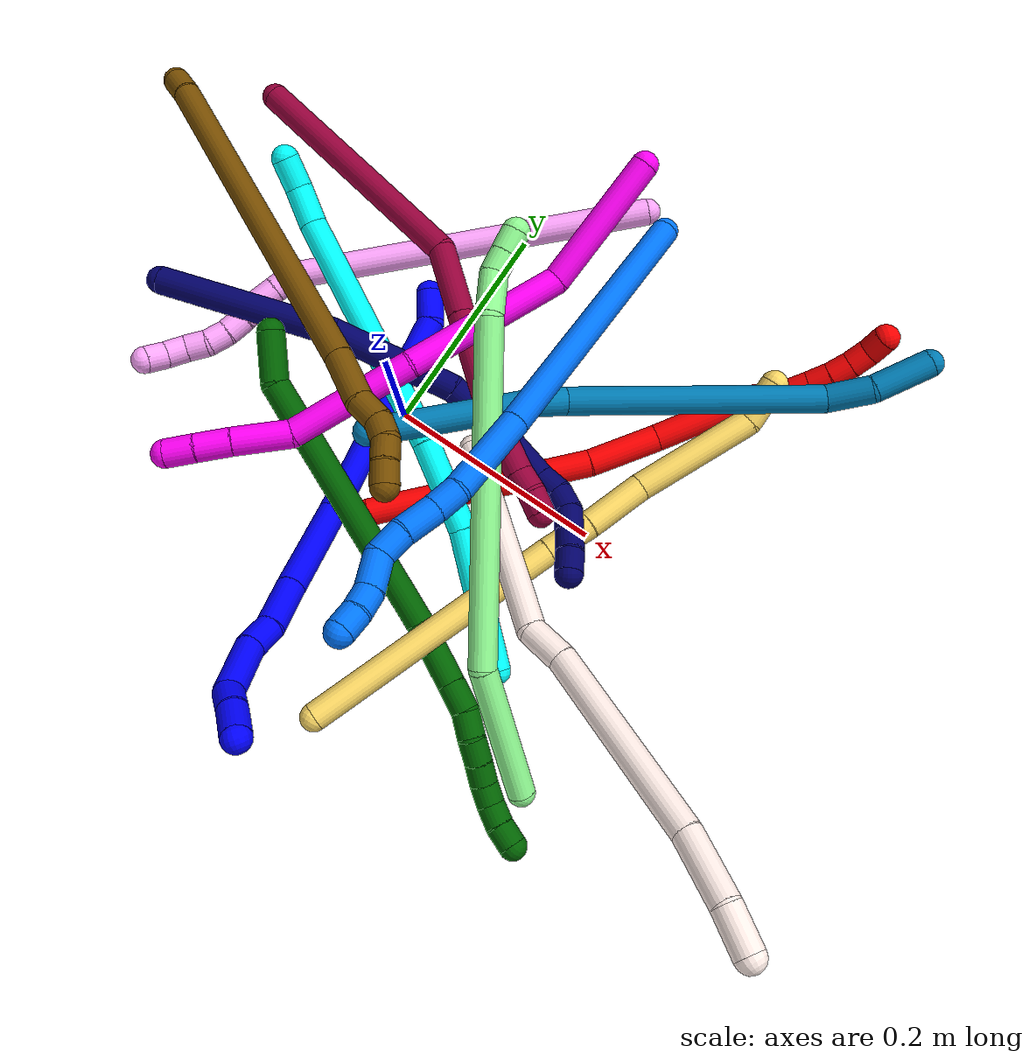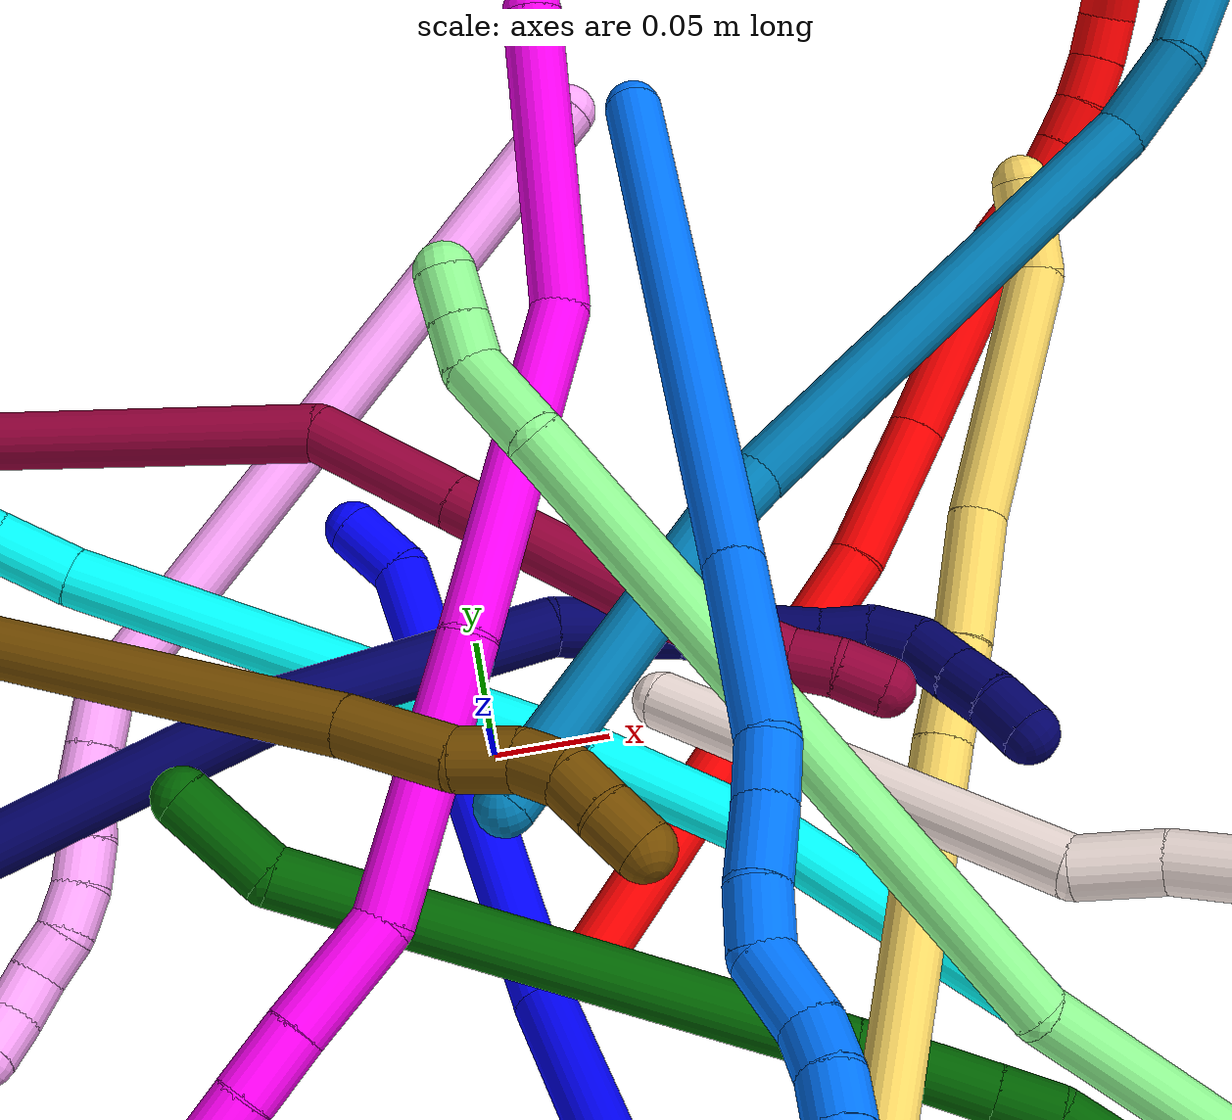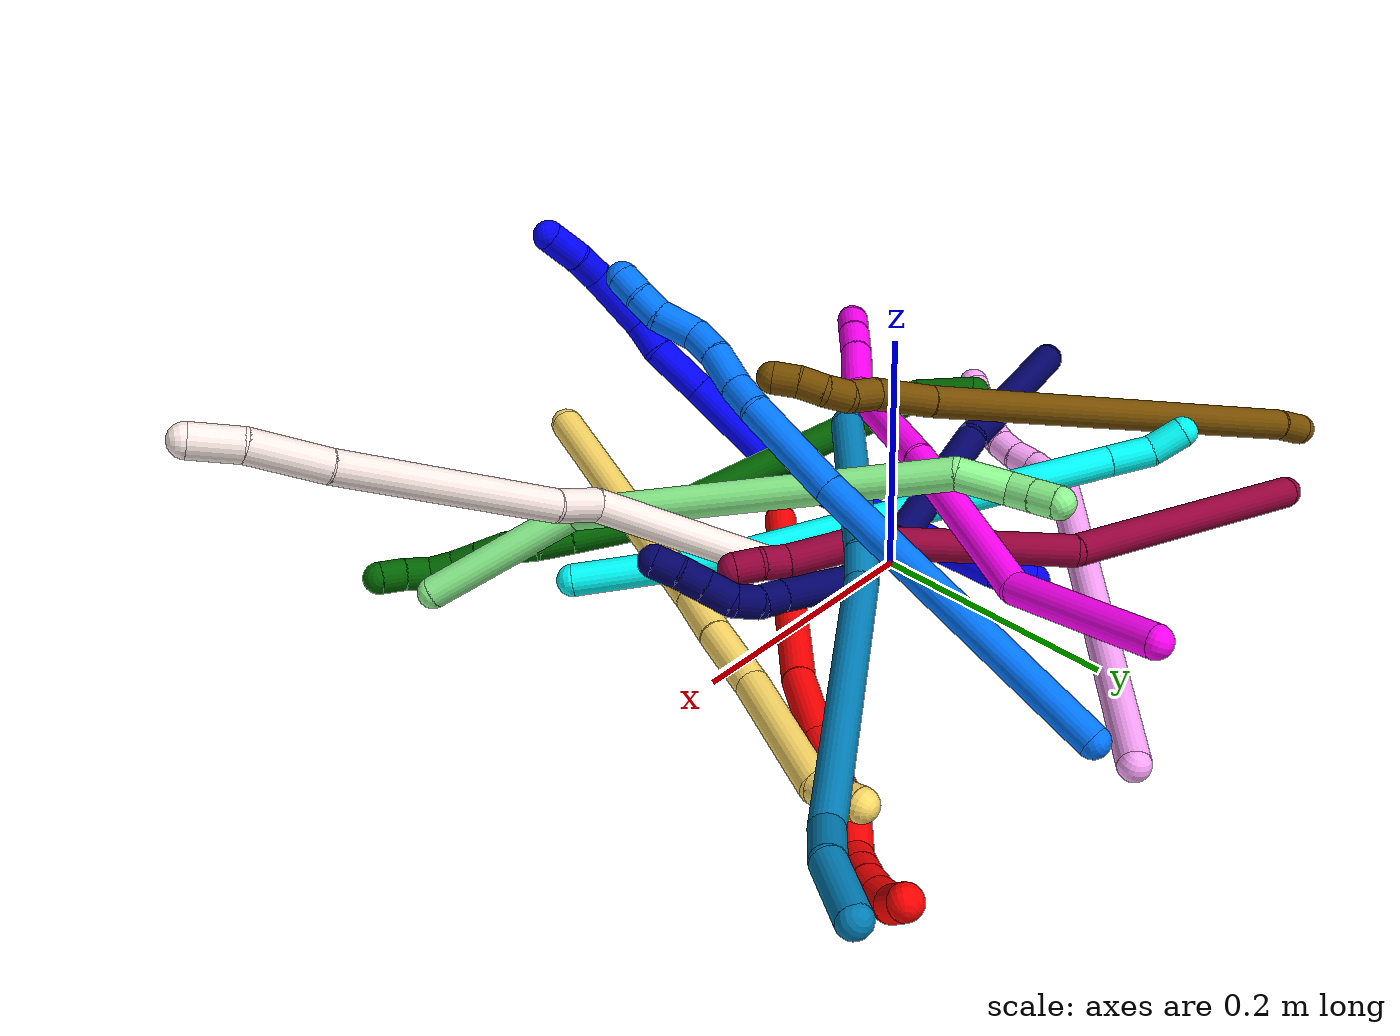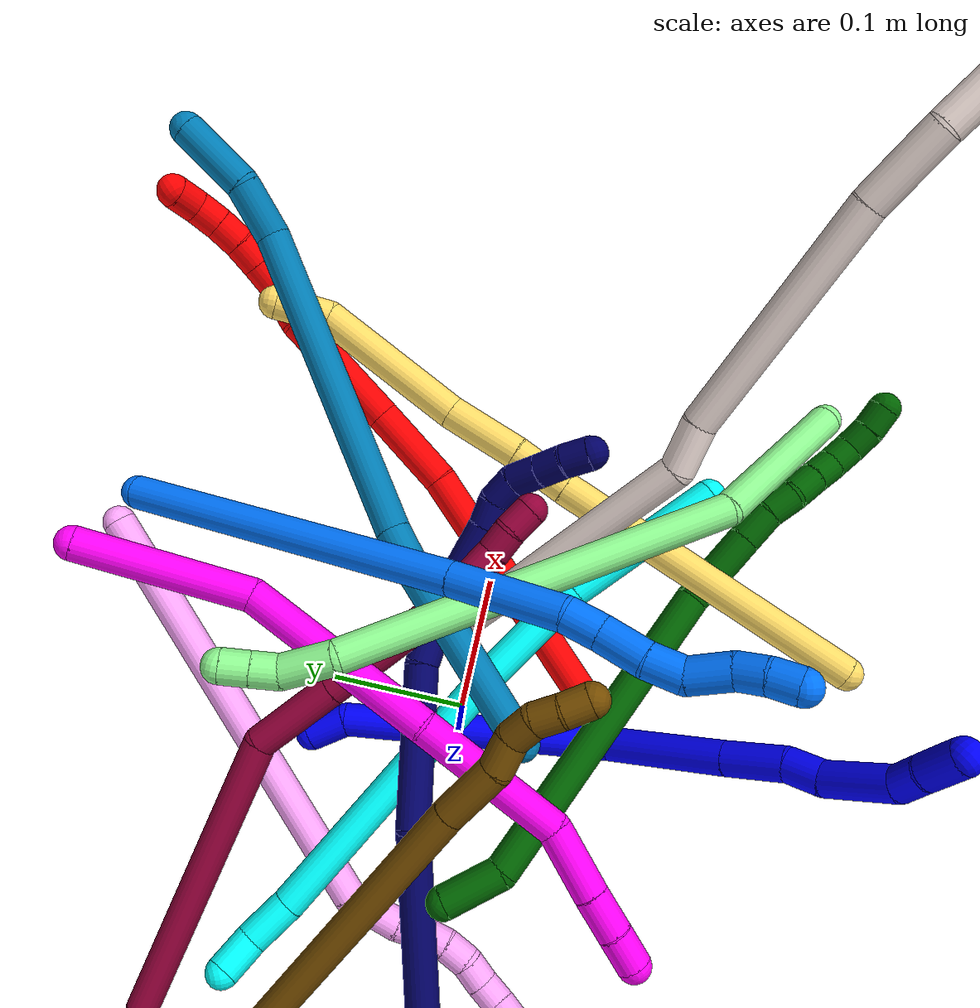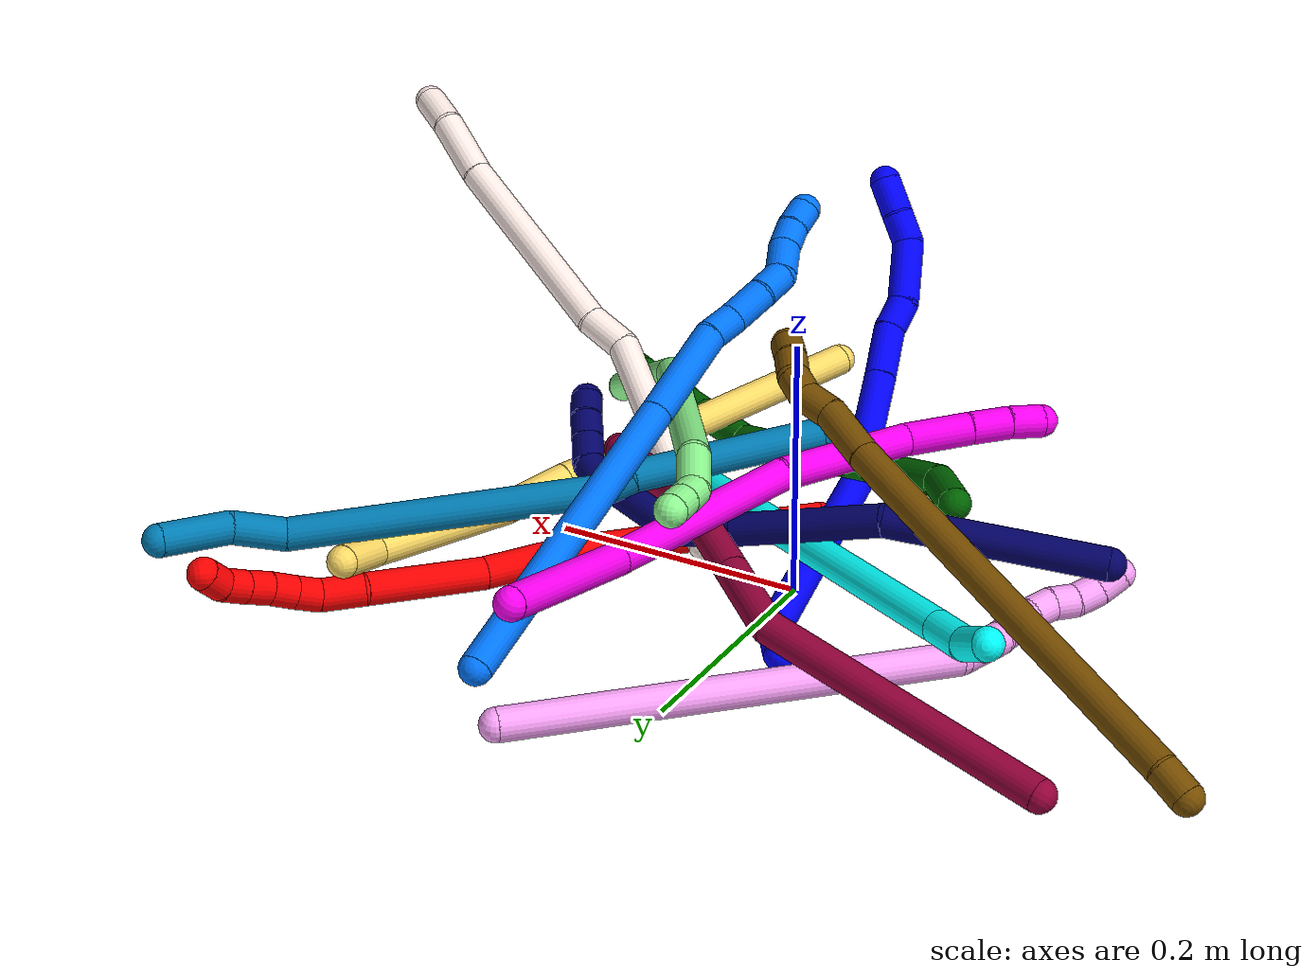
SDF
<sdf version="1.7">
 <world name="default">
  <plugin name="TubeGeneratorPlugin" filename="libtube_generator_plugin.so"/>
  <model name="photoneo_s_sensor">
   <static>1</static>
   <pose>0 0 2 1.57079 1.57079 3.14159</pose>
   <link name="link">
    <inertial><mass>0.1</mass></inertial>
    <sensor name="sensor" type="depth">
     <update_rate>30</update_rate>
     <camera>
      <horizontal_fov>1.22</horizontal_fov>
      <image><width>1920</width><height>1200</height><format>B8G8R8</format></image>
      <clip><near>0.1</near><far>4</far></clip>
      <depth_camera><output>points</output></depth_camera>
     </camera>
     <plugin name="camera_plugin" filename="libgazebo_ros_depth_camera.so">
      <baseline>0.2</baseline>
      <alwaysOn>1</alwaysOn>
      <updateRate>0.0</updateRate>
      <cameraName>camera_ir</cameraName>
      <imageTopicName>/camera/color/image_raw</imageTopicName>
      <cameraInfoTopicName>/camera/color/camera_info</cameraInfoTopicName>
      <depthImageTopicName>/camera/depth/image_raw</depthImageTopicName>
      <depthImageCameraInfoTopicName>/camera/depth/camera_info</depthImageCameraInfoTopicName>
      <pointCloudTopicName>/camera/depth/points</pointCloudTopicName>
      <frameName>fr_optical</frameName>
      <pointCloudCutoff>0.1</pointCloudCutoff>
      <pointCloudCutoffMax>2.0</pointCloudCutoffMax>
      <distortionK1>0</distortionK1>
      <distortionK2>0</distortionK2>
      <distortionK3>0</distortionK3>
      <distortionT1>0</distortionT1>
      <distortionT2>0</distortionT2>
      <CxPrime>0</CxPrime>
      <Cx>0</Cx>
      <Cy>0</Cy>
      <focalLength>0</focalLength>
      <hackBaseline>0</hackBaseline>
     </plugin>
    </sensor>
   </link>
  </model>
  <gravity>0 0 -9.8</gravity>
  <magnetic_field>6e-06 2.3e-05 -4.2e-05</magnetic_field>
  <atmosphere type="adiabatic"/>
  <physics name="default_physics" default="0" type="ode">
   <max_step_size>0.003</max_step_size>
   <real_time_factor>1</real_time_factor>
   <real_time_update_rate>1000</real_time_update_rate>
   <max_contacts>10000</max_contacts>
   <ode>
    <solver>
     <type>quick</type>
     <iters>100</iters>
     <sor>1.3</sor>
     <use_dynamic_moi_rescaling>0</use_dynamic_moi_rescaling>
    </solver>
    <constraints>
     <contact_max_correcting_vel>0</contact_max_correcting_vel>
     <contact_surface_layer>0.001</contact_surface_layer>
     <cfm>0</cfm>
     <erp>0.2</erp>
    </constraints>
   </ode>
  </physics>
  <scene><ambient>0.4 0.4 0.4 1</ambient><background>0.7 0.7 0.7 1</background><shadows>0</shadows></scene>
  <audio><device>default</device></audio>
  <spherical_coordinates>
   <surface_model>EARTH_WGS84</surface_model>
   <latitude_deg>0</latitude_deg>
   <longitude_deg>0</longitude_deg>
   <elevation>0</elevation>
   <heading_deg>0</heading_deg>
  </spherical_coordinates>
  <model name="bin">
   <static>1</static>
   <link name="bottom">
    <collision name="collision-bottom">
     <pose>0 0 -0.01 0 -0 0</pose>
     <geometry><box><size>0.8 0.6 0.02</size></box></geometry>
     <surface>
      <friction><ode><mu>100</mu><mu2>100</mu2></ode></friction>
      <contact><collide_bitmask>65535</collide_bitmask></contact>
     </surface>
    </collision>
   </link>
   <link name="west_wall">
    <collision name="collision-west_wall">
     <pose>-0.41 0 0.1 0 -0 0</pose>
     <geometry><box><size>0.02 0.6 0.2</size></box></geometry>
     <surface>
      <friction><ode><mu>100</mu><mu2>100</mu2></ode></friction>
      <contact><collide_bitmask>65535</collide_bitmask></contact>
     </surface>
    </collision>
   </link>
   <link name="east_wall">
    <collision name="collision-east_wall">
     <pose>0.41 0 0.1 0 -0 0</pose>
     <geometry><box><size>0.02 0.6 0.2</size></box></geometry>
     <surface>
      <friction><ode><mu>100</mu><mu2>100</mu2></ode></friction>
      <contact><collide_bitmask>65535</collide_bitmask></contact>
     </surface>
    </collision>
   </link>
   <link name="south_wall">
    <collision name="collision-south_wall">
     <pose>0 -0.31 0.1 0 -0 0</pose>
     <geometry><box><size>0.8 0.02 0.2</size></box></geometry>
     <surface>
      <friction><ode><mu>100</mu><mu2>100</mu2></ode></friction>
      <contact><collide_bitmask>65535</collide_bitmask></contact>
     </surface>
    </collision>
   </link>
   <link name="north_wall">
    <collision name="collision-north_wall">
     <pose>0 0.31 0.1 0 -0 0</pose>
     <geometry><box><size>0.8 0.02 0.2</size></box></geometry>
     <surface>
      <friction><ode><mu>100</mu><mu2>100</mu2></ode></friction>
      <contact><collide_bitmask>65535</collide_bitmask></contact>
     </surface>
    </collision>
   </link>
  </model>
  <model name="1">
   <static>0</static>
   <link name="1">
    <collision name="collision-cylinder-e_1_1_4">
     <pose>-0.00103 -0.005915 0.013646 0.409021 -0.069138 -0.014345</pose>
     <geometry><cylinder><radius>0.0125</radius><length>0.029816</length></cylinder></geometry>
     <surface>
      <friction><ode><mu>1.16</mu><mu2>1.16</mu2><slip1>0</slip1><slip2>0</slip2></ode></friction>
      <contact><ode><kp>1e+06</kp><kd>1</kd><max_vel>0</max_vel><min_depth>0.001</min_depth></ode></contact>
     </surface>
    </collision>
    <visual name="visual-cylinder-e_1_1_4">
     <pose>-0.00103 -0.005915 0.013646 0.409021 -0.069138 -0.014345</pose>
     <geometry><cylinder><radius>0.0125</radius><length>0.029816</length></cylinder></geometry>
     <material><ambient>0 0 1 1</ambient></material>
    </visual>
    <collision name="collision-cylinder-e_2_4_5">
     <pose>0.022407 -0.079477 0.096136 0.776625 0.248259 0.101995</pose>
     <geometry><cylinder><radius>0.0125</radius><length>0.199143</length></cylinder></geometry>
     <surface>
      <friction><ode><mu>1.16</mu><mu2>1.16</mu2><slip1>0</slip1><slip2>0</slip2></ode></friction>
      <contact><ode><kp>1e+06</kp><kd>1</kd><max_vel>0</max_vel><min_depth>0.001</min_depth></ode></contact>
     </surface>
    </collision>
    <visual name="visual-cylinder-e_2_4_5">
     <pose>0.022407 -0.079477 0.096136 0.776625 0.248259 0.101995</pose>
     <geometry><cylinder><radius>0.0125</radius><length>0.199143</length></cylinder></geometry>
     <material><ambient>0 0 1 1</ambient></material>
    </visual>
    <collision name="collision-cylinder-e_3_5_6">
     <pose>0.036541 -0.185455 0.190308 0.986899 -0.221207 -0.119317</pose>
     <geometry><cylinder><radius>0.0125</radius><length>0.094177</length></cylinder></geometry>
     <surface>
      <friction><ode><mu>1.16</mu><mu2>1.16</mu2><slip1>0</slip1><slip2>0</slip2></ode></friction>
      <contact><ode><kp>1e+06</kp><kd>1</kd><max_vel>0</max_vel><min_depth>0.001</min_depth></ode></contact>
     </surface>
    </collision>
    <visual name="visual-cylinder-e_3_5_6">
     <pose>0.036541 -0.185455 0.190308 0.986899 -0.221207 -0.119317</pose>
     <geometry><cylinder><radius>0.0125</radius><length>0.094177</length></cylinder></geometry>
     <material><ambient>0 0 1 1</ambient></material>
    </visual>
    <collision name="collision-cylinder-e_4_6_7">
     <pose>0.021186 -0.24153 0.228034 0.960908 -0.228023 -0.119219</pose>
     <geometry><cylinder><radius>0.0125</radius><length>0.044447</length></cylinder></geometry>
     <surface>
      <friction><ode><mu>1.16</mu><mu2>1.16</mu2><slip1>0</slip1><slip2>0</slip2></ode></friction>
      <contact><ode><kp>1e+06</kp><kd>1</kd><max_vel>0</max_vel><min_depth>0.001</min_depth></ode></contact>
     </surface>
    </collision>
    <visual name="visual-cylinder-e_4_6_7">
     <pose>0.021186 -0.24153 0.228034 0.960908 -0.228023 -0.119219</pose>
     <geometry><cylinder><radius>0.0125</radius><length>0.044447</length></cylinder></geometry>
     <material><ambient>0 0 1 1</ambient></material>
    </visual>
    <collision name="collision-cylinder-e_5_7_8">
     <pose>0.014735 -0.27144 0.24501 1.21093 -0.109398 -0.075763</pose>
     <geometry><cylinder><radius>0.0125</radius><length>0.026151</length></cylinder></geometry>
     <surface>
      <friction><ode><mu>1.16</mu><mu2>1.16</mu2><slip1>0</slip1><slip2>0</slip2></ode></friction>
      <contact><ode><kp>1e+06</kp><kd>1</kd><max_vel>0</max_vel><min_depth>0.001</min_depth></ode></contact>
     </surface>
    </collision>
    <visual name="visual-cylinder-e_5_7_8">
     <pose>0.014735 -0.27144 0.24501 1.21093 -0.109398 -0.075763</pose>
     <geometry><cylinder><radius>0.0125</radius><length>0.026151</length></cylinder></geometry>
     <material><ambient>0 0 1 1</ambient></material>
    </visual>
    <collision name="collision-cylinder-e_6_8_9">
     <pose>0.002943 -0.303717 0.262427 1.0026 -0.409768 -0.226769</pose>
     <geometry><cylinder><radius>0.0125</radius><length>0.052029</length></cylinder></geometry>
     <surface>
      <friction><ode><mu>1.16</mu><mu2>1.16</mu2><slip1>0</slip1><slip2>0</slip2></ode></friction>
      <contact><ode><kp>1e+06</kp><kd>1</kd><max_vel>0</max_vel><min_depth>0.001</min_depth></ode></contact>
     </surface>
    </collision>
    <visual name="visual-cylinder-e_6_8_9">
     <pose>0.002943 -0.303717 0.262427 1.0026 -0.409768 -0.226769</pose>
     <geometry><cylinder><radius>0.0125</radius><length>0.052029</length></cylinder></geometry>
     <material><ambient>0 0 1 1</ambient></material>
    </visual>
    <collision name="collision-cylinder-e_7_9_10">
     <pose>-0.016745 -0.329215 0.281194 0.737707 -0.861136 -0.351425</pose>
     <geometry><cylinder><radius>0.0125</radius><length>0.024582</length></cylinder></geometry>
     <surface>
      <friction><ode><mu>1.16</mu><mu2>1.16</mu2><slip1>0</slip1><slip2>0</slip2></ode></friction>
      <contact><ode><kp>1e+06</kp><kd>1</kd><max_vel>0</max_vel><min_depth>0.001</min_depth></ode></contact>
     </surface>
    </collision>
    <visual name="visual-cylinder-e_7_9_10">
     <pose>-0.016745 -0.329215 0.281194 0.737707 -0.861136 -0.351425</pose>
     <geometry><cylinder><radius>0.0125</radius><length>0.024582</length></cylinder></geometry>
     <material><ambient>0 0 1 1</ambient></material>
    </visual>
    <collision name="collision-cylinder-e_8_10_2">
     <pose>-0.035857 -0.341398 0.295944 0.656313 -0.720999 -0.255298</pose>
     <geometry><cylinder><radius>0.0125</radius><length>0.029654</length></cylinder></geometry>
     <surface>
      <friction><ode><mu>1.16</mu><mu2>1.16</mu2><slip1>0</slip1><slip2>0</slip2></ode></friction>
      <contact><ode><kp>1e+06</kp><kd>1</kd><max_vel>0</max_vel><min_depth>0.001</min_depth></ode></contact>
     </surface>
    </collision>
    <visual name="visual-cylinder-e_8_10_2">
     <pose>-0.035857 -0.341398 0.295944 0.656313 -0.720999 -0.255298</pose>
     <geometry><cylinder><radius>0.0125</radius><length>0.029654</length></cylinder></geometry>
     <material><ambient>0 0 1 1</ambient></material>
    </visual>
    <collision name="collision-sphere-2">
     <pose>-0.045645 -0.348194 0.304767 0 -0 0</pose>
     <geometry><sphere><radius>0.0125</radius></sphere></geometry>
     <surface>
      <friction><ode><mu>1.16</mu><mu2>1.16</mu2><slip1>0</slip1><slip2>0</slip2></ode></friction>
      <contact><ode><kp>1e+06</kp><kd>1</kd><max_vel>0</max_vel><min_depth>0.001</min_depth></ode></contact>
     </surface>
    </collision>
    <visual name="visual-sphere-2">
     <pose>-0.045645 -0.348194 0.304767 0 -0 0</pose>
     <geometry><sphere><radius>0.0125</radius></sphere></geometry>
     <material><ambient>0 0 1 1</ambient></material>
    </visual>
    <collision name="collision-sphere-10">
     <pose>-0.026069 -0.334602 0.28712 0 -0 0</pose>
     <geometry><sphere><radius>0.0125</radius></sphere></geometry>
     <surface>
      <friction><ode><mu>1.16</mu><mu2>1.16</mu2><slip1>0</slip1><slip2>0</slip2></ode></friction>
      <contact><ode><kp>1e+06</kp><kd>1</kd><max_vel>0</max_vel><min_depth>0.001</min_depth></ode></contact>
     </surface>
    </collision>
    <visual name="visual-sphere-10">
     <pose>-0.026069 -0.334602 0.28712 0 -0 0</pose>
     <geometry><sphere><radius>0.0125</radius></sphere></geometry>
     <material><ambient>0 0 1 1</ambient></material>
    </visual>
    <collision name="collision-sphere-9">
     <pose>-0.007421 -0.323828 0.275267 0 -0 0</pose>
     <geometry><sphere><radius>0.0125</radius></sphere></geometry>
     <surface>
      <friction><ode><mu>1.16</mu><mu2>1.16</mu2><slip1>0</slip1><slip2>0</slip2></ode></friction>
      <contact><ode><kp>1e+06</kp><kd>1</kd><max_vel>0</max_vel><min_depth>0.001</min_depth></ode></contact>
     </surface>
    </collision>
    <visual name="visual-sphere-9">
     <pose>-0.007421 -0.323828 0.275267 0 -0 0</pose>
     <geometry><sphere><radius>0.0125</radius></sphere></geometry>
     <material><ambient>0 0 1 1</ambient></material>
    </visual>
    <collision name="collision-sphere-4">
     <pose>-0.00206 -0.01183 0.027291 0 -0 0</pose>
     <geometry><sphere><radius>0.0125</radius></sphere></geometry>
     <surface>
      <friction><ode><mu>1.16</mu><mu2>1.16</mu2><slip1>0</slip1><slip2>0</slip2></ode></friction>
      <contact><ode><kp>1e+06</kp><kd>1</kd><max_vel>0</max_vel><min_depth>0.001</min_depth></ode></contact>
     </surface>
    </collision>
    <visual name="visual-sphere-4">
     <pose>-0.00206 -0.01183 0.027291 0 -0 0</pose>
     <geometry><sphere><radius>0.0125</radius></sphere></geometry>
     <material><ambient>0 0 1 1</ambient></material>
    </visual>
    <collision name="collision-sphere-1">
     <geometry><sphere><radius>0.0125</radius></sphere></geometry>
     <surface>
      <friction><ode><mu>1.16</mu><mu2>1.16</mu2><slip1>0</slip1><slip2>0</slip2></ode></friction>
      <contact><ode><kp>1e+06</kp><kd>1</kd><max_vel>0</max_vel><min_depth>0.001</min_depth></ode></contact>
     </surface>
    </collision>
    <visual name="visual-sphere-1">
     <geometry><sphere><radius>0.0125</radius></sphere></geometry>
     <material><ambient>0 0 1 1</ambient></material>
    </visual>
    <collision name="collision-sphere-8">
     <pose>0.013307 -0.283605 0.249588 0 -0 0</pose>
     <geometry><sphere><radius>0.0125</radius></sphere></geometry>
     <surface>
      <friction><ode><mu>1.16</mu><mu2>1.16</mu2><slip1>0</slip1><slip2>0</slip2></ode></friction>
      <contact><ode><kp>1e+06</kp><kd>1</kd><max_vel>0</max_vel><min_depth>0.001</min_depth></ode></contact>
     </surface>
    </collision>
    <visual name="visual-sphere-8">
     <pose>0.013307 -0.283605 0.249588 0 -0 0</pose>
     <geometry><sphere><radius>0.0125</radius></sphere></geometry>
     <material><ambient>0 0 1 1</ambient></material>
    </visual>
    <collision name="collision-sphere-5">
     <pose>0.046873 -0.147125 0.164981 0 -0 0</pose>
     <geometry><sphere><radius>0.0125</radius></sphere></geometry>
     <surface>
      <friction><ode><mu>1.16</mu><mu2>1.16</mu2><slip1>0</slip1><slip2>0</slip2></ode></friction>
      <contact><ode><kp>1e+06</kp><kd>1</kd><max_vel>0</max_vel><min_depth>0.001</min_depth></ode></contact>
     </surface>
    </collision>
    <visual name="visual-sphere-5">
     <pose>0.046873 -0.147125 0.164981 0 -0 0</pose>
     <geometry><sphere><radius>0.0125</radius></sphere></geometry>
     <material><ambient>0 0 1 1</ambient></material>
    </visual>
    <collision name="collision-sphere-6">
     <pose>0.02621 -0.223785 0.215634 0 -0 0</pose>
     <geometry><sphere><radius>0.0125</radius></sphere></geometry>
     <surface>
      <friction><ode><mu>1.16</mu><mu2>1.16</mu2><slip1>0</slip1><slip2>0</slip2></ode></friction>
      <contact><ode><kp>1e+06</kp><kd>1</kd><max_vel>0</max_vel><min_depth>0.001</min_depth></ode></contact>
     </surface>
    </collision>
    <visual name="visual-sphere-6">
     <pose>0.02621 -0.223785 0.215634 0 -0 0</pose>
     <geometry><sphere><radius>0.0125</radius></sphere></geometry>
     <material><ambient>0 0 1 1</ambient></material>
    </visual>
    <collision name="collision-sphere-7">
     <pose>0.016162 -0.259275 0.240433 0 -0 0</pose>
     <geometry><sphere><radius>0.0125</radius></sphere></geometry>
     <surface>
      <friction><ode><mu>1.16</mu><mu2>1.16</mu2><slip1>0</slip1><slip2>0</slip2></ode></friction>
      <contact><ode><kp>1e+06</kp><kd>1</kd><max_vel>0</max_vel><min_depth>0.001</min_depth></ode></contact>
     </surface>
    </collision>
    <visual name="visual-sphere-7">
     <pose>0.016162 -0.259275 0.240433 0 -0 0</pose>
     <geometry><sphere><radius>0.0125</radius></sphere></geometry>
     <material><ambient>0 0 1 1</ambient></material>
    </visual>
    <inertial>
     <pose>0.015756 -0.170644 0.166719 0 -0 0</pose>
     <mass>0.5</mass>
     <inertia>
      <ixx>0.000792</ixx>
      <ixy>0</ixy>
      <ixz>0</ixz>
      <iyy>0.000573</iyy>
      <iyz>0</iyz>
      <izz>0.000424</izz>
     </inertia>
    </inertial>
   </link>
   <pose>-0.044529 0.106787 0.011292 -1.79822 0.906932 -2.3969</pose>
  </model>
  <model name="2">
   <static>0</static>
   <link name="2">
    <collision name="collision-cylinder-e_1_1_4">
     <pose>0.000431 0.000255 0.102914 -0.002482 0.004192 -5e-06</pose>
     <geometry><cylinder><radius>0.0125</radius><length>0.205831</length></cylinder></geometry>
     <surface>
      <friction><ode><mu>1.16</mu><mu2>1.16</mu2><slip1>0</slip1><slip2>0</slip2></ode></friction>
      <contact><ode><kp>1e+06</kp><kd>1</kd><max_vel>0</max_vel><min_depth>0.001</min_depth></ode></contact>
     </surface>
    </collision>
    <visual name="visual-cylinder-e_1_1_4">
     <pose>0.000431 0.000255 0.102914 -0.002482 0.004192 -5e-06</pose>
     <geometry><cylinder><radius>0.0125</radius><length>0.205831</length></cylinder></geometry>
     <material><ambient>1 0 0 1</ambient></material>
    </visual>
    <collision name="collision-cylinder-e_2_4_5">
     <pose>0.005104 0.003269 0.238259 -0.084839 0.129572 -0.005507</pose>
     <geometry><cylinder><radius>0.0125</radius><length>0.065646</length></cylinder></geometry>
     <surface>
      <friction><ode><mu>1.16</mu><mu2>1.16</mu2><slip1>0</slip1><slip2>0</slip2></ode></friction>
      <contact><ode><kp>1e+06</kp><kd>1</kd><max_vel>0</max_vel><min_depth>0.001</min_depth></ode></contact>
     </surface>
    </collision>
    <visual name="visual-cylinder-e_2_4_5">
     <pose>0.005104 0.003269 0.238259 -0.084839 0.129572 -0.005507</pose>
     <geometry><cylinder><radius>0.0125</radius><length>0.065646</length></cylinder></geometry>
     <material><ambient>1 0 0 1</ambient></material>
    </visual>
    <collision name="collision-cylinder-e_3_5_6">
     <pose>0.011664 0.014586 0.317357 -0.181391 0.048834 -0.004442</pose>
     <geometry><cylinder><radius>0.0125</radius><length>0.095005</length></cylinder></geometry>
     <surface>
      <friction><ode><mu>1.16</mu><mu2>1.16</mu2><slip1>0</slip1><slip2>0</slip2></ode></friction>
      <contact><ode><kp>1e+06</kp><kd>1</kd><max_vel>0</max_vel><min_depth>0.001</min_depth></ode></contact>
     </surface>
    </collision>
    <visual name="visual-cylinder-e_3_5_6">
     <pose>0.011664 0.014586 0.317357 -0.181391 0.048834 -0.004442</pose>
     <geometry><cylinder><radius>0.0125</radius><length>0.095005</length></cylinder></geometry>
     <material><ambient>1 0 0 1</ambient></material>
    </visual>
    <collision name="collision-cylinder-e_4_6_7">
     <pose>0.013732 0.022293 0.380685 0.051128 -0.015042 -0.000385</pose>
     <geometry><cylinder><radius>0.0125</radius><length>0.033368</length></cylinder></geometry>
     <surface>
      <friction><ode><mu>1.16</mu><mu2>1.16</mu2><slip1>0</slip1><slip2>0</slip2></ode></friction>
      <contact><ode><kp>1e+06</kp><kd>1</kd><max_vel>0</max_vel><min_depth>0.001</min_depth></ode></contact>
     </surface>
    </collision>
    <visual name="visual-cylinder-e_4_6_7">
     <pose>0.013732 0.022293 0.380685 0.051128 -0.015042 -0.000385</pose>
     <geometry><cylinder><radius>0.0125</radius><length>0.033368</length></cylinder></geometry>
     <material><ambient>1 0 0 1</ambient></material>
    </visual>
    <collision name="collision-cylinder-e_5_7_8">
     <pose>0.011833 0.024399 0.406795 -0.303457 -0.16491 0.025271</pose>
     <geometry><cylinder><radius>0.0125</radius><length>0.020077</length></cylinder></geometry>
     <surface>
      <friction><ode><mu>1.16</mu><mu2>1.16</mu2><slip1>0</slip1><slip2>0</slip2></ode></friction>
      <contact><ode><kp>1e+06</kp><kd>1</kd><max_vel>0</max_vel><min_depth>0.001</min_depth></ode></contact>
     </surface>
    </collision>
    <visual name="visual-cylinder-e_5_7_8">
     <pose>0.011833 0.024399 0.406795 -0.303457 -0.16491 0.025271</pose>
     <geometry><cylinder><radius>0.0125</radius><length>0.020077</length></cylinder></geometry>
     <material><ambient>1 0 0 1</ambient></material>
    </visual>
    <collision name="collision-cylinder-e_6_8_9">
     <pose>0.008439 0.030816 0.425484 -0.358084 -0.175131 0.031774</pose>
     <geometry><cylinder><radius>0.0125</radius><length>0.020037</length></cylinder></geometry>
     <surface>
      <friction><ode><mu>1.16</mu><mu2>1.16</mu2><slip1>0</slip1><slip2>0</slip2></ode></friction>
      <contact><ode><kp>1e+06</kp><kd>1</kd><max_vel>0</max_vel><min_depth>0.001</min_depth></ode></contact>
     </surface>
    </collision>
    <visual name="visual-cylinder-e_6_8_9">
     <pose>0.008439 0.030816 0.425484 -0.358084 -0.175131 0.031774</pose>
     <geometry><cylinder><radius>0.0125</radius><length>0.020037</length></cylinder></geometry>
     <material><ambient>1 0 0 1</ambient></material>
    </visual>
    <collision name="collision-cylinder-e_7_9_10">
     <pose>0.006103 0.038239 0.443903 -0.40782 -0.058995 0.012203</pose>
     <geometry><cylinder><radius>0.0125</radius><length>0.020033</length></cylinder></geometry>
     <surface>
      <friction><ode><mu>1.16</mu><mu2>1.16</mu2><slip1>0</slip1><slip2>0</slip2></ode></friction>
      <contact><ode><kp>1e+06</kp><kd>1</kd><max_vel>0</max_vel><min_depth>0.001</min_depth></ode></contact>
     </surface>
    </collision>
    <visual name="visual-cylinder-e_7_9_10">
     <pose>0.006103 0.038239 0.443903 -0.40782 -0.058995 0.012203</pose>
     <geometry><cylinder><radius>0.0125</radius><length>0.020033</length></cylinder></geometry>
     <material><ambient>1 0 0 1</ambient></material>
    </visual>
    <collision name="collision-cylinder-e_8_10_11">
     <pose>0.004992 0.0473 0.461672 -0.535406 -0.052028 0.014274</pose>
     <geometry><cylinder><radius>0.0125</radius><length>0.020001</length></cylinder></geometry>
     <surface>
      <friction><ode><mu>1.16</mu><mu2>1.16</mu2><slip1>0</slip1><slip2>0</slip2></ode></friction>
      <contact><ode><kp>1e+06</kp><kd>1</kd><max_vel>0</max_vel><min_depth>0.001</min_depth></ode></contact>
     </surface>
    </collision>
    <visual name="visual-cylinder-e_8_10_11">
     <pose>0.004992 0.0473 0.461672 -0.535406 -0.052028 0.014274</pose>
     <geometry><cylinder><radius>0.0125</radius><length>0.020001</length></cylinder></geometry>
     <material><ambient>1 0 0 1</ambient></material>
    </visual>
    <collision name="collision-cylinder-e_9_11_2">
     <pose>0.001824 0.059571 0.476704 -0.839148 -0.268002 0.120122</pose>
     <geometry><cylinder><radius>0.0125</radius><length>0.020002</length></cylinder></geometry>
     <surface>
      <friction><ode><mu>1.16</mu><mu2>1.16</mu2><slip1>0</slip1><slip2>0</slip2></ode></friction>
      <contact><ode><kp>1e+06</kp><kd>1</kd><max_vel>0</max_vel><min_depth>0.001</min_depth></ode></contact>
     </surface>
    </collision>
    <visual name="visual-cylinder-e_9_11_2">
     <pose>0.001824 0.059571 0.476704 -0.839148 -0.268002 0.120122</pose>
     <geometry><cylinder><radius>0.0125</radius><length>0.020002</length></cylinder></geometry>
     <material><ambient>1 0 0 1</ambient></material>
    </visual>
    <collision name="collision-sphere-2">
     <pose>-0.000825 0.066747 0.483147 0 -0 0</pose>
     <geometry><sphere><radius>0.0125</radius></sphere></geometry>
     <surface>
      <friction><ode><mu>1.16</mu><mu2>1.16</mu2><slip1>0</slip1><slip2>0</slip2></ode></friction>
      <contact><ode><kp>1e+06</kp><kd>1</kd><max_vel>0</max_vel><min_depth>0.001</min_depth></ode></contact>
     </surface>
    </collision>
    <visual name="visual-sphere-2">
     <pose>-0.000825 0.066747 0.483147 0 -0 0</pose>
     <geometry><sphere><radius>0.0125</radius></sphere></geometry>
     <material><ambient>1 0 0 1</ambient></material>
    </visual>
    <collision name="collision-sphere-11">
     <pose>0.004472 0.052395 0.470261 0 -0 0</pose>
     <geometry><sphere><radius>0.0125</radius></sphere></geometry>
     <surface>
      <friction><ode><mu>1.16</mu><mu2>1.16</mu2><slip1>0</slip1><slip2>0</slip2></ode></friction>
      <contact><ode><kp>1e+06</kp><kd>1</kd><max_vel>0</max_vel><min_depth>0.001</min_depth></ode></contact>
     </surface>
    </collision>
    <visual name="visual-sphere-11">
     <pose>0.004472 0.052395 0.470261 0 -0 0</pose>
     <geometry><sphere><radius>0.0125</radius></sphere></geometry>
     <material><ambient>1 0 0 1</ambient></material>
    </visual>
    <collision name="collision-sphere-10">
     <pose>0.005512 0.042205 0.453082 0 -0 0</pose>
     <geometry><sphere><radius>0.0125</radius></sphere></geometry>
     <surface>
      <friction><ode><mu>1.16</mu><mu2>1.16</mu2><slip1>0</slip1><slip2>0</slip2></ode></friction>
      <contact><ode><kp>1e+06</kp><kd>1</kd><max_vel>0</max_vel><min_depth>0.001</min_depth></ode></contact>
     </surface>
    </collision>
    <visual name="visual-sphere-10">
     <pose>0.005512 0.042205 0.453082 0 -0 0</pose>
     <geometry><sphere><radius>0.0125</radius></sphere></geometry>
     <material><ambient>1 0 0 1</ambient></material>
    </visual>
    <collision name="collision-sphere-9">
     <pose>0.006694 0.034273 0.434724 0 -0 0</pose>
     <geometry><sphere><radius>0.0125</radius></sphere></geometry>
     <surface>
      <friction><ode><mu>1.16</mu><mu2>1.16</mu2><slip1>0</slip1><slip2>0</slip2></ode></friction>
      <contact><ode><kp>1e+06</kp><kd>1</kd><max_vel>0</max_vel><min_depth>0.001</min_depth></ode></contact>
     </surface>
    </collision>
    <visual name="visual-sphere-9">
     <pose>0.006694 0.034273 0.434724 0 -0 0</pose>
     <geometry><sphere><radius>0.0125</radius></sphere></geometry>
     <material><ambient>1 0 0 1</ambient></material>
    </visual>
    <collision name="collision-sphere-4">
     <pose>0.000863 0.000511 0.205829 0 -0 0</pose>
     <geometry><sphere><radius>0.0125</radius></sphere></geometry>
     <surface>
      <friction><ode><mu>1.16</mu><mu2>1.16</mu2><slip1>0</slip1><slip2>0</slip2></ode></friction>
      <contact><ode><kp>1e+06</kp><kd>1</kd><max_vel>0</max_vel><min_depth>0.001</min_depth></ode></contact>
     </surface>
    </collision>
    <visual name="visual-sphere-4">
     <pose>0.000863 0.000511 0.205829 0 -0 0</pose>
     <geometry><sphere><radius>0.0125</radius></sphere></geometry>
     <material><ambient>1 0 0 1</ambient></material>
    </visual>
    <collision name="collision-sphere-1">
     <geometry><sphere><radius>0.0125</radius></sphere></geometry>
     <surface>
      <friction><ode><mu>1.16</mu><mu2>1.16</mu2><slip1>0</slip1><slip2>0</slip2></ode></friction>
      <contact><ode><kp>1e+06</kp><kd>1</kd><max_vel>0</max_vel><min_depth>0.001</min_depth></ode></contact>
     </surface>
    </collision>
    <visual name="visual-sphere-1">
     <geometry><sphere><radius>0.0125</radius></sphere></geometry>
     <material><ambient>1 0 0 1</ambient></material>
    </visual>
    <collision name="collision-sphere-8">
     <pose>0.010185 0.027358 0.416245 0 -0 0</pose>
     <geometry><sphere><radius>0.0125</radius></sphere></geometry>
     <surface>
      <friction><ode><mu>1.16</mu><mu2>1.16</mu2><slip1>0</slip1><slip2>0</slip2></ode></friction>
      <contact><ode><kp>1e+06</kp><kd>1</kd><max_vel>0</max_vel><min_depth>0.001</min_depth></ode></contact>
     </surface>
    </collision>
    <visual name="visual-sphere-8">
     <pose>0.010185 0.027358 0.416245 0 -0 0</pose>
     <geometry><sphere><radius>0.0125</radius></sphere></geometry>
     <material><ambient>1 0 0 1</ambient></material>
    </visual>
    <collision name="collision-sphere-5">
     <pose>0.009345 0.006027 0.27069 0 -0 0</pose>
     <geometry><sphere><radius>0.0125</radius></sphere></geometry>
     <surface>
      <friction><ode><mu>1.16</mu><mu2>1.16</mu2><slip1>0</slip1><slip2>0</slip2></ode></friction>
      <contact><ode><kp>1e+06</kp><kd>1</kd><max_vel>0</max_vel><min_depth>0.001</min_depth></ode></contact>
     </surface>
    </collision>
    <visual name="visual-sphere-5">
     <pose>0.009345 0.006027 0.27069 0 -0 0</pose>
     <geometry><sphere><radius>0.0125</radius></sphere></geometry>
     <material><ambient>1 0 0 1</ambient></material>
    </visual>
    <collision name="collision-sphere-6">
     <pose>0.013983 0.023145 0.364025 0 -0 0</pose>
     <geometry><sphere><radius>0.0125</radius></sphere></geometry>
     <surface>
      <friction><ode><mu>1.16</mu><mu2>1.16</mu2><slip1>0</slip1><slip2>0</slip2></ode></friction>
      <contact><ode><kp>1e+06</kp><kd>1</kd><max_vel>0</max_vel><min_depth>0.001</min_depth></ode></contact>
     </surface>
    </collision>
    <visual name="visual-sphere-6">
     <pose>0.013983 0.023145 0.364025 0 -0 0</pose>
     <geometry><sphere><radius>0.0125</radius></sphere></geometry>
     <material><ambient>1 0 0 1</ambient></material>
    </visual>
    <collision name="collision-sphere-7">
     <pose>0.013481 0.02144 0.397345 0 -0 0</pose>
     <geometry><sphere><radius>0.0125</radius></sphere></geometry>
     <surface>
      <friction><ode><mu>1.16</mu><mu2>1.16</mu2><slip1>0</slip1><slip2>0</slip2></ode></friction>
      <contact><ode><kp>1e+06</kp><kd>1</kd><max_vel>0</max_vel><min_depth>0.001</min_depth></ode></contact>
     </surface>
    </collision>
    <visual name="visual-sphere-7">
     <pose>0.013481 0.02144 0.397345 0 -0 0</pose>
     <geometry><sphere><radius>0.0125</radius></sphere></geometry>
     <material><ambient>1 0 0 1</ambient></material>
    </visual>
    <inertial>
     <pose>0.005311 0.012815 0.248063 0 -0 0</pose>
     <mass>0.5</mass>
     <inertia><ixx>0.000847</ixx><ixy>0</ixy><ixz>0</ixz><iyy>0.00085</iyy><iyz>0</iyz><izz>8e-06</izz></inertia>
    </inertial>
   </link>
   <pose>0.026137 -0.09378 0.011479 1.55837 0.786395 2.37036</pose>
  </model>
  <model name="3">
   <static>0</static>
   <link name="3">
    <collision name="collision-cylinder-e_1_1_4">
     <pose>-0.021679 -0.021175 0.056067 0.361109 -0.347083 -0.063979</pose>
     <geometry><cylinder><radius>0.0125</radius><length>0.127466</length></cylinder></geometry>
     <surface>
      <friction><ode><mu>1.16</mu><mu2>1.16</mu2><slip1>0</slip1><slip2>0</slip2></ode></friction>
      <contact><ode><kp>1e+06</kp><kd>1</kd><max_vel>0</max_vel><min_depth>0.001</min_depth></ode></contact>
     </surface>
    </collision>
    <visual name="visual-cylinder-e_1_1_4">
     <pose>-0.021679 -0.021175 0.056067 0.361109 -0.347083 -0.063979</pose>
     <geometry><cylinder><radius>0.0125</radius><length>0.127466</length></cylinder></geometry>
     <material><ambient>0.003922 1 0.996078 1</ambient></material>
    </visual>
    <collision name="collision-cylinder-e_2_4_5">
     <pose>-0.056629 -0.06263 0.146407 0.534316 -0.321667 -0.088749</pose>
     <geometry><cylinder><radius>0.0125</radius><length>0.083952</length></cylinder></geometry>
     <surface>
      <friction><ode><mu>1.16</mu><mu2>1.16</mu2><slip1>0</slip1><slip2>0</slip2></ode></friction>
      <contact><ode><kp>1e+06</kp><kd>1</kd><max_vel>0</max_vel><min_depth>0.001</min_depth></ode></contact>
     </surface>
    </collision>
    <visual name="visual-cylinder-e_2_4_5">
     <pose>-0.056629 -0.06263 0.146407 0.534316 -0.321667 -0.088749</pose>
     <geometry><cylinder><radius>0.0125</radius><length>0.083952</length></cylinder></geometry>
     <material><ambient>0.003922 1 0.996078 1</ambient></material>
    </visual>
    <collision name="collision-cylinder-e_3_5_6">
     <pose>-0.112261 -0.142889 0.265103 0.61771 -0.388282 -0.125303</pose>
     <geometry><cylinder><radius>0.0125</radius><length>0.223781</length></cylinder></geometry>
     <surface>
      <friction><ode><mu>1.16</mu><mu2>1.16</mu2><slip1>0</slip1><slip2>0</slip2></ode></friction>
      <contact><ode><kp>1e+06</kp><kd>1</kd><max_vel>0</max_vel><min_depth>0.001</min_depth></ode></contact>
     </surface>
    </collision>
    <visual name="visual-cylinder-e_3_5_6">
     <pose>-0.112261 -0.142889 0.265103 0.61771 -0.388282 -0.125303</pose>
     <geometry><cylinder><radius>0.0125</radius><length>0.223781</length></cylinder></geometry>
     <material><ambient>0.003922 1 0.996078 1</ambient></material>
    </visual>
    <collision name="collision-cylinder-e_4_6_7">
     <pose>-0.160376 -0.211166 0.364331 0.510849 -0.326844 -0.086063</pose>
     <geometry><cylinder><radius>0.0125</radius><length>0.035837</length></cylinder></geometry>
     <surface>
      <friction><ode><mu>1.16</mu><mu2>1.16</mu2><slip1>0</slip1><slip2>0</slip2></ode></friction>
      <contact><ode><kp>1e+06</kp><kd>1</kd><max_vel>0</max_vel><min_depth>0.001</min_depth></ode></contact>
     </surface>
    </collision>
    <visual name="visual-cylinder-e_4_6_7">
     <pose>-0.160376 -0.211166 0.364331 0.510849 -0.326844 -0.086063</pose>
     <geometry><cylinder><radius>0.0125</radius><length>0.035837</length></cylinder></geometry>
     <material><ambient>0.003922 1 0.996078 1</ambient></material>
    </visual>
    <collision name="collision-cylinder-e_5_7_2">
     <pose>-0.165968 -0.227015 0.39149 0.54865 0.011079 0.003118</pose>
     <geometry><cylinder><radius>0.0125</radius><length>0.028964</length></cylinder></geometry>
     <surface>
      <friction><ode><mu>1.16</mu><mu2>1.16</mu2><slip1>0</slip1><slip2>0</slip2></ode></friction>
      <contact><ode><kp>1e+06</kp><kd>1</kd><max_vel>0</max_vel><min_depth>0.001</min_depth></ode></contact>
     </surface>
    </collision>
    <visual name="visual-cylinder-e_5_7_2">
     <pose>-0.165968 -0.227015 0.39149 0.54865 0.011079 0.003118</pose>
     <geometry><cylinder><radius>0.0125</radius><length>0.028964</length></cylinder></geometry>
     <material><ambient>0.003922 1 0.996078 1</ambient></material>
    </visual>
    <collision name="collision-sphere-2">
     <pose>-0.165808 -0.234568 0.403845 0 -0 0</pose>
     <geometry><sphere><radius>0.0125</radius></sphere></geometry>
     <surface>
      <friction><ode><mu>1.16</mu><mu2>1.16</mu2><slip1>0</slip1><slip2>0</slip2></ode></friction>
      <contact><ode><kp>1e+06</kp><kd>1</kd><max_vel>0</max_vel><min_depth>0.001</min_depth></ode></contact>
     </surface>
    </collision>
    <visual name="visual-sphere-2">
     <pose>-0.165808 -0.234568 0.403845 0 -0 0</pose>
     <geometry><sphere><radius>0.0125</radius></sphere></geometry>
     <material><ambient>0.003922 1 0.996078 1</ambient></material>
    </visual>
    <collision name="collision-sphere-7">
     <pose>-0.166129 -0.219463 0.379134 0 -0 0</pose>
     <geometry><sphere><radius>0.0125</radius></sphere></geometry>
     <surface>
      <friction><ode><mu>1.16</mu><mu2>1.16</mu2><slip1>0</slip1><slip2>0</slip2></ode></friction>
      <contact><ode><kp>1e+06</kp><kd>1</kd><max_vel>0</max_vel><min_depth>0.001</min_depth></ode></contact>
     </surface>
    </collision>
    <visual name="visual-sphere-7">
     <pose>-0.166129 -0.219463 0.379134 0 -0 0</pose>
     <geometry><sphere><radius>0.0125</radius></sphere></geometry>
     <material><ambient>0.003922 1 0.996078 1</ambient></material>
    </visual>
    <collision name="collision-sphere-6">
     <pose>-0.154623 -0.202869 0.349527 0 -0 0</pose>
     <geometry><sphere><radius>0.0125</radius></sphere></geometry>
     <surface>
      <friction><ode><mu>1.16</mu><mu2>1.16</mu2><slip1>0</slip1><slip2>0</slip2></ode></friction>
      <contact><ode><kp>1e+06</kp><kd>1</kd><max_vel>0</max_vel><min_depth>0.001</min_depth></ode></contact>
     </surface>
    </collision>
    <visual name="visual-sphere-6">
     <pose>-0.154623 -0.202869 0.349527 0 -0 0</pose>
     <geometry><sphere><radius>0.0125</radius></sphere></geometry>
     <material><ambient>0.003922 1 0.996078 1</ambient></material>
    </visual>
    <collision name="collision-sphere-5">
     <pose>-0.0699 -0.08291 0.180679 0 -0 0</pose>
     <geometry><sphere><radius>0.0125</radius></sphere></geometry>
     <surface>
      <friction><ode><mu>1.16</mu><mu2>1.16</mu2><slip1>0</slip1><slip2>0</slip2></ode></friction>
      <contact><ode><kp>1e+06</kp><kd>1</kd><max_vel>0</max_vel><min_depth>0.001</min_depth></ode></contact>
     </surface>
    </collision>
    <visual name="visual-sphere-5">
     <pose>-0.0699 -0.08291 0.180679 0 -0 0</pose>
     <geometry><sphere><radius>0.0125</radius></sphere></geometry>
     <material><ambient>0.003922 1 0.996078 1</ambient></material>
    </visual>
    <collision name="collision-sphere-1">
     <geometry><sphere><radius>0.0125</radius></sphere></geometry>
     <surface>
      <friction><ode><mu>1.16</mu><mu2>1.16</mu2><slip1>0</slip1><slip2>0</slip2></ode></friction>
      <contact><ode><kp>1e+06</kp><kd>1</kd><max_vel>0</max_vel><min_depth>0.001</min_depth></ode></contact>
     </surface>
    </collision>
    <visual name="visual-sphere-1">
     <geometry><sphere><radius>0.0125</radius></sphere></geometry>
     <material><ambient>0.003922 1 0.996078 1</ambient></material>
    </visual>
    <collision name="collision-sphere-4">
     <pose>-0.043358 -0.04235 0.112135 0 -0 0</pose>
     <geometry><sphere><radius>0.0125</radius></sphere></geometry>
     <surface>
      <friction><ode><mu>1.16</mu><mu2>1.16</mu2><slip1>0</slip1><slip2>0</slip2></ode></friction>
      <contact><ode><kp>1e+06</kp><kd>1</kd><max_vel>0</max_vel><min_depth>0.001</min_depth></ode></contact>
     </surface>
    </collision>
    <visual name="visual-sphere-4">
     <pose>-0.043358 -0.04235 0.112135 0 -0 0</pose>
     <geometry><sphere><radius>0.0125</radius></sphere></geometry>
     <material><ambient>0.003922 1 0.996078 1</ambient></material>
    </visual>
    <inertial>
     <pose>-0.086388 -0.108151 0.206317 0 -0 0</pose>
     <mass>0.5</mass>
     <inertia>
      <ixx>0.000953</ixx>
      <ixy>0</ixy>
      <ixz>0</ixz>
      <iyy>0.000866</iyy>
      <iyz>0</iyz>
      <izz>0.001061</izz>
     </inertia>
    </inertial>
   </link>
   <pose>0.20177 -0.146166 0.021624 -0.418512 -1.11833 -0.682358</pose>
  </model>
  <model name="4">
   <static>0</static>
   <link name="4">
    <collision name="collision-cylinder-e_1_1_4">
     <pose>-0.164615 0.036227 0.005181 -1.42875 -1.35204 1.21547</pose>
     <geometry><cylinder><radius>0.0125</radius><length>0.337268</length></cylinder></geometry>
     <surface>
      <friction><ode><mu>1.16</mu><mu2>1.16</mu2><slip1>0</slip1><slip2>0</slip2></ode></friction>
      <contact><ode><kp>1e+06</kp><kd>1</kd><max_vel>0</max_vel><min_depth>0.001</min_depth></ode></contact>
     </surface>
    </collision>
    <visual name="visual-cylinder-e_1_1_4">
     <pose>-0.164615 0.036227 0.005181 -1.42875 -1.35204 1.21547</pose>
     <geometry><cylinder><radius>0.0125</radius><length>0.337268</length></cylinder></geometry>
     <material><ambient>1 0.65098 0.996078 1</ambient></material>
    </visual>
    <collision name="collision-cylinder-e_2_4_5">
     <pose>-0.337696 0.079528 0.011798 -1.37055 -0.864751 0.721465</pose>
     <geometry><cylinder><radius>0.0125</radius><length>0.022249</length></cylinder></geometry>
     <surface>
      <friction><ode><mu>1.16</mu><mu2>1.16</mu2><slip1>0</slip1><slip2>0</slip2></ode></friction>
      <contact><ode><kp>1e+06</kp><kd>1</kd><max_vel>0</max_vel><min_depth>0.001</min_depth></ode></contact>
     </surface>
    </collision>
    <visual name="visual-cylinder-e_2_4_5">
     <pose>-0.337696 0.079528 0.011798 -1.37055 -0.864751 0.721465</pose>
     <geometry><cylinder><radius>0.0125</radius><length>0.022249</length></cylinder></geometry>
     <material><ambient>1 0.65098 0.996078 1</ambient></material>
    </visual>
    <collision name="collision-cylinder-e_3_5_6">
     <pose>-0.353799 0.092929 0.01462 -1.35507 -0.867427 0.713376</pose>
     <geometry><cylinder><radius>0.0125</radius><length>0.02003</length></cylinder></geometry>
     <surface>
      <friction><ode><mu>1.16</mu><mu2>1.16</mu2><slip1>0</slip1><slip2>0</slip2></ode></friction>
      <contact><ode><kp>1e+06</kp><kd>1</kd><max_vel>0</max_vel><min_depth>0.001</min_depth></ode></contact>
     </surface>
    </collision>
    <visual name="visual-cylinder-e_3_5_6">
     <pose>-0.353799 0.092929 0.01462 -1.35507 -0.867427 0.713376</pose>
     <geometry><cylinder><radius>0.0125</radius><length>0.02003</length></cylinder></geometry>
     <material><ambient>1 0.65098 0.996078 1</ambient></material>
    </visual>
    <collision name="collision-cylinder-e_4_6_7">
     <pose>-0.367468 0.107284 0.01772 -1.36048 -0.633695 0.518623</pose>
     <geometry><cylinder><radius>0.0125</radius><length>0.020371</length></cylinder></geometry>
     <surface>
      <friction><ode><mu>1.16</mu><mu2>1.16</mu2><slip1>0</slip1><slip2>0</slip2></ode></friction>
      <contact><ode><kp>1e+06</kp><kd>1</kd><max_vel>0</max_vel><min_depth>0.001</min_depth></ode></contact>
     </surface>
    </collision>
    <visual name="visual-cylinder-e_4_6_7">
     <pose>-0.367468 0.107284 0.01772 -1.36048 -0.633695 0.518623</pose>
     <geometry><cylinder><radius>0.0125</radius><length>0.020371</length></cylinder></geometry>
     <material><ambient>1 0.65098 0.996078 1</ambient></material>
    </visual>
    <collision name="collision-cylinder-e_5_7_8">
     <pose>-0.380568 0.122365 0.020113 -1.47475 -0.7841 0.718478</pose>
     <geometry><cylinder><radius>0.0125</radius><length>0.020018</length></cylinder></geometry>
     <surface>
      <friction><ode><mu>1.16</mu><mu2>1.16</mu2><slip1>0</slip1><slip2>0</slip2></ode></friction>
      <contact><ode><kp>1e+06</kp><kd>1</kd><max_vel>0</max_vel><min_depth>0.001</min_depth></ode></contact>
     </surface>
    </collision>
    <visual name="visual-cylinder-e_5_7_8">
     <pose>-0.380568 0.122365 0.020113 -1.47475 -0.7841 0.718478</pose>
     <geometry><cylinder><radius>0.0125</radius><length>0.020018</length></cylinder></geometry>
     <material><ambient>1 0.65098 0.996078 1</ambient></material>
    </visual>
    <collision name="collision-cylinder-e_6_8_9">
     <pose>-0.395933 0.135053 0.020836 -1.56324 -0.974277 0.968037</pose>
     <geometry><cylinder><radius>0.0125</radius><length>0.020059</length></cylinder></geometry>
     <surface>
      <friction><ode><mu>1.16</mu><mu2>1.16</mu2><slip1>0</slip1><slip2>0</slip2></ode></friction>
      <contact><ode><kp>1e+06</kp><kd>1</kd><max_vel>0</max_vel><min_depth>0.001</min_depth></ode></contact>
     </surface>
    </collision>
    <visual name="visual-cylinder-e_6_8_9">
     <pose>-0.395933 0.135053 0.020836 -1.56324 -0.974277 0.968037</pose>
     <geometry><cylinder><radius>0.0125</radius><length>0.020059</length></cylinder></geometry>
     <material><ambient>1 0.65098 0.996078 1</ambient></material>
    </visual>
    <collision name="collision-cylinder-e_7_9_10">
     <pose>-0.413845 0.143314 0.021698 -1.26834 -1.29202 1.01263</pose>
     <geometry><cylinder><radius>0.0125</radius><length>0.020002</length></cylinder></geometry>
     <surface>
      <friction><ode><mu>1.16</mu><mu2>1.16</mu2><slip1>0</slip1><slip2>0</slip2></ode></friction>
      <contact><ode><kp>1e+06</kp><kd>1</kd><max_vel>0</max_vel><min_depth>0.001</min_depth></ode></contact>
     </surface>
    </collision>
    <visual name="visual-cylinder-e_7_9_10">
     <pose>-0.413845 0.143314 0.021698 -1.26834 -1.29202 1.01263</pose>
     <geometry><cylinder><radius>0.0125</radius><length>0.020002</length></cylinder></geometry>
     <material><ambient>1 0.65098 0.996078 1</ambient></material>
    </visual>
    <collision name="collision-cylinder-e_8_10_11">
     <pose>-0.432331 0.150361 0.021181 -1.86447 -1.09084 1.37061</pose>
     <geometry><cylinder><radius>0.0125</radius><length>0.020001</length></cylinder></geometry>
     <surface>
      <friction><ode><mu>1.16</mu><mu2>1.16</mu2><slip1>0</slip1><slip2>0</slip2></ode></friction>
      <contact><ode><kp>1e+06</kp><kd>1</kd><max_vel>0</max_vel><min_depth>0.001</min_depth></ode></contact>
     </surface>
    </collision>
    <visual name="visual-cylinder-e_8_10_11">
     <pose>-0.432331 0.150361 0.021181 -1.86447 -1.09084 1.37061</pose>
     <geometry><cylinder><radius>0.0125</radius><length>0.020001</length></cylinder></geometry>
     <material><ambient>1 0.65098 0.996078 1</ambient></material>
    </visual>
    <collision name="collision-cylinder-e_9_11_2">
     <pose>-0.449337 0.159384 0.016287 -2.22875 -0.95008 1.61719</pose>
     <geometry><cylinder><radius>0.0125</radius><length>0.020002</length></cylinder></geometry>
     <surface>
      <friction><ode><mu>1.16</mu><mu2>1.16</mu2><slip1>0</slip1><slip2>0</slip2></ode></friction>
      <contact><ode><kp>1e+06</kp><kd>1</kd><max_vel>0</max_vel><min_depth>0.001</min_depth></ode></contact>
     </surface>
    </collision>
    <visual name="visual-cylinder-e_9_11_2">
     <pose>-0.449337 0.159384 0.016287 -2.22875 -0.95008 1.61719</pose>
     <geometry><cylinder><radius>0.0125</radius><length>0.020002</length></cylinder></geometry>
     <material><ambient>1 0.65098 0.996078 1</ambient></material>
    </visual>
    <collision name="collision-sphere-2">
     <pose>-0.457472 0.163986 0.012731 0 -0 0</pose>
     <geometry><sphere><radius>0.0125</radius></sphere></geometry>
     <surface>
      <friction><ode><mu>1.16</mu><mu2>1.16</mu2><slip1>0</slip1><slip2>0</slip2></ode></friction>
      <contact><ode><kp>1e+06</kp><kd>1</kd><max_vel>0</max_vel><min_depth>0.001</min_depth></ode></contact>
     </surface>
    </collision>
    <visual name="visual-sphere-2">
     <pose>-0.457472 0.163986 0.012731 0 -0 0</pose>
     <geometry><sphere><radius>0.0125</radius></sphere></geometry>
     <material><ambient>1 0.65098 0.996078 1</ambient></material>
    </visual>
    <collision name="collision-sphere-11">
     <pose>-0.441201 0.154781 0.019844 0 -0 0</pose>
     <geometry><sphere><radius>0.0125</radius></sphere></geometry>
     <surface>
      <friction><ode><mu>1.16</mu><mu2>1.16</mu2><slip1>0</slip1><slip2>0</slip2></ode></friction>
      <contact><ode><kp>1e+06</kp><kd>1</kd><max_vel>0</max_vel><min_depth>0.001</min_depth></ode></contact>
     </surface>
    </collision>
    <visual name="visual-sphere-11">
     <pose>-0.441201 0.154781 0.019844 0 -0 0</pose>
     <geometry><sphere><radius>0.0125</radius></sphere></geometry>
     <material><ambient>1 0.65098 0.996078 1</ambient></material>
    </visual>
    <collision name="collision-sphere-10">
     <pose>-0.42346 0.145941 0.022518 0 -0 0</pose>
     <geometry><sphere><radius>0.0125</radius></sphere></geometry>
     <surface>
      <friction><ode><mu>1.16</mu><mu2>1.16</mu2><slip1>0</slip1><slip2>0</slip2></ode></friction>
      <contact><ode><kp>1e+06</kp><kd>1</kd><max_vel>0</max_vel><min_depth>0.001</min_depth></ode></contact>
     </surface>
    </collision>
    <visual name="visual-sphere-10">
     <pose>-0.42346 0.145941 0.022518 0 -0 0</pose>
     <geometry><sphere><radius>0.0125</radius></sphere></geometry>
     <material><ambient>1 0.65098 0.996078 1</ambient></material>
    </visual>
    <collision name="collision-sphere-9">
     <pose>-0.404231 0.140687 0.020878 0 -0 0</pose>
     <geometry><sphere><radius>0.0125</radius></sphere></geometry>
     <surface>
      <friction><ode><mu>1.16</mu><mu2>1.16</mu2><slip1>0</slip1><slip2>0</slip2></ode></friction>
      <contact><ode><kp>1e+06</kp><kd>1</kd><max_vel>0</max_vel><min_depth>0.001</min_depth></ode></contact>
     </surface>
    </collision>
    <visual name="visual-sphere-9">
     <pose>-0.404231 0.140687 0.020878 0 -0 0</pose>
     <geometry><sphere><radius>0.0125</radius></sphere></geometry>
     <material><ambient>1 0.65098 0.996078 1</ambient></material>
    </visual>
    <collision name="collision-sphere-4">
     <pose>-0.329231 0.072454 0.010362 0 -0 0</pose>
     <geometry><sphere><radius>0.0125</radius></sphere></geometry>
     <surface>
      <friction><ode><mu>1.16</mu><mu2>1.16</mu2><slip1>0</slip1><slip2>0</slip2></ode></friction>
      <contact><ode><kp>1e+06</kp><kd>1</kd><max_vel>0</max_vel><min_depth>0.001</min_depth></ode></contact>
     </surface>
    </collision>
    <visual name="visual-sphere-4">
     <pose>-0.329231 0.072454 0.010362 0 -0 0</pose>
     <geometry><sphere><radius>0.0125</radius></sphere></geometry>
     <material><ambient>1 0.65098 0.996078 1</ambient></material>
    </visual>
    <collision name="collision-sphere-1">
     <geometry><sphere><radius>0.0125</radius></sphere></geometry>
     <surface>
      <friction><ode><mu>1.16</mu><mu2>1.16</mu2><slip1>0</slip1><slip2>0</slip2></ode></friction>
      <contact><ode><kp>1e+06</kp><kd>1</kd><max_vel>0</max_vel><min_depth>0.001</min_depth></ode></contact>
     </surface>
    </collision>
    <visual name="visual-sphere-1">
     <geometry><sphere><radius>0.0125</radius></sphere></geometry>
     <material><ambient>1 0.65098 0.996078 1</ambient></material>
    </visual>
    <collision name="collision-sphere-8">
     <pose>-0.387636 0.129419 0.020793 0 -0 0</pose>
     <geometry><sphere><radius>0.0125</radius></sphere></geometry>
     <surface>
      <friction><ode><mu>1.16</mu><mu2>1.16</mu2><slip1>0</slip1><slip2>0</slip2></ode></friction>
      <contact><ode><kp>1e+06</kp><kd>1</kd><max_vel>0</max_vel><min_depth>0.001</min_depth></ode></contact>
     </surface>
    </collision>
    <visual name="visual-sphere-8">
     <pose>-0.387636 0.129419 0.020793 0 -0 0</pose>
     <geometry><sphere><radius>0.0125</radius></sphere></geometry>
     <material><ambient>1 0.65098 0.996078 1</ambient></material>
    </visual>
    <collision name="collision-sphere-5">
     <pose>-0.346161 0.086602 0.013233 0 -0 0</pose>
     <geometry><sphere><radius>0.0125</radius></sphere></geometry>
     <surface>
      <friction><ode><mu>1.16</mu><mu2>1.16</mu2><slip1>0</slip1><slip2>0</slip2></ode></friction>
      <contact><ode><kp>1e+06</kp><kd>1</kd><max_vel>0</max_vel><min_depth>0.001</min_depth></ode></contact>
     </surface>
    </collision>
    <visual name="visual-sphere-5">
     <pose>-0.346161 0.086602 0.013233 0 -0 0</pose>
     <geometry><sphere><radius>0.0125</radius></sphere></geometry>
     <material><ambient>1 0.65098 0.996078 1</ambient></material>
    </visual>
    <collision name="collision-sphere-6">
     <pose>-0.361437 0.099257 0.016007 0 -0 0</pose>
     <geometry><sphere><radius>0.0125</radius></sphere></geometry>
     <surface>
      <friction><ode><mu>1.16</mu><mu2>1.16</mu2><slip1>0</slip1><slip2>0</slip2></ode></friction>
      <contact><ode><kp>1e+06</kp><kd>1</kd><max_vel>0</max_vel><min_depth>0.001</min_depth></ode></contact>
     </surface>
    </collision>
    <visual name="visual-sphere-6">
     <pose>-0.361437 0.099257 0.016007 0 -0 0</pose>
     <geometry><sphere><radius>0.0125</radius></sphere></geometry>
     <material><ambient>1 0.65098 0.996078 1</ambient></material>
    </visual>
    <collision name="collision-sphere-7">
     <pose>-0.373499 0.115311 0.019434 0 -0 0</pose>
     <geometry><sphere><radius>0.0125</radius></sphere></geometry>
     <surface>
      <friction><ode><mu>1.16</mu><mu2>1.16</mu2><slip1>0</slip1><slip2>0</slip2></ode></friction>
      <contact><ode><kp>1e+06</kp><kd>1</kd><max_vel>0</max_vel><min_depth>0.001</min_depth></ode></contact>
     </surface>
    </collision>
    <visual name="visual-sphere-7">
     <pose>-0.373499 0.115311 0.019434 0 -0 0</pose>
     <geometry><sphere><radius>0.0125</radius></sphere></geometry>
     <material><ambient>1 0.65098 0.996078 1</ambient></material>
    </visual>
    <inertial>
     <pose>-0.238155 0.06451 0.009335 0 -0 0</pose>
     <mass>0.5</mass>
     <inertia>
      <ixx>0.000869</ixx>
      <ixy>0</ixy>
      <ixz>0</ixz>
      <iyy>0.003746</iyy>
      <iyz>0</iyz>
      <izz>0.002448</izz>
     </inertia>
    </inertial>
   </link>
   <pose>0.0802 0.287675 0.012016 2.9158 -0.017302 0.561865</pose>
  </model>
  <model name="5">
   <static>0</static>
   <link name="5">
    <collision name="collision-cylinder-e_1_1_4">
     <pose>0.004488 0.050038 -0.110942 -2.71788 0.036861 -0.170981</pose>
     <geometry><cylinder><radius>0.0125</radius><length>0.243575</length></cylinder></geometry>
     <surface>
      <friction><ode><mu>1.16</mu><mu2>1.16</mu2><slip1>0</slip1><slip2>0</slip2></ode></friction>
      <contact><ode><kp>1e+06</kp><kd>1</kd><max_vel>0</max_vel><min_depth>0.001</min_depth></ode></contact>
     </surface>
    </collision>
    <visual name="visual-cylinder-e_1_1_4">
     <pose>0.004488 0.050038 -0.110942 -2.71788 0.036861 -0.170981</pose>
     <geometry><cylinder><radius>0.0125</radius><length>0.243575</length></cylinder></geometry>
     <material><ambient>1 0.858824 0.4 1</ambient></material>
    </visual>
    <collision name="collision-cylinder-e_2_4_5">
     <pose>0.009375 0.109848 -0.241418 -2.67776 0.018262 -0.077291</pose>
     <geometry><cylinder><radius>0.0125</radius><length>0.043689</length></cylinder></geometry>
     <surface>
      <friction><ode><mu>1.16</mu><mu2>1.16</mu2><slip1>0</slip1><slip2>0</slip2></ode></friction>
      <contact><ode><kp>1e+06</kp><kd>1</kd><max_vel>0</max_vel><min_depth>0.001</min_depth></ode></contact>
     </surface>
    </collision>
    <visual name="visual-cylinder-e_2_4_5">
     <pose>0.009375 0.109848 -0.241418 -2.67776 0.018262 -0.077291</pose>
     <geometry><cylinder><radius>0.0125</radius><length>0.043689</length></cylinder></geometry>
     <material><ambient>1 0.858824 0.4 1</ambient></material>
    </visual>
    <collision name="collision-cylinder-e_3_5_6">
     <pose>0.011962 0.131052 -0.287165 -2.73032 0.076369 -0.362296</pose>
     <geometry><cylinder><radius>0.0125</radius><length>0.057366</length></cylinder></geometry>
     <surface>
      <friction><ode><mu>1.16</mu><mu2>1.16</mu2><slip1>0</slip1><slip2>0</slip2></ode></friction>
      <contact><ode><kp>1e+06</kp><kd>1</kd><max_vel>0</max_vel><min_depth>0.001</min_depth></ode></contact>
     </surface>
    </collision>
    <visual name="visual-cylinder-e_3_5_6">
     <pose>0.011962 0.131052 -0.287165 -2.73032 0.076369 -0.362296</pose>
     <geometry><cylinder><radius>0.0125</radius><length>0.057366</length></cylinder></geometry>
     <material><ambient>1 0.858824 0.4 1</ambient></material>
    </visual>
    <collision name="collision-cylinder-e_4_6_7">
     <pose>0.0117 0.169002 -0.364267 -2.66121 -0.042694 0.173904</pose>
     <geometry><cylinder><radius>0.0125</radius><length>0.114867</length></cylinder></geometry>
     <surface>
      <friction><ode><mu>1.16</mu><mu2>1.16</mu2><slip1>0</slip1><slip2>0</slip2></ode></friction>
      <contact><ode><kp>1e+06</kp><kd>1</kd><max_vel>0</max_vel><min_depth>0.001</min_depth></ode></contact>
     </surface>
    </collision>
    <visual name="visual-cylinder-e_4_6_7">
     <pose>0.0117 0.169002 -0.364267 -2.66121 -0.042694 0.173904</pose>
     <geometry><cylinder><radius>0.0125</radius><length>0.114867</length></cylinder></geometry>
     <material><ambient>1 0.858824 0.4 1</ambient></material>
    </visual>
    <collision name="collision-cylinder-e_5_7_2">
     <pose>0.006339 0.195936 -0.435191 -3.12081 -0.144158 2.85572</pose>
     <geometry><cylinder><radius>0.0125</radius><length>0.040504</length></cylinder></geometry>
     <surface>
      <friction><ode><mu>1.16</mu><mu2>1.16</mu2><slip1>0</slip1><slip2>0</slip2></ode></friction>
      <contact><ode><kp>1e+06</kp><kd>1</kd><max_vel>0</max_vel><min_depth>0.001</min_depth></ode></contact>
     </surface>
    </collision>
    <visual name="visual-cylinder-e_5_7_2">
     <pose>0.006339 0.195936 -0.435191 -3.12081 -0.144158 2.85572</pose>
     <geometry><cylinder><radius>0.0125</radius><length>0.040504</length></cylinder></geometry>
     <material><ambient>1 0.858824 0.4 1</ambient></material>
    </visual>
    <collision name="collision-sphere-2">
     <pose>0.00343 0.196352 -0.455228 0 -0 0</pose>
     <geometry><sphere><radius>0.0125</radius></sphere></geometry>
     <surface>
      <friction><ode><mu>1.16</mu><mu2>1.16</mu2><slip1>0</slip1><slip2>0</slip2></ode></friction>
      <contact><ode><kp>1e+06</kp><kd>1</kd><max_vel>0</max_vel><min_depth>0.001</min_depth></ode></contact>
     </surface>
    </collision>
    <visual name="visual-sphere-2">
     <pose>0.00343 0.196352 -0.455228 0 -0 0</pose>
     <geometry><sphere><radius>0.0125</radius></sphere></geometry>
     <material><ambient>1 0.858824 0.4 1</ambient></material>
    </visual>
    <collision name="collision-sphere-7">
     <pose>0.009248 0.195519 -0.415153 0 -0 0</pose>
     <geometry><sphere><radius>0.0125</radius></sphere></geometry>
     <surface>
      <friction><ode><mu>1.16</mu><mu2>1.16</mu2><slip1>0</slip1><slip2>0</slip2></ode></friction>
      <contact><ode><kp>1e+06</kp><kd>1</kd><max_vel>0</max_vel><min_depth>0.001</min_depth></ode></contact>
     </surface>
    </collision>
    <visual name="visual-sphere-7">
     <pose>0.009248 0.195519 -0.415153 0 -0 0</pose>
     <geometry><sphere><radius>0.0125</radius></sphere></geometry>
     <material><ambient>1 0.858824 0.4 1</ambient></material>
    </visual>
    <collision name="collision-sphere-6">
     <pose>0.014151 0.142485 -0.31338 0 -0 0</pose>
     <geometry><sphere><radius>0.0125</radius></sphere></geometry>
     <surface>
      <friction><ode><mu>1.16</mu><mu2>1.16</mu2><slip1>0</slip1><slip2>0</slip2></ode></friction>
      <contact><ode><kp>1e+06</kp><kd>1</kd><max_vel>0</max_vel><min_depth>0.001</min_depth></ode></contact>
     </surface>
    </collision>
    <visual name="visual-sphere-6">
     <pose>0.014151 0.142485 -0.31338 0 -0 0</pose>
     <geometry><sphere><radius>0.0125</radius></sphere></geometry>
     <material><ambient>1 0.858824 0.4 1</ambient></material>
    </visual>
    <collision name="collision-sphere-5">
     <pose>0.009774 0.119619 -0.260951 0 -0 0</pose>
     <geometry><sphere><radius>0.0125</radius></sphere></geometry>
     <surface>
      <friction><ode><mu>1.16</mu><mu2>1.16</mu2><slip1>0</slip1><slip2>0</slip2></ode></friction>
      <contact><ode><kp>1e+06</kp><kd>1</kd><max_vel>0</max_vel><min_depth>0.001</min_depth></ode></contact>
     </surface>
    </collision>
    <visual name="visual-sphere-5">
     <pose>0.009774 0.119619 -0.260951 0 -0 0</pose>
     <geometry><sphere><radius>0.0125</radius></sphere></geometry>
     <material><ambient>1 0.858824 0.4 1</ambient></material>
    </visual>
    <collision name="collision-sphere-1">
     <geometry><sphere><radius>0.0125</radius></sphere></geometry>
     <surface>
      <friction><ode><mu>1.16</mu><mu2>1.16</mu2><slip1>0</slip1><slip2>0</slip2></ode></friction>
      <contact><ode><kp>1e+06</kp><kd>1</kd><max_vel>0</max_vel><min_depth>0.001</min_depth></ode></contact>
     </surface>
    </collision>
    <visual name="visual-sphere-1">
     <geometry><sphere><radius>0.0125</radius></sphere></geometry>
     <material><ambient>1 0.858824 0.4 1</ambient></material>
    </visual>
    <collision name="collision-sphere-4">
     <pose>0.008976 0.100077 -0.221884 0 -0 0</pose>
     <geometry><sphere><radius>0.0125</radius></sphere></geometry>
     <surface>
      <friction><ode><mu>1.16</mu><mu2>1.16</mu2><slip1>0</slip1><slip2>0</slip2></ode></friction>
      <contact><ode><kp>1e+06</kp><kd>1</kd><max_vel>0</max_vel><min_depth>0.001</min_depth></ode></contact>
     </surface>
    </collision>
    <visual name="visual-sphere-4">
     <pose>0.008976 0.100077 -0.221884 0 -0 0</pose>
     <geometry><sphere><radius>0.0125</radius></sphere></geometry>
     <material><ambient>1 0.858824 0.4 1</ambient></material>
    </visual>
    <inertial>
     <pose>0.007579 0.103708 -0.227025 0 -0 0</pose>
     <mass>0.5</mass>
     <inertia>
      <ixx>0.001154</ixx>
      <ixy>0</ixy>
      <ixz>0</ixz>
      <iyy>-0.001391</iyy>
      <iyz>0</iyz>
      <izz>-0.000645</izz>
     </inertia>
    </inertial>
   </link>
   <pose>0.096452 -0.264328 0.06295 -1.89374 1.30361 2.87114</pose>
  </model>
  <model name="6">
   <static>0</static>
   <link name="6">
    <collision name="collision-cylinder-e_1_1_4">
     <pose>0.014573 -0.012563 -0.011935 2.33055 0.699236 1.40811</pose>
     <geometry><cylinder><radius>0.0125</radius><length>0.045282</length></cylinder></geometry>
     <surface>
      <friction><ode><mu>1.16</mu><mu2>1.16</mu2><slip1>0</slip1><slip2>0</slip2></ode></friction>
      <contact><ode><kp>1e+06</kp><kd>1</kd><max_vel>0</max_vel><min_depth>0.001</min_depth></ode></contact>
     </surface>
    </collision>
    <visual name="visual-cylinder-e_1_1_4">
     <pose>0.014573 -0.012563 -0.011935 2.33055 0.699236 1.40811</pose>
     <geometry><cylinder><radius>0.0125</radius><length>0.045282</length></cylinder></geometry>
     <material><ambient>0 0.392157 0.003922 1</ambient></material>
    </visual>
    <collision name="collision-cylinder-e_2_4_5">
     <pose>0.141217 -0.059888 -0.054962 2.30052 1.17645 1.96029</pose>
     <geometry><cylinder><radius>0.0125</radius><length>0.242779</length></cylinder></geometry>
     <surface>
      <friction><ode><mu>1.16</mu><mu2>1.16</mu2><slip1>0</slip1><slip2>0</slip2></ode></friction>
      <contact><ode><kp>1e+06</kp><kd>1</kd><max_vel>0</max_vel><min_depth>0.001</min_depth></ode></contact>
     </surface>
    </collision>
    <visual name="visual-cylinder-e_2_4_5">
     <pose>0.141217 -0.059888 -0.054962 2.30052 1.17645 1.96029</pose>
     <geometry><cylinder><radius>0.0125</radius><length>0.242779</length></cylinder></geometry>
     <material><ambient>0 0.392157 0.003922 1</ambient></material>
    </visual>
    <collision name="collision-cylinder-e_3_5_6">
     <pose>0.278238 -0.109937 -0.091325 1.90285 0.99574 1.30274</pose>
     <geometry><cylinder><radius>0.0125</radius><length>0.059459</length></cylinder></geometry>
     <surface>
      <friction><ode><mu>1.16</mu><mu2>1.16</mu2><slip1>0</slip1><slip2>0</slip2></ode></friction>
      <contact><ode><kp>1e+06</kp><kd>1</kd><max_vel>0</max_vel><min_depth>0.001</min_depth></ode></contact>
     </surface>
    </collision>
    <visual name="visual-cylinder-e_3_5_6">
     <pose>0.278238 -0.109937 -0.091325 1.90285 0.99574 1.30274</pose>
     <geometry><cylinder><radius>0.0125</radius><length>0.059459</length></cylinder></geometry>
     <material><ambient>0 0.392157 0.003922 1</ambient></material>
    </visual>
    <collision name="collision-cylinder-e_4_6_7">
     <pose>0.314346 -0.132188 -0.098976 1.90004 0.987737 1.29068</pose>
     <geometry><cylinder><radius>0.0125</radius><length>0.026739</length></cylinder></geometry>
     <surface>
      <friction><ode><mu>1.16</mu><mu2>1.16</mu2><slip1>0</slip1><slip2>0</slip2></ode></friction>
      <contact><ode><kp>1e+06</kp><kd>1</kd><max_vel>0</max_vel><min_depth>0.001</min_depth></ode></contact>
     </surface>
    </collision>
    <visual name="visual-cylinder-e_4_6_7">
     <pose>0.314346 -0.132188 -0.098976 1.90004 0.987737 1.29068</pose>
     <geometry><cylinder><radius>0.0125</radius><length>0.026739</length></cylinder></geometry>
     <material><ambient>0 0.392157 0.003922 1</ambient></material>
    </visual>
    <collision name="collision-cylinder-e_5_7_8">
     <pose>0.333976 -0.145634 -0.106085 2.20121 0.812523 1.40491</pose>
     <geometry><cylinder><radius>0.0125</radius><length>0.023331</length></cylinder></geometry>
     <surface>
      <friction><ode><mu>1.16</mu><mu2>1.16</mu2><slip1>0</slip1><slip2>0</slip2></ode></friction>
      <contact><ode><kp>1e+06</kp><kd>1</kd><max_vel>0</max_vel><min_depth>0.001</min_depth></ode></contact>
     </surface>
    </collision>
    <visual name="visual-cylinder-e_5_7_8">
     <pose>0.333976 -0.145634 -0.106085 2.20121 0.812523 1.40491</pose>
     <geometry><cylinder><radius>0.0125</radius><length>0.023331</length></cylinder></geometry>
     <material><ambient>0 0.392157 0.003922 1</ambient></material>
    </visual>
    <collision name="collision-cylinder-e_6_8_9">
     <pose>0.351487 -0.155502 -0.11642 2.59799 0.943816 2.14194</pose>
     <geometry><cylinder><radius>0.0125</radius><length>0.022332</length></cylinder></geometry>
     <surface>
      <friction><ode><mu>1.16</mu><mu2>1.16</mu2><slip1>0</slip1><slip2>0</slip2></ode></friction>
      <contact><ode><kp>1e+06</kp><kd>1</kd><max_vel>0</max_vel><min_depth>0.001</min_depth></ode></contact>
     </surface>
    </collision>
    <visual name="visual-cylinder-e_6_8_9">
     <pose>0.351487 -0.155502 -0.11642 2.59799 0.943816 2.14194</pose>
     <geometry><cylinder><radius>0.0125</radius><length>0.022332</length></cylinder></geometry>
     <material><ambient>0 0.392157 0.003922 1</ambient></material>
    </visual>
    <collision name="collision-cylinder-e_7_9_10">
     <pose>0.368472 -0.161816 -0.127414 2.64409 0.913452 2.18738</pose>
     <geometry><cylinder><radius>0.0125</radius><length>0.020066</length></cylinder></geometry>
     <surface>
      <friction><ode><mu>1.16</mu><mu2>1.16</mu2><slip1>0</slip1><slip2>0</slip2></ode></friction>
      <contact><ode><kp>1e+06</kp><kd>1</kd><max_vel>0</max_vel><min_depth>0.001</min_depth></ode></contact>
     </surface>
    </collision>
    <visual name="visual-cylinder-e_7_9_10">
     <pose>0.368472 -0.161816 -0.127414 2.64409 0.913452 2.18738</pose>
     <geometry><cylinder><radius>0.0125</radius><length>0.020066</length></cylinder></geometry>
     <material><ambient>0 0.392157 0.003922 1</ambient></material>
    </visual>
    <collision name="collision-cylinder-e_8_10_11">
     <pose>0.384549 -0.168843 -0.136941 2.36088 0.949228 1.79106</pose>
     <geometry><cylinder><radius>0.0125</radius><length>0.020012</length></cylinder></geometry>
     <surface>
      <friction><ode><mu>1.16</mu><mu2>1.16</mu2><slip1>0</slip1><slip2>0</slip2></ode></friction>
      <contact><ode><kp>1e+06</kp><kd>1</kd><max_vel>0</max_vel><min_depth>0.001</min_depth></ode></contact>
     </surface>
    </collision>
    <visual name="visual-cylinder-e_8_10_11">
     <pose>0.384549 -0.168843 -0.136941 2.36088 0.949228 1.79106</pose>
     <geometry><cylinder><radius>0.0125</radius><length>0.020012</length></cylinder></geometry>
     <material><ambient>0 0.392157 0.003922 1</ambient></material>
    </visual>
    <collision name="collision-cylinder-e_9_11_12">
     <pose>0.400117 -0.17947 -0.142546 1.79173 0.838035 1.01568</pose>
     <geometry><cylinder><radius>0.0125</radius><length>0.02</length></cylinder></geometry>
     <surface>
      <friction><ode><mu>1.16</mu><mu2>1.16</mu2><slip1>0</slip1><slip2>0</slip2></ode></friction>
      <contact><ode><kp>1e+06</kp><kd>1</kd><max_vel>0</max_vel><min_depth>0.001</min_depth></ode></contact>
     </surface>
    </collision>
    <visual name="visual-cylinder-e_9_11_12">
     <pose>0.400117 -0.17947 -0.142546 1.79173 0.838035 1.01568</pose>
     <geometry><cylinder><radius>0.0125</radius><length>0.02</length></cylinder></geometry>
     <material><ambient>0 0.392157 0.003922 1</ambient></material>
    </visual>
    <collision name="collision-cylinder-e_10_12_2">
     <pose>0.415754 -0.191714 -0.144114 1.58867 0.962126 0.976869</pose>
     <geometry><cylinder><radius>0.0125</radius><length>0.02</length></cylinder></geometry>
     <surface>
      <friction><ode><mu>1.16</mu><mu2>1.16</mu2><slip1>0</slip1><slip2>0</slip2></ode></friction>
      <contact><ode><kp>1e+06</kp><kd>1</kd><max_vel>0</max_vel><min_depth>0.001</min_depth></ode></contact>
     </surface>
    </collision>
    <visual name="visual-cylinder-e_10_12_2">
     <pose>0.415754 -0.191714 -0.144114 1.58867 0.962126 0.976869</pose>
     <geometry><cylinder><radius>0.0125</radius><length>0.02</length></cylinder></geometry>
     <material><ambient>0 0.392157 0.003922 1</ambient></material>
    </visual>
    <collision name="collision-sphere-2">
     <pose>0.423959 -0.19743 -0.144217 0 -0 0</pose>
     <geometry><sphere><radius>0.0125</radius></sphere></geometry>
     <surface>
      <friction><ode><mu>1.16</mu><mu2>1.16</mu2><slip1>0</slip1><slip2>0</slip2></ode></friction>
      <contact><ode><kp>1e+06</kp><kd>1</kd><max_vel>0</max_vel><min_depth>0.001</min_depth></ode></contact>
     </surface>
    </collision>
    <visual name="visual-sphere-2">
     <pose>0.423959 -0.19743 -0.144217 0 -0 0</pose>
     <geometry><sphere><radius>0.0125</radius></sphere></geometry>
     <material><ambient>0 0.392157 0.003922 1</ambient></material>
    </visual>
    <collision name="collision-sphere-12">
     <pose>0.40755 -0.185997 -0.144012 0 -0 0</pose>
     <geometry><sphere><radius>0.0125</radius></sphere></geometry>
     <surface>
      <friction><ode><mu>1.16</mu><mu2>1.16</mu2><slip1>0</slip1><slip2>0</slip2></ode></friction>
      <contact><ode><kp>1e+06</kp><kd>1</kd><max_vel>0</max_vel><min_depth>0.001</min_depth></ode></contact>
     </surface>
    </collision>
    <visual name="visual-sphere-12">
     <pose>0.40755 -0.185997 -0.144012 0 -0 0</pose>
     <geometry><sphere><radius>0.0125</radius></sphere></geometry>
     <material><ambient>0 0.392157 0.003922 1</ambient></material>
    </visual>
    <collision name="collision-sphere-11">
     <pose>0.392684 -0.172943 -0.14108 0 -0 0</pose>
     <geometry><sphere><radius>0.0125</radius></sphere></geometry>
     <surface>
      <friction><ode><mu>1.16</mu><mu2>1.16</mu2><slip1>0</slip1><slip2>0</slip2></ode></friction>
      <contact><ode><kp>1e+06</kp><kd>1</kd><max_vel>0</max_vel><min_depth>0.001</min_depth></ode></contact>
     </surface>
    </collision>
    <visual name="visual-sphere-11">
     <pose>0.392684 -0.172943 -0.14108 0 -0 0</pose>
     <geometry><sphere><radius>0.0125</radius></sphere></geometry>
     <material><ambient>0 0.392157 0.003922 1</ambient></material>
    </visual>
    <collision name="collision-sphere-10">
     <pose>0.376415 -0.164742 -0.132802 0 -0 0</pose>
     <geometry><sphere><radius>0.0125</radius></sphere></geometry>
     <surface>
      <friction><ode><mu>1.16</mu><mu2>1.16</mu2><slip1>0</slip1><slip2>0</slip2></ode></friction>
      <contact><ode><kp>1e+06</kp><kd>1</kd><max_vel>0</max_vel><min_depth>0.001</min_depth></ode></contact>
     </surface>
    </collision>
    <visual name="visual-sphere-10">
     <pose>0.376415 -0.164742 -0.132802 0 -0 0</pose>
     <geometry><sphere><radius>0.0125</radius></sphere></geometry>
     <material><ambient>0 0.392157 0.003922 1</ambient></material>
    </visual>
    <collision name="collision-sphere-9">
     <pose>0.36053 -0.158891 -0.122027 0 -0 0</pose>
     <geometry><sphere><radius>0.0125</radius></sphere></geometry>
     <surface>
      <friction><ode><mu>1.16</mu><mu2>1.16</mu2><slip1>0</slip1><slip2>0</slip2></ode></friction>
      <contact><ode><kp>1e+06</kp><kd>1</kd><max_vel>0</max_vel><min_depth>0.001</min_depth></ode></contact>
     </surface>
    </collision>
    <visual name="visual-sphere-9">
     <pose>0.36053 -0.158891 -0.122027 0 -0 0</pose>
     <geometry><sphere><radius>0.0125</radius></sphere></geometry>
     <material><ambient>0 0.392157 0.003922 1</ambient></material>
    </visual>
    <collision name="collision-sphere-4">
     <pose>0.029145 -0.025126 -0.023869 0 -0 0</pose>
     <geometry><sphere><radius>0.0125</radius></sphere></geometry>
     <surface>
      <friction><ode><mu>1.16</mu><mu2>1.16</mu2><slip1>0</slip1><slip2>0</slip2></ode></friction>
      <contact><ode><kp>1e+06</kp><kd>1</kd><max_vel>0</max_vel><min_depth>0.001</min_depth></ode></contact>
     </surface>
    </collision>
    <visual name="visual-sphere-4">
     <pose>0.029145 -0.025126 -0.023869 0 -0 0</pose>
     <geometry><sphere><radius>0.0125</radius></sphere></geometry>
     <material><ambient>0 0.392157 0.003922 1</ambient></material>
    </visual>
    <collision name="collision-sphere-1">
     <geometry><sphere><radius>0.0125</radius></sphere></geometry>
     <surface>
      <friction><ode><mu>1.16</mu><mu2>1.16</mu2><slip1>0</slip1><slip2>0</slip2></ode></friction>
      <contact><ode><kp>1e+06</kp><kd>1</kd><max_vel>0</max_vel><min_depth>0.001</min_depth></ode></contact>
     </surface>
    </collision>
    <visual name="visual-sphere-1">
     <geometry><sphere><radius>0.0125</radius></sphere></geometry>
     <material><ambient>0 0.392157 0.003922 1</ambient></material>
    </visual>
    <collision name="collision-sphere-8">
     <pose>0.342445 -0.152114 -0.110814 0 -0 0</pose>
     <geometry><sphere><radius>0.0125</radius></sphere></geometry>
     <surface>
      <friction><ode><mu>1.16</mu><mu2>1.16</mu2><slip1>0</slip1><slip2>0</slip2></ode></friction>
      <contact><ode><kp>1e+06</kp><kd>1</kd><max_vel>0</max_vel><min_depth>0.001</min_depth></ode></contact>
     </surface>
    </collision>
    <visual name="visual-sphere-8">
     <pose>0.342445 -0.152114 -0.110814 0 -0 0</pose>
     <geometry><sphere><radius>0.0125</radius></sphere></geometry>
     <material><ambient>0 0.392157 0.003922 1</ambient></material>
    </visual>
    <collision name="collision-sphere-5">
     <pose>0.25329 -0.094651 -0.086054 0 -0 0</pose>
     <geometry><sphere><radius>0.0125</radius></sphere></geometry>
     <surface>
      <friction><ode><mu>1.16</mu><mu2>1.16</mu2><slip1>0</slip1><slip2>0</slip2></ode></friction>
      <contact><ode><kp>1e+06</kp><kd>1</kd><max_vel>0</max_vel><min_depth>0.001</min_depth></ode></contact>
     </surface>
    </collision>
    <visual name="visual-sphere-5">
     <pose>0.25329 -0.094651 -0.086054 0 -0 0</pose>
     <geometry><sphere><radius>0.0125</radius></sphere></geometry>
     <material><ambient>0 0.392157 0.003922 1</ambient></material>
    </visual>
    <collision name="collision-sphere-6">
     <pose>0.303185 -0.125223 -0.096596 0 -0 0</pose>
     <geometry><sphere><radius>0.0125</radius></sphere></geometry>
     <surface>
      <friction><ode><mu>1.16</mu><mu2>1.16</mu2><slip1>0</slip1><slip2>0</slip2></ode></friction>
      <contact><ode><kp>1e+06</kp><kd>1</kd><max_vel>0</max_vel><min_depth>0.001</min_depth></ode></contact>
     </surface>
    </collision>
    <visual name="visual-sphere-6">
     <pose>0.303185 -0.125223 -0.096596 0 -0 0</pose>
     <geometry><sphere><radius>0.0125</radius></sphere></geometry>
     <material><ambient>0 0.392157 0.003922 1</ambient></material>
    </visual>
    <collision name="collision-sphere-7">
     <pose>0.325506 -0.139154 -0.101356 0 -0 0</pose>
     <geometry><sphere><radius>0.0125</radius></sphere></geometry>
     <surface>
      <friction><ode><mu>1.16</mu><mu2>1.16</mu2><slip1>0</slip1><slip2>0</slip2></ode></friction>
      <contact><ode><kp>1e+06</kp><kd>1</kd><max_vel>0</max_vel><min_depth>0.001</min_depth></ode></contact>
     </surface>
    </collision>
    <visual name="visual-sphere-7">
     <pose>0.325506 -0.139154 -0.101356 0 -0 0</pose>
     <geometry><sphere><radius>0.0125</radius></sphere></geometry>
     <material><ambient>0 0.392157 0.003922 1</ambient></material>
    </visual>
    <inertial>
     <pose>0.213884 -0.0922 -0.076132 0 -0 0</pose>
     <mass>0.5</mass>
     <inertia>
      <ixx>0.000314</ixx>
      <ixy>0</ixy>
      <ixz>0</ixz>
      <iyy>0.00153</iyy>
      <iyz>0</iyz>
      <izz>-0.000788</izz>
     </inertia>
    </inertial>
   </link>
   <pose>-0.12023 -0.017078 0.095733 -0.954658 0.361805 -0.030503</pose>
  </model>
  <model name="7">
   <static>0</static>
   <link name="7">
    <collision name="collision-cylinder-e_1_1_4">
     <pose>0.034333 0.008087 -0.074599 -3.03361 0.429122 -2.65537</pose>
     <geometry><cylinder><radius>0.0125</radius><length>0.165035</length></cylinder></geometry>
     <surface>
      <friction><ode><mu>1.16</mu><mu2>1.16</mu2><slip1>0</slip1><slip2>0</slip2></ode></friction>
      <contact><ode><kp>1e+06</kp><kd>1</kd><max_vel>0</max_vel><min_depth>0.001</min_depth></ode></contact>
     </surface>
    </collision>
    <visual name="visual-cylinder-e_1_1_4">
     <pose>0.034333 0.008087 -0.074599 -3.03361 0.429122 -2.65537</pose>
     <geometry><cylinder><radius>0.0125</radius><length>0.165035</length></cylinder></geometry>
     <material><ambient>0.003922 0 0.403922 1</ambient></material>
    </visual>
    <collision name="collision-cylinder-e_2_4_5">
     <pose>0.086779 0.003621 -0.202807 2.91157 0.317818 1.89247</pose>
     <geometry><cylinder><radius>0.0125</radius><length>0.115925</length></cylinder></geometry>
     <surface>
      <friction><ode><mu>1.16</mu><mu2>1.16</mu2><slip1>0</slip1><slip2>0</slip2></ode></friction>
      <contact><ode><kp>1e+06</kp><kd>1</kd><max_vel>0</max_vel><min_depth>0.001</min_depth></ode></contact>
     </surface>
    </collision>
    <visual name="visual-cylinder-e_2_4_5">
     <pose>0.086779 0.003621 -0.202807 2.91157 0.317818 1.89247</pose>
     <geometry><cylinder><radius>0.0125</radius><length>0.115925</length></cylinder></geometry>
     <material><ambient>0.003922 0 0.403922 1</ambient></material>
    </visual>
    <collision name="collision-cylinder-e_3_5_6">
     <pose>0.117987 -0.020686 -0.278226 2.64729 0.486223 1.55364</pose>
     <geometry><cylinder><radius>0.0125</radius><length>0.056046</length></cylinder></geometry>
     <surface>
      <friction><ode><mu>1.16</mu><mu2>1.16</mu2><slip1>0</slip1><slip2>0</slip2></ode></friction>
      <contact><ode><kp>1e+06</kp><kd>1</kd><max_vel>0</max_vel><min_depth>0.001</min_depth></ode></contact>
     </surface>
    </collision>
    <visual name="visual-cylinder-e_3_5_6">
     <pose>0.117987 -0.020686 -0.278226 2.64729 0.486223 1.55364</pose>
     <geometry><cylinder><radius>0.0125</radius><length>0.056046</length></cylinder></geometry>
     <material><ambient>0.003922 0 0.403922 1</ambient></material>
    </visual>
    <collision name="collision-cylinder-e_4_6_7">
     <pose>0.154639 -0.036012 -0.31705 2.93464 0.935001 2.73583</pose>
     <geometry><cylinder><radius>0.0125</radius><length>0.058556</length></cylinder></geometry>
     <surface>
      <friction><ode><mu>1.16</mu><mu2>1.16</mu2><slip1>0</slip1><slip2>0</slip2></ode></friction>
      <contact><ode><kp>1e+06</kp><kd>1</kd><max_vel>0</max_vel><min_depth>0.001</min_depth></ode></contact>
     </surface>
    </collision>
    <visual name="visual-cylinder-e_4_6_7">
     <pose>0.154639 -0.036012 -0.31705 2.93464 0.935001 2.73583</pose>
     <geometry><cylinder><radius>0.0125</radius><length>0.058556</length></cylinder></geometry>
     <material><ambient>0.003922 0 0.403922 1</ambient></material>
    </visual>
    <collision name="collision-cylinder-e_5_7_8">
     <pose>0.185713 -0.040049 -0.340908 3.07382 0.831064 2.98823</pose>
     <geometry><cylinder><radius>0.0125</radius><length>0.020351</length></cylinder></geometry>
     <surface>
      <friction><ode><mu>1.16</mu><mu2>1.16</mu2><slip1>0</slip1><slip2>0</slip2></ode></friction>
      <contact><ode><kp>1e+06</kp><kd>1</kd><max_vel>0</max_vel><min_depth>0.001</min_depth></ode></contact>
     </surface>
    </collision>
    <visual name="visual-cylinder-e_5_7_8">
     <pose>0.185713 -0.040049 -0.340908 3.07382 0.831064 2.98823</pose>
     <geometry><cylinder><radius>0.0125</radius><length>0.020351</length></cylinder></geometry>
     <material><ambient>0.003922 0 0.403922 1</ambient></material>
    </visual>
    <collision name="collision-cylinder-e_6_8_9">
     <pose>0.202922 -0.041471 -0.351349 2.8816 1.20418 2.7656</pose>
     <geometry><cylinder><radius>0.0125</radius><length>0.020767</length></cylinder></geometry>
     <surface>
      <friction><ode><mu>1.16</mu><mu2>1.16</mu2><slip1>0</slip1><slip2>0</slip2></ode></friction>
      <contact><ode><kp>1e+06</kp><kd>1</kd><max_vel>0</max_vel><min_depth>0.001</min_depth></ode></contact>
     </surface>
    </collision>
    <visual name="visual-cylinder-e_6_8_9">
     <pose>0.202922 -0.041471 -0.351349 2.8816 1.20418 2.7656</pose>
     <geometry><cylinder><radius>0.0125</radius><length>0.020767</length></cylinder></geometry>
     <material><ambient>0.003922 0 0.403922 1</ambient></material>
    </visual>
    <collision name="collision-cylinder-e_7_9_10">
     <pose>0.223965 -0.04293 -0.353596 0.356626 1.44455 0.314968</pose>
     <geometry><cylinder><radius>0.0125</radius><length>0.022881</length></cylinder></geometry>
     <surface>
      <friction><ode><mu>1.16</mu><mu2>1.16</mu2><slip1>0</slip1><slip2>0</slip2></ode></friction>
      <contact><ode><kp>1e+06</kp><kd>1</kd><max_vel>0</max_vel><min_depth>0.001</min_depth></ode></contact>
     </surface>
    </collision>
    <visual name="visual-cylinder-e_7_9_10">
     <pose>0.223965 -0.04293 -0.353596 0.356626 1.44455 0.314968</pose>
     <geometry><cylinder><radius>0.0125</radius><length>0.022881</length></cylinder></geometry>
     <material><ambient>0.003922 0 0.403922 1</ambient></material>
    </visual>
    <collision name="collision-cylinder-e_8_10_11">
     <pose>0.245405 -0.043777 -0.351225 0.324876 1.46445 0.292534</pose>
     <geometry><cylinder><radius>0.0125</radius><length>0.020296</length></cylinder></geometry>
     <surface>
      <friction><ode><mu>1.16</mu><mu2>1.16</mu2><slip1>0</slip1><slip2>0</slip2></ode></friction>
      <contact><ode><kp>1e+06</kp><kd>1</kd><max_vel>0</max_vel><min_depth>0.001</min_depth></ode></contact>
     </surface>
    </collision>
    <visual name="visual-cylinder-e_8_10_11">
     <pose>0.245405 -0.043777 -0.351225 0.324876 1.46445 0.292534</pose>
     <geometry><cylinder><radius>0.0125</radius><length>0.020296</length></cylinder></geometry>
     <material><ambient>0.003922 0 0.403922 1</ambient></material>
    </visual>
    <collision name="collision-cylinder-e_9_11_2">
     <pose>0.265265 -0.046078 -0.348729 0.924783 1.32498 0.741677</pose>
     <geometry><cylinder><radius>0.0125</radius><length>0.020143</length></cylinder></geometry>
     <surface>
      <friction><ode><mu>1.16</mu><mu2>1.16</mu2><slip1>0</slip1><slip2>0</slip2></ode></friction>
      <contact><ode><kp>1e+06</kp><kd>1</kd><max_vel>0</max_vel><min_depth>0.001</min_depth></ode></contact>
     </surface>
    </collision>
    <visual name="visual-cylinder-e_9_11_2">
     <pose>0.265265 -0.046078 -0.348729 0.924783 1.32498 0.741677</pose>
     <geometry><cylinder><radius>0.0125</radius><length>0.020143</length></cylinder></geometry>
     <material><ambient>0.003922 0 0.403922 1</ambient></material>
    </visual>
    <collision name="collision-sphere-2">
     <pose>0.275034 -0.048035 -0.347254 0 -0 0</pose>
     <geometry><sphere><radius>0.0125</radius></sphere></geometry>
     <surface>
      <friction><ode><mu>1.16</mu><mu2>1.16</mu2><slip1>0</slip1><slip2>0</slip2></ode></friction>
      <contact><ode><kp>1e+06</kp><kd>1</kd><max_vel>0</max_vel><min_depth>0.001</min_depth></ode></contact>
     </surface>
    </collision>
    <visual name="visual-sphere-2">
     <pose>0.275034 -0.048035 -0.347254 0 -0 0</pose>
     <geometry><sphere><radius>0.0125</radius></sphere></geometry>
     <material><ambient>0.003922 0 0.403922 1</ambient></material>
    </visual>
    <collision name="collision-sphere-11">
     <pose>0.255496 -0.044121 -0.350205 0 -0 0</pose>
     <geometry><sphere><radius>0.0125</radius></sphere></geometry>
     <surface>
      <friction><ode><mu>1.16</mu><mu2>1.16</mu2><slip1>0</slip1><slip2>0</slip2></ode></friction>
      <contact><ode><kp>1e+06</kp><kd>1</kd><max_vel>0</max_vel><min_depth>0.001</min_depth></ode></contact>
     </surface>
    </collision>
    <visual name="visual-sphere-11">
     <pose>0.255496 -0.044121 -0.350205 0 -0 0</pose>
     <geometry><sphere><radius>0.0125</radius></sphere></geometry>
     <material><ambient>0.003922 0 0.403922 1</ambient></material>
    </visual>
    <collision name="collision-sphere-10">
     <pose>0.235315 -0.043433 -0.352246 0 -0 0</pose>
     <geometry><sphere><radius>0.0125</radius></sphere></geometry>
     <surface>
      <friction><ode><mu>1.16</mu><mu2>1.16</mu2><slip1>0</slip1><slip2>0</slip2></ode></friction>
      <contact><ode><kp>1e+06</kp><kd>1</kd><max_vel>0</max_vel><min_depth>0.001</min_depth></ode></contact>
     </surface>
    </collision>
    <visual name="visual-sphere-10">
     <pose>0.235315 -0.043433 -0.352246 0 -0 0</pose>
     <geometry><sphere><radius>0.0125</radius></sphere></geometry>
     <material><ambient>0.003922 0 0.403922 1</ambient></material>
    </visual>
    <collision name="collision-sphere-9">
     <pose>0.212616 -0.042427 -0.354946 0 -0 0</pose>
     <geometry><sphere><radius>0.0125</radius></sphere></geometry>
     <surface>
      <friction><ode><mu>1.16</mu><mu2>1.16</mu2><slip1>0</slip1><slip2>0</slip2></ode></friction>
      <contact><ode><kp>1e+06</kp><kd>1</kd><max_vel>0</max_vel><min_depth>0.001</min_depth></ode></contact>
     </surface>
    </collision>
    <visual name="visual-sphere-9">
     <pose>0.212616 -0.042427 -0.354946 0 -0 0</pose>
     <geometry><sphere><radius>0.0125</radius></sphere></geometry>
     <material><ambient>0.003922 0 0.403922 1</ambient></material>
    </visual>
    <collision name="collision-sphere-4">
     <pose>0.068666 0.016174 -0.149197 0 -0 0</pose>
     <geometry><sphere><radius>0.0125</radius></sphere></geometry>
     <surface>
      <friction><ode><mu>1.16</mu><mu2>1.16</mu2><slip1>0</slip1><slip2>0</slip2></ode></friction>
      <contact><ode><kp>1e+06</kp><kd>1</kd><max_vel>0</max_vel><min_depth>0.001</min_depth></ode></contact>
     </surface>
    </collision>
    <visual name="visual-sphere-4">
     <pose>0.068666 0.016174 -0.149197 0 -0 0</pose>
     <geometry><sphere><radius>0.0125</radius></sphere></geometry>
     <material><ambient>0.003922 0 0.403922 1</ambient></material>
    </visual>
    <collision name="collision-sphere-1">
     <geometry><sphere><radius>0.0125</radius></sphere></geometry>
     <surface>
      <friction><ode><mu>1.16</mu><mu2>1.16</mu2><slip1>0</slip1><slip2>0</slip2></ode></friction>
      <contact><ode><kp>1e+06</kp><kd>1</kd><max_vel>0</max_vel><min_depth>0.001</min_depth></ode></contact>
     </surface>
    </collision>
    <visual name="visual-sphere-1">
     <geometry><sphere><radius>0.0125</radius></sphere></geometry>
     <material><ambient>0.003922 0 0.403922 1</ambient></material>
    </visual>
    <collision name="collision-sphere-8">
     <pose>0.193229 -0.040514 -0.347752 0 -0 0</pose>
     <geometry><sphere><radius>0.0125</radius></sphere></geometry>
     <surface>
      <friction><ode><mu>1.16</mu><mu2>1.16</mu2><slip1>0</slip1><slip2>0</slip2></ode></friction>
      <contact><ode><kp>1e+06</kp><kd>1</kd><max_vel>0</max_vel><min_depth>0.001</min_depth></ode></contact>
     </surface>
    </collision>
    <visual name="visual-sphere-8">
     <pose>0.193229 -0.040514 -0.347752 0 -0 0</pose>
     <geometry><sphere><radius>0.0125</radius></sphere></geometry>
     <material><ambient>0.003922 0 0.403922 1</ambient></material>
    </visual>
    <collision name="collision-sphere-5">
     <pose>0.104892 -0.008932 -0.256416 0 -0 0</pose>
     <geometry><sphere><radius>0.0125</radius></sphere></geometry>
     <surface>
      <friction><ode><mu>1.16</mu><mu2>1.16</mu2><slip1>0</slip1><slip2>0</slip2></ode></friction>
      <contact><ode><kp>1e+06</kp><kd>1</kd><max_vel>0</max_vel><min_depth>0.001</min_depth></ode></contact>
     </surface>
    </collision>
    <visual name="visual-sphere-5">
     <pose>0.104892 -0.008932 -0.256416 0 -0 0</pose>
     <geometry><sphere><radius>0.0125</radius></sphere></geometry>
     <material><ambient>0.003922 0 0.403922 1</ambient></material>
    </visual>
    <collision name="collision-sphere-6">
     <pose>0.131082 -0.03244 -0.300035 0 -0 0</pose>
     <geometry><sphere><radius>0.0125</radius></sphere></geometry>
     <surface>
      <friction><ode><mu>1.16</mu><mu2>1.16</mu2><slip1>0</slip1><slip2>0</slip2></ode></friction>
      <contact><ode><kp>1e+06</kp><kd>1</kd><max_vel>0</max_vel><min_depth>0.001</min_depth></ode></contact>
     </surface>
    </collision>
    <visual name="visual-sphere-6">
     <pose>0.131082 -0.03244 -0.300035 0 -0 0</pose>
     <geometry><sphere><radius>0.0125</radius></sphere></geometry>
     <material><ambient>0.003922 0 0.403922 1</ambient></material>
    </visual>
    <collision name="collision-sphere-7">
     <pose>0.178196 -0.039585 -0.334065 0 -0 0</pose>
     <geometry><sphere><radius>0.0125</radius></sphere></geometry>
     <surface>
      <friction><ode><mu>1.16</mu><mu2>1.16</mu2><slip1>0</slip1><slip2>0</slip2></ode></friction>
      <contact><ode><kp>1e+06</kp><kd>1</kd><max_vel>0</max_vel><min_depth>0.001</min_depth></ode></contact>
     </surface>
    </collision>
    <visual name="visual-sphere-7">
     <pose>0.178196 -0.039585 -0.334065 0 -0 0</pose>
     <geometry><sphere><radius>0.0125</radius></sphere></geometry>
     <material><ambient>0.003922 0 0.403922 1</ambient></material>
    </visual>
    <inertial>
     <pose>0.109672 -0.011978 -0.212917 0 -0 0</pose>
     <mass>0.5</mass>
     <inertia>
      <ixx>-0.000357</ixx>
      <ixy>0</ixy>
      <ixz>0</ixz>
      <iyy>0.000398</iyy>
      <iyz>0</iyz>
      <izz>-0.000256</izz>
     </inertia>
    </inertial>
   </link>
   <pose>-0.236838 -0.029769 0.070911 1.31732 -0.517078 -0.854148</pose>
  </model>
  <model name="8">
   <static>0</static>
   <link name="8">
    <collision name="collision-cylinder-e_1_1_4">
     <pose>0.088914 -0.075961 0.017224 1.34782 0.851394 0.694864</pose>
     <geometry><cylinder><radius>0.0125</radius><length>0.23641</length></cylinder></geometry>
     <surface>
      <friction><ode><mu>1.16</mu><mu2>1.16</mu2><slip1>0</slip1><slip2>0</slip2></ode></friction>
      <contact><ode><kp>1e+06</kp><kd>1</kd><max_vel>0</max_vel><min_depth>0.001</min_depth></ode></contact>
     </surface>
    </collision>
    <visual name="visual-cylinder-e_1_1_4">
     <pose>0.088914 -0.075961 0.017224 1.34782 0.851394 0.694864</pose>
     <geometry><cylinder><radius>0.0125</radius><length>0.23641</length></cylinder></geometry>
     <material><ambient>0.584314 0 0.227451 1</ambient></material>
    </visual>
    <collision name="collision-cylinder-e_2_4_5">
     <pose>0.192302 -0.178519 0.050614 1.02466 0.435299 0.247491</pose>
     <geometry><cylinder><radius>0.0125</radius><length>0.068651</length></cylinder></geometry>
     <surface>
      <friction><ode><mu>1.16</mu><mu2>1.16</mu2><slip1>0</slip1><slip2>0</slip2></ode></friction>
      <contact><ode><kp>1e+06</kp><kd>1</kd><max_vel>0</max_vel><min_depth>0.001</min_depth></ode></contact>
     </surface>
    </collision>
    <visual name="visual-cylinder-e_2_4_5">
     <pose>0.192302 -0.178519 0.050614 1.02466 0.435299 0.247491</pose>
     <geometry><cylinder><radius>0.0125</radius><length>0.068651</length></cylinder></geometry>
     <material><ambient>0.584314 0 0.227451 1</ambient></material>
    </visual>
    <collision name="collision-cylinder-e_3_5_6">
     <pose>0.227432 -0.243017 0.089652 1.02783 0.43658 0.249147</pose>
     <geometry><cylinder><radius>0.0125</radius><length>0.0977</length></cylinder></geometry>
     <surface>
      <friction><ode><mu>1.16</mu><mu2>1.16</mu2><slip1>0</slip1><slip2>0</slip2></ode></friction>
      <contact><ode><kp>1e+06</kp><kd>1</kd><max_vel>0</max_vel><min_depth>0.001</min_depth></ode></contact>
     </surface>
    </collision>
    <visual name="visual-cylinder-e_3_5_6">
     <pose>0.227432 -0.243017 0.089652 1.02783 0.43658 0.249147</pose>
     <geometry><cylinder><radius>0.0125</radius><length>0.0977</length></cylinder></geometry>
     <material><ambient>0.584314 0 0.227451 1</ambient></material>
    </visual>
    <collision name="collision-cylinder-e_4_6_7">
     <pose>0.259765 -0.305877 0.118295 1.34355 0.427705 0.341997</pose>
     <geometry><cylinder><radius>0.0125</radius><length>0.056306</length></cylinder></geometry>
     <surface>
      <friction><ode><mu>1.16</mu><mu2>1.16</mu2><slip1>0</slip1><slip2>0</slip2></ode></friction>
      <contact><ode><kp>1e+06</kp><kd>1</kd><max_vel>0</max_vel><min_depth>0.001</min_depth></ode></contact>
     </surface>
    </collision>
    <visual name="visual-cylinder-e_4_6_7">
     <pose>0.259765 -0.305877 0.118295 1.34355 0.427705 0.341997</pose>
     <geometry><cylinder><radius>0.0125</radius><length>0.056306</length></cylinder></geometry>
     <material><ambient>0.584314 0 0.227451 1</ambient></material>
    </visual>
    <collision name="collision-cylinder-e_5_7_8">
     <pose>0.277799 -0.338171 0.127186 1.16875 0.673141 0.454848</pose>
     <geometry><cylinder><radius>0.0125</radius><length>0.020391</length></cylinder></geometry>
     <surface>
      <friction><ode><mu>1.16</mu><mu2>1.16</mu2><slip1>0</slip1><slip2>0</slip2></ode></friction>
      <contact><ode><kp>1e+06</kp><kd>1</kd><max_vel>0</max_vel><min_depth>0.001</min_depth></ode></contact>
     </surface>
    </collision>
    <visual name="visual-cylinder-e_5_7_8">
     <pose>0.277799 -0.338171 0.127186 1.16875 0.673141 0.454848</pose>
     <geometry><cylinder><radius>0.0125</radius><length>0.020391</length></cylinder></geometry>
     <material><ambient>0.584314 0 0.227451 1</ambient></material>
    </visual>
    <collision name="collision-cylinder-e_6_8_2">
     <pose>0.288596 -0.354382 0.132952 1.281 0.447146 0.335741</pose>
     <geometry><cylinder><radius>0.0125</radius><length>0.020543</length></cylinder></geometry>
     <surface>
      <friction><ode><mu>1.16</mu><mu2>1.16</mu2><slip1>0</slip1><slip2>0</slip2></ode></friction>
      <contact><ode><kp>1e+06</kp><kd>1</kd><max_vel>0</max_vel><min_depth>0.001</min_depth></ode></contact>
     </surface>
    </collision>
    <visual name="visual-cylinder-e_6_8_2">
     <pose>0.288596 -0.354382 0.132952 1.281 0.447146 0.335741</pose>
     <geometry><cylinder><radius>0.0125</radius><length>0.020543</length></cylinder></geometry>
     <material><ambient>0.584314 0 0.227451 1</ambient></material>
    </visual>
    <collision name="collision-sphere-2">
     <pose>0.293038 -0.363258 0.135598 0 -0 0</pose>
     <geometry><sphere><radius>0.0125</radius></sphere></geometry>
     <surface>
      <friction><ode><mu>1.16</mu><mu2>1.16</mu2><slip1>0</slip1><slip2>0</slip2></ode></friction>
      <contact><ode><kp>1e+06</kp><kd>1</kd><max_vel>0</max_vel><min_depth>0.001</min_depth></ode></contact>
     </surface>
    </collision>
    <visual name="visual-sphere-2">
     <pose>0.293038 -0.363258 0.135598 0 -0 0</pose>
     <geometry><sphere><radius>0.0125</radius></sphere></geometry>
     <material><ambient>0.584314 0 0.227451 1</ambient></material>
    </visual>
    <collision name="collision-sphere-4">
     <pose>0.177828 -0.151922 0.034448 0 -0 0</pose>
     <geometry><sphere><radius>0.0125</radius></sphere></geometry>
     <surface>
      <friction><ode><mu>1.16</mu><mu2>1.16</mu2><slip1>0</slip1><slip2>0</slip2></ode></friction>
      <contact><ode><kp>1e+06</kp><kd>1</kd><max_vel>0</max_vel><min_depth>0.001</min_depth></ode></contact>
     </surface>
    </collision>
    <visual name="visual-sphere-4">
     <pose>0.177828 -0.151922 0.034448 0 -0 0</pose>
     <geometry><sphere><radius>0.0125</radius></sphere></geometry>
     <material><ambient>0.584314 0 0.227451 1</ambient></material>
    </visual>
    <collision name="collision-sphere-1">
     <geometry><sphere><radius>0.0125</radius></sphere></geometry>
     <surface>
      <friction><ode><mu>1.16</mu><mu2>1.16</mu2><slip1>0</slip1><slip2>0</slip2></ode></friction>
      <contact><ode><kp>1e+06</kp><kd>1</kd><max_vel>0</max_vel><min_depth>0.001</min_depth></ode></contact>
     </surface>
    </collision>
    <visual name="visual-sphere-1">
     <geometry><sphere><radius>0.0125</radius></sphere></geometry>
     <material><ambient>0.584314 0 0.227451 1</ambient></material>
    </visual>
    <collision name="collision-sphere-8">
     <pose>0.284155 -0.345507 0.130305 0 -0 0</pose>
     <geometry><sphere><radius>0.0125</radius></sphere></geometry>
     <surface>
      <friction><ode><mu>1.16</mu><mu2>1.16</mu2><slip1>0</slip1><slip2>0</slip2></ode></friction>
      <contact><ode><kp>1e+06</kp><kd>1</kd><max_vel>0</max_vel><min_depth>0.001</min_depth></ode></contact>
     </surface>
    </collision>
    <visual name="visual-sphere-8">
     <pose>0.284155 -0.345507 0.130305 0 -0 0</pose>
     <geometry><sphere><radius>0.0125</radius></sphere></geometry>
     <material><ambient>0.584314 0 0.227451 1</ambient></material>
    </visual>
    <collision name="collision-sphere-5">
     <pose>0.206776 -0.205116 0.066779 0 -0 0</pose>
     <geometry><sphere><radius>0.0125</radius></sphere></geometry>
     <surface>
      <friction><ode><mu>1.16</mu><mu2>1.16</mu2><slip1>0</slip1><slip2>0</slip2></ode></friction>
      <contact><ode><kp>1e+06</kp><kd>1</kd><max_vel>0</max_vel><min_depth>0.001</min_depth></ode></contact>
     </surface>
    </collision>
    <visual name="visual-sphere-5">
     <pose>0.206776 -0.205116 0.066779 0 -0 0</pose>
     <geometry><sphere><radius>0.0125</radius></sphere></geometry>
     <material><ambient>0.584314 0 0.227451 1</ambient></material>
    </visual>
    <collision name="collision-sphere-6">
     <pose>0.248088 -0.280918 0.112524 0 -0 0</pose>
     <geometry><sphere><radius>0.0125</radius></sphere></geometry>
     <surface>
      <friction><ode><mu>1.16</mu><mu2>1.16</mu2><slip1>0</slip1><slip2>0</slip2></ode></friction>
      <contact><ode><kp>1e+06</kp><kd>1</kd><max_vel>0</max_vel><min_depth>0.001</min_depth></ode></contact>
     </surface>
    </collision>
    <visual name="visual-sphere-6">
     <pose>0.248088 -0.280918 0.112524 0 -0 0</pose>
     <geometry><sphere><radius>0.0125</radius></sphere></geometry>
     <material><ambient>0.584314 0 0.227451 1</ambient></material>
    </visual>
    <collision name="collision-sphere-7">
     <pose>0.271443 -0.330835 0.124067 0 -0 0</pose>
     <geometry><sphere><radius>0.0125</radius></sphere></geometry>
     <surface>
      <friction><ode><mu>1.16</mu><mu2>1.16</mu2><slip1>0</slip1><slip2>0</slip2></ode></friction>
      <contact><ode><kp>1e+06</kp><kd>1</kd><max_vel>0</max_vel><min_depth>0.001</min_depth></ode></contact>
     </surface>
    </collision>
    <visual name="visual-sphere-7">
     <pose>0.271443 -0.330835 0.124067 0 -0 0</pose>
     <geometry><sphere><radius>0.0125</radius></sphere></geometry>
     <material><ambient>0.584314 0 0.227451 1</ambient></material>
    </visual>
    <inertial>
     <pose>0.165323 -0.170709 0.056582 0 -0 0</pose>
     <mass>0.5</mass>
     <inertia>
      <ixx>0.001199</ixx>
      <ixy>0</ixy>
      <ixz>0</ixz>
      <iyy>0.001254</iyy>
      <iyz>0</iyz>
      <izz>-6.3e-05</izz>
     </inertia>
    </inertial>
   </link>
   <pose>-0.278712 0.186042 0.011496 0.644819 -0.556308 0.450275</pose>
  </model>
  <model name="9">
   <static>0</static>
   <link name="9">
    <collision name="collision-cylinder-e_1_1_4">
     <pose>0.053324 0.043883 0.02341 -1.08073 0.820193 -0.510262</pose>
     <geometry><cylinder><radius>0.0125</radius><length>0.145839</length></cylinder></geometry>
     <surface>
      <friction><ode><mu>1.16</mu><mu2>1.16</mu2><slip1>0</slip1><slip2>0</slip2></ode></friction>
      <contact><ode><kp>1e+06</kp><kd>1</kd><max_vel>0</max_vel><min_depth>0.001</min_depth></ode></contact>
     </surface>
    </collision>
    <visual name="visual-cylinder-e_1_1_4">
     <pose>0.053324 0.043883 0.02341 -1.08073 0.820193 -0.510262</pose>
     <geometry><cylinder><radius>0.0125</radius><length>0.145839</length></cylinder></geometry>
     <material><ambient>0 0.490196 0.709804 1</ambient></material>
    </visual>
    <collision name="collision-cylinder-e_2_4_5">
     <pose>0.116492 0.097134 0.047857 -1.46064 0.807075 -0.730394</pose>
     <geometry><cylinder><radius>0.0125</radius><length>0.027257</length></cylinder></geometry>
     <surface>
      <friction><ode><mu>1.16</mu><mu2>1.16</mu2><slip1>0</slip1><slip2>0</slip2></ode></friction>
      <contact><ode><kp>1e+06</kp><kd>1</kd><max_vel>0</max_vel><min_depth>0.001</min_depth></ode></contact>
     </surface>
    </collision>
    <visual name="visual-cylinder-e_2_4_5">
     <pose>0.116492 0.097134 0.047857 -1.46064 0.807075 -0.730394</pose>
     <geometry><cylinder><radius>0.0125</radius><length>0.027257</length></cylinder></geometry>
     <material><ambient>0 0.490196 0.709804 1</ambient></material>
    </visual>
    <collision name="collision-cylinder-e_3_5_6">
     <pose>0.222755 0.163613 0.077094 -1.11212 0.987015 -0.645227</pose>
     <geometry><cylinder><radius>0.0125</radius><length>0.231114</length></cylinder></geometry>
     <surface>
      <friction><ode><mu>1.16</mu><mu2>1.16</mu2><slip1>0</slip1><slip2>0</slip2></ode></friction>
      <contact><ode><kp>1e+06</kp><kd>1</kd><max_vel>0</max_vel><min_depth>0.001</min_depth></ode></contact>
     </surface>
    </collision>
    <visual name="visual-cylinder-e_3_5_6">
     <pose>0.222755 0.163613 0.077094 -1.11212 0.987015 -0.645227</pose>
     <geometry><cylinder><radius>0.0125</radius><length>0.231114</length></cylinder></geometry>
     <material><ambient>0 0.490196 0.709804 1</ambient></material>
    </visual>
    <collision name="collision-cylinder-e_4_6_7">
     <pose>0.334655 0.227653 0.117186 -0.527725 0.844109 -0.241447</pose>
     <geometry><cylinder><radius>0.0125</radius><length>0.04143</length></cylinder></geometry>
     <surface>
      <friction><ode><mu>1.16</mu><mu2>1.16</mu2><slip1>0</slip1><slip2>0</slip2></ode></friction>
      <contact><ode><kp>1e+06</kp><kd>1</kd><max_vel>0</max_vel><min_depth>0.001</min_depth></ode></contact>
     </surface>
    </collision>
    <visual name="visual-cylinder-e_4_6_7">
     <pose>0.334655 0.227653 0.117186 -0.527725 0.844109 -0.241447</pose>
     <geometry><cylinder><radius>0.0125</radius><length>0.04143</length></cylinder></geometry>
     <material><ambient>0 0.490196 0.709804 1</ambient></material>
    </visual>
    <collision name="collision-cylinder-e_5_7_2">
     <pose>0.365613 0.25133 0.143868 -0.847312 0.605762 -0.280005</pose>
     <geometry><cylinder><radius>0.0125</radius><length>0.05436</length></cylinder></geometry>
     <surface>
      <friction><ode><mu>1.16</mu><mu2>1.16</mu2><slip1>0</slip1><slip2>0</slip2></ode></friction>
      <contact><ode><kp>1e+06</kp><kd>1</kd><max_vel>0</max_vel><min_depth>0.001</min_depth></ode></contact>
     </surface>
    </collision>
    <visual name="visual-cylinder-e_5_7_2">
     <pose>0.365613 0.25133 0.143868 -0.847312 0.605762 -0.280005</pose>
     <geometry><cylinder><radius>0.0125</radius><length>0.05436</length></cylinder></geometry>
     <material><ambient>0 0.490196 0.709804 1</ambient></material>
    </visual>
    <collision name="collision-sphere-2">
     <pose>0.381089 0.268077 0.15866 0 -0 0</pose>
     <geometry><sphere><radius>0.0125</radius></sphere></geometry>
     <surface>
      <friction><ode><mu>1.16</mu><mu2>1.16</mu2><slip1>0</slip1><slip2>0</slip2></ode></friction>
      <contact><ode><kp>1e+06</kp><kd>1</kd><max_vel>0</max_vel><min_depth>0.001</min_depth></ode></contact>
     </surface>
    </collision>
    <visual name="visual-sphere-2">
     <pose>0.381089 0.268077 0.15866 0 -0 0</pose>
     <geometry><sphere><radius>0.0125</radius></sphere></geometry>
     <material><ambient>0 0.490196 0.709804 1</ambient></material>
    </visual>
    <collision name="collision-sphere-7">
     <pose>0.350137 0.234583 0.129076 0 -0 0</pose>
     <geometry><sphere><radius>0.0125</radius></sphere></geometry>
     <surface>
      <friction><ode><mu>1.16</mu><mu2>1.16</mu2><slip1>0</slip1><slip2>0</slip2></ode></friction>
      <contact><ode><kp>1e+06</kp><kd>1</kd><max_vel>0</max_vel><min_depth>0.001</min_depth></ode></contact>
     </surface>
    </collision>
    <visual name="visual-sphere-7">
     <pose>0.350137 0.234583 0.129076 0 -0 0</pose>
     <geometry><sphere><radius>0.0125</radius></sphere></geometry>
     <material><ambient>0 0.490196 0.709804 1</ambient></material>
    </visual>
    <collision name="collision-sphere-6">
     <pose>0.319173 0.220722 0.105295 0 -0 0</pose>
     <geometry><sphere><radius>0.0125</radius></sphere></geometry>
     <surface>
      <friction><ode><mu>1.16</mu><mu2>1.16</mu2><slip1>0</slip1><slip2>0</slip2></ode></friction>
      <contact><ode><kp>1e+06</kp><kd>1</kd><max_vel>0</max_vel><min_depth>0.001</min_depth></ode></contact>
     </surface>
    </collision>
    <visual name="visual-sphere-6">
     <pose>0.319173 0.220722 0.105295 0 -0 0</pose>
     <geometry><sphere><radius>0.0125</radius></sphere></geometry>
     <material><ambient>0 0.490196 0.709804 1</ambient></material>
    </visual>
    <collision name="collision-sphere-5">
     <pose>0.126336 0.106503 0.048893 0 -0 0</pose>
     <geometry><sphere><radius>0.0125</radius></sphere></geometry>
     <surface>
      <friction><ode><mu>1.16</mu><mu2>1.16</mu2><slip1>0</slip1><slip2>0</slip2></ode></friction>
      <contact><ode><kp>1e+06</kp><kd>1</kd><max_vel>0</max_vel><min_depth>0.001</min_depth></ode></contact>
     </surface>
    </collision>
    <visual name="visual-sphere-5">
     <pose>0.126336 0.106503 0.048893 0 -0 0</pose>
     <geometry><sphere><radius>0.0125</radius></sphere></geometry>
     <material><ambient>0 0.490196 0.709804 1</ambient></material>
    </visual>
    <collision name="collision-sphere-1">
     <geometry><sphere><radius>0.0125</radius></sphere></geometry>
     <surface>
      <friction><ode><mu>1.16</mu><mu2>1.16</mu2><slip1>0</slip1><slip2>0</slip2></ode></friction>
      <contact><ode><kp>1e+06</kp><kd>1</kd><max_vel>0</max_vel><min_depth>0.001</min_depth></ode></contact>
     </surface>
    </collision>
    <visual name="visual-sphere-1">
     <geometry><sphere><radius>0.0125</radius></sphere></geometry>
     <material><ambient>0 0.490196 0.709804 1</ambient></material>
    </visual>
    <collision name="collision-sphere-4">
     <pose>0.106649 0.087766 0.046821 0 -0 0</pose>
     <geometry><sphere><radius>0.0125</radius></sphere></geometry>
     <surface>
      <friction><ode><mu>1.16</mu><mu2>1.16</mu2><slip1>0</slip1><slip2>0</slip2></ode></friction>
      <contact><ode><kp>1e+06</kp><kd>1</kd><max_vel>0</max_vel><min_depth>0.001</min_depth></ode></contact>
     </surface>
    </collision>
    <visual name="visual-sphere-4">
     <pose>0.106649 0.087766 0.046821 0 -0 0</pose>
     <geometry><sphere><radius>0.0125</radius></sphere></geometry>
     <material><ambient>0 0.490196 0.709804 1</ambient></material>
    </visual>
    <inertial>
     <pose>0.192346 0.139909 0.070424 0 -0 0</pose>
     <mass>0.5</mass>
     <inertia>
      <ixx>0.000225</ixx>
      <ixy>0</ixy>
      <ixz>0</ixz>
      <iyy>0.000629</iyy>
      <iyz>0</iyz>
      <izz>-0.001749</izz>
     </inertia>
    </inertial>
   </link>
   <pose>0.00231 -0.04433 0.111063 -0.670604 -0.023623 0.051606</pose>
  </model>
  <model name="10">
   <static>0</static>
   <link name="10">
    <collision name="collision-cylinder-e_1_1_4">
     <pose>-0.043537 -0.044954 0.008949 1.3743 -0.759676 -0.633137</pose>
     <geometry><cylinder><radius>0.0125</radius><length>0.126434</length></cylinder></geometry>
     <surface>
      <friction><ode><mu>1.16</mu><mu2>1.16</mu2><slip1>0</slip1><slip2>0</slip2></ode></friction>
      <contact><ode><kp>1e+06</kp><kd>1</kd><max_vel>0</max_vel><min_depth>0.001</min_depth></ode></contact>
     </surface>
    </collision>
    <visual name="visual-cylinder-e_1_1_4">
     <pose>-0.043537 -0.044954 0.008949 1.3743 -0.759676 -0.633137</pose>
     <geometry><cylinder><radius>0.0125</radius><length>0.126434</length></cylinder></geometry>
     <material><ambient>1 0 0.964706 1</ambient></material>
    </visual>
    <collision name="collision-cylinder-e_2_4_5">
     <pose>-0.129134 -0.148914 -0.003472 1.91827 -0.590457 -0.818242</pose>
     <geometry><cylinder><radius>0.0125</radius><length>0.151095</length></cylinder></geometry>
     <surface>
      <friction><ode><mu>1.16</mu><mu2>1.16</mu2><slip1>0</slip1><slip2>0</slip2></ode></friction>
      <contact><ode><kp>1e+06</kp><kd>1</kd><max_vel>0</max_vel><min_depth>0.001</min_depth></ode></contact>
     </surface>
    </collision>
    <visual name="visual-cylinder-e_2_4_5">
     <pose>-0.129134 -0.148914 -0.003472 1.91827 -0.590457 -0.818242</pose>
     <geometry><cylinder><radius>0.0125</radius><length>0.151095</length></cylinder></geometry>
     <material><ambient>1 0 0.964706 1</ambient></material>
    </visual>
    <collision name="collision-cylinder-e_3_5_6">
     <pose>-0.198536 -0.25758 -0.032932 1.73229 -0.497767 -0.580909</pose>
     <geometry><cylinder><radius>0.0125</radius><length>0.114527</length></cylinder></geometry>
     <surface>
      <friction><ode><mu>1.16</mu><mu2>1.16</mu2><slip1>0</slip1><slip2>0</slip2></ode></friction>
      <contact><ode><kp>1e+06</kp><kd>1</kd><max_vel>0</max_vel><min_depth>0.001</min_depth></ode></contact>
     </surface>
    </collision>
    <visual name="visual-cylinder-e_3_5_6">
     <pose>-0.198536 -0.25758 -0.032932 1.73229 -0.497767 -0.580909</pose>
     <geometry><cylinder><radius>0.0125</radius><length>0.114527</length></cylinder></geometry>
     <material><ambient>1 0 0.964706 1</ambient></material>
    </visual>
    <collision name="collision-cylinder-e_4_6_7">
     <pose>-0.230172 -0.33034 -0.051033 1.97974 -0.168948 -0.256546</pose>
     <geometry><cylinder><radius>0.0125</radius><length>0.051081</length></cylinder></geometry>
     <surface>
      <friction><ode><mu>1.16</mu><mu2>1.16</mu2><slip1>0</slip1><slip2>0</slip2></ode></friction>
      <contact><ode><kp>1e+06</kp><kd>1</kd><max_vel>0</max_vel><min_depth>0.001</min_depth></ode></contact>
     </surface>
    </collision>
    <visual name="visual-cylinder-e_4_6_7">
     <pose>-0.230172 -0.33034 -0.051033 1.97974 -0.168948 -0.256546</pose>
     <geometry><cylinder><radius>0.0125</radius><length>0.051081</length></cylinder></geometry>
     <material><ambient>1 0 0.964706 1</ambient></material>
    </visual>
    <collision name="collision-cylinder-e_5_7_8">
     <pose>-0.237317 -0.367562 -0.066307 1.9275 -0.186985 -0.268389</pose>
     <geometry><cylinder><radius>0.0125</radius><length>0.030674</length></cylinder></geometry>
     <surface>
      <friction><ode><mu>1.16</mu><mu2>1.16</mu2><slip1>0</slip1><slip2>0</slip2></ode></friction>
      <contact><ode><kp>1e+06</kp><kd>1</kd><max_vel>0</max_vel><min_depth>0.001</min_depth></ode></contact>
     </surface>
    </collision>
    <visual name="visual-cylinder-e_5_7_8">
     <pose>-0.237317 -0.367562 -0.066307 1.9275 -0.186985 -0.268389</pose>
     <geometry><cylinder><radius>0.0125</radius><length>0.030674</length></cylinder></geometry>
     <material><ambient>1 0 0.964706 1</ambient></material>
    </visual>
    <collision name="collision-cylinder-e_6_8_2">
     <pose>-0.242092 -0.394173 -0.074999 1.83884 -0.147476 -0.193191</pose>
     <geometry><cylinder><radius>0.0125</radius><length>0.026189</length></cylinder></geometry>
     <surface>
      <friction><ode><mu>1.16</mu><mu2>1.16</mu2><slip1>0</slip1><slip2>0</slip2></ode></friction>
      <contact><ode><kp>1e+06</kp><kd>1</kd><max_vel>0</max_vel><min_depth>0.001</min_depth></ode></contact>
     </surface>
    </collision>
    <visual name="visual-cylinder-e_6_8_2">
     <pose>-0.242092 -0.394173 -0.074999 1.83884 -0.147476 -0.193191</pose>
     <geometry><cylinder><radius>0.0125</radius><length>0.026189</length></cylinder></geometry>
     <material><ambient>1 0 0.964706 1</ambient></material>
    </visual>
    <collision name="collision-sphere-2">
     <pose>-0.244017 -0.406663 -0.078429 0 -0 0</pose>
     <geometry><sphere><radius>0.0125</radius></sphere></geometry>
     <surface>
      <friction><ode><mu>1.16</mu><mu2>1.16</mu2><slip1>0</slip1><slip2>0</slip2></ode></friction>
      <contact><ode><kp>1e+06</kp><kd>1</kd><max_vel>0</max_vel><min_depth>0.001</min_depth></ode></contact>
     </surface>
    </collision>
    <visual name="visual-sphere-2">
     <pose>-0.244017 -0.406663 -0.078429 0 -0 0</pose>
     <geometry><sphere><radius>0.0125</radius></sphere></geometry>
     <material><ambient>1 0 0.964706 1</ambient></material>
    </visual>
    <collision name="collision-sphere-4">
     <pose>-0.087073 -0.089908 0.017898 0 -0 0</pose>
     <geometry><sphere><radius>0.0125</radius></sphere></geometry>
     <surface>
      <friction><ode><mu>1.16</mu><mu2>1.16</mu2><slip1>0</slip1><slip2>0</slip2></ode></friction>
      <contact><ode><kp>1e+06</kp><kd>1</kd><max_vel>0</max_vel><min_depth>0.001</min_depth></ode></contact>
     </surface>
    </collision>
    <visual name="visual-sphere-4">
     <pose>-0.087073 -0.089908 0.017898 0 -0 0</pose>
     <geometry><sphere><radius>0.0125</radius></sphere></geometry>
     <material><ambient>1 0 0.964706 1</ambient></material>
    </visual>
    <collision name="collision-sphere-1">
     <geometry><sphere><radius>0.0125</radius></sphere></geometry>
     <surface>
      <friction><ode><mu>1.16</mu><mu2>1.16</mu2><slip1>0</slip1><slip2>0</slip2></ode></friction>
      <contact><ode><kp>1e+06</kp><kd>1</kd><max_vel>0</max_vel><min_depth>0.001</min_depth></ode></contact>
     </surface>
    </collision>
    <visual name="visual-sphere-1">
     <geometry><sphere><radius>0.0125</radius></sphere></geometry>
     <material><ambient>1 0 0.964706 1</ambient></material>
    </visual>
    <collision name="collision-sphere-8">
     <pose>-0.240168 -0.381683 -0.071569 0 -0 0</pose>
     <geometry><sphere><radius>0.0125</radius></sphere></geometry>
     <surface>
      <friction><ode><mu>1.16</mu><mu2>1.16</mu2><slip1>0</slip1><slip2>0</slip2></ode></friction>
      <contact><ode><kp>1e+06</kp><kd>1</kd><max_vel>0</max_vel><min_depth>0.001</min_depth></ode></contact>
     </surface>
    </collision>
    <visual name="visual-sphere-8">
     <pose>-0.240168 -0.381683 -0.071569 0 -0 0</pose>
     <geometry><sphere><radius>0.0125</radius></sphere></geometry>
     <material><ambient>1 0 0.964706 1</ambient></material>
    </visual>
    <collision name="collision-sphere-5">
     <pose>-0.171194 -0.20792 -0.024842 0 -0 0</pose>
     <geometry><sphere><radius>0.0125</radius></sphere></geometry>
     <surface>
      <friction><ode><mu>1.16</mu><mu2>1.16</mu2><slip1>0</slip1><slip2>0</slip2></ode></friction>
      <contact><ode><kp>1e+06</kp><kd>1</kd><max_vel>0</max_vel><min_depth>0.001</min_depth></ode></contact>
     </surface>
    </collision>
    <visual name="visual-sphere-5">
     <pose>-0.171194 -0.20792 -0.024842 0 -0 0</pose>
     <geometry><sphere><radius>0.0125</radius></sphere></geometry>
     <material><ambient>1 0 0.964706 1</ambient></material>
    </visual>
    <collision name="collision-sphere-6">
     <pose>-0.225877 -0.30724 -0.041022 0 -0 0</pose>
     <geometry><sphere><radius>0.0125</radius></sphere></geometry>
     <surface>
      <friction><ode><mu>1.16</mu><mu2>1.16</mu2><slip1>0</slip1><slip2>0</slip2></ode></friction>
      <contact><ode><kp>1e+06</kp><kd>1</kd><max_vel>0</max_vel><min_depth>0.001</min_depth></ode></contact>
     </surface>
    </collision>
    <visual name="visual-sphere-6">
     <pose>-0.225877 -0.30724 -0.041022 0 -0 0</pose>
     <geometry><sphere><radius>0.0125</radius></sphere></geometry>
     <material><ambient>1 0 0.964706 1</ambient></material>
    </visual>
    <collision name="collision-sphere-7">
     <pose>-0.234466 -0.353441 -0.061044 0 -0 0</pose>
     <geometry><sphere><radius>0.0125</radius></sphere></geometry>
     <surface>
      <friction><ode><mu>1.16</mu><mu2>1.16</mu2><slip1>0</slip1><slip2>0</slip2></ode></friction>
      <contact><ode><kp>1e+06</kp><kd>1</kd><max_vel>0</max_vel><min_depth>0.001</min_depth></ode></contact>
     </surface>
    </collision>
    <visual name="visual-sphere-7">
     <pose>-0.234466 -0.353441 -0.061044 0 -0 0</pose>
     <geometry><sphere><radius>0.0125</radius></sphere></geometry>
     <material><ambient>1 0 0.964706 1</ambient></material>
    </visual>
    <inertial>
     <pose>-0.146261 -0.192311 -0.019539 0 -0 0</pose>
     <mass>0.5</mass>
     <inertia>
      <ixx>4.3e-05</ixx>
      <ixy>0</ixy>
      <ixz>0</ixz>
      <iyy>-0.000201</iyy>
      <iyz>0</iyz>
      <izz>0.000824</izz>
     </inertia>
    </inertial>
   </link>
   <pose>0.066436 0.285576 0.109776 2.75957 0.30064 2.16114</pose>
  </model>
  <model name="11">
   <static>0</static>
   <link name="11">
    <collision name="collision-cylinder-e_1_1_4">
     <pose>0.037414 0.00134 0.091363 -0.014668 0.388644 -0.002887</pose>
     <geometry><cylinder><radius>0.0125</radius><length>0.197472</length></cylinder></geometry>
     <surface>
      <friction><ode><mu>1.16</mu><mu2>1.16</mu2><slip1>0</slip1><slip2>0</slip2></ode></friction>
      <contact><ode><kp>1e+06</kp><kd>1</kd><max_vel>0</max_vel><min_depth>0.001</min_depth></ode></contact>
     </surface>
    </collision>
    <visual name="visual-cylinder-e_1_1_4">
     <pose>0.037414 0.00134 0.091363 -0.014668 0.388644 -0.002887</pose>
     <geometry><cylinder><radius>0.0125</radius><length>0.197472</length></cylinder></geometry>
     <material><ambient>1 0.933333 0.909804 1</ambient></material>
    </visual>
    <collision name="collision-cylinder-e_2_4_5">
     <pose>0.076146 -0.003606 0.199525 0.358093 0.073318 0.013275</pose>
     <geometry><cylinder><radius>0.0125</radius><length>0.035972</length></cylinder></geometry>
     <surface>
      <friction><ode><mu>1.16</mu><mu2>1.16</mu2><slip1>0</slip1><slip2>0</slip2></ode></friction>
      <contact><ode><kp>1e+06</kp><kd>1</kd><max_vel>0</max_vel><min_depth>0.001</min_depth></ode></contact>
     </surface>
    </collision>
    <visual name="visual-cylinder-e_2_4_5">
     <pose>0.076146 -0.003606 0.199525 0.358093 0.073318 0.013275</pose>
     <geometry><cylinder><radius>0.0125</radius><length>0.035972</length></cylinder></geometry>
     <material><ambient>1 0.933333 0.909804 1</ambient></material>
    </visual>
    <collision name="collision-cylinder-e_3_5_6">
     <pose>0.097874 -0.028459 0.297586 0.224617 0.240139 0.027213</pose>
     <geometry><cylinder><radius>0.0125</radius><length>0.171636</length></cylinder></geometry>
     <surface>
      <friction><ode><mu>1.16</mu><mu2>1.16</mu2><slip1>0</slip1><slip2>0</slip2></ode></friction>
      <contact><ode><kp>1e+06</kp><kd>1</kd><max_vel>0</max_vel><min_depth>0.001</min_depth></ode></contact>
     </surface>
    </collision>
    <visual name="visual-cylinder-e_3_5_6">
     <pose>0.097874 -0.028459 0.297586 0.224617 0.240139 0.027213</pose>
     <geometry><cylinder><radius>0.0125</radius><length>0.171636</length></cylinder></geometry>
     <material><ambient>1 0.933333 0.909804 1</ambient></material>
    </visual>
    <collision name="collision-cylinder-e_4_6_7">
     <pose>0.12715 -0.050218 0.406363 0.115528 0.309725 0.018055</pose>
     <geometry><cylinder><radius>0.0125</radius><length>0.058169</length></cylinder></geometry>
     <surface>
      <friction><ode><mu>1.16</mu><mu2>1.16</mu2><slip1>0</slip1><slip2>0</slip2></ode></friction>
      <contact><ode><kp>1e+06</kp><kd>1</kd><max_vel>0</max_vel><min_depth>0.001</min_depth></ode></contact>
     </surface>
    </collision>
    <visual name="visual-cylinder-e_4_6_7">
     <pose>0.12715 -0.050218 0.406363 0.115528 0.309725 0.018055</pose>
     <geometry><cylinder><radius>0.0125</radius><length>0.058169</length></cylinder></geometry>
     <material><ambient>1 0.933333 0.909804 1</ambient></material>
    </visual>
    <collision name="collision-cylinder-e_5_7_2">
     <pose>0.138794 -0.052682 0.452029 -0.040157 0.151799 -0.003054</pose>
     <geometry><cylinder><radius>0.0125</radius><length>0.036752</length></cylinder></geometry>
     <surface>
      <friction><ode><mu>1.16</mu><mu2>1.16</mu2><slip1>0</slip1><slip2>0</slip2></ode></friction>
      <contact><ode><kp>1e+06</kp><kd>1</kd><max_vel>0</max_vel><min_depth>0.001</min_depth></ode></contact>
     </surface>
    </collision>
    <visual name="visual-cylinder-e_5_7_2">
     <pose>0.138794 -0.052682 0.452029 -0.040157 0.151799 -0.003054</pose>
     <geometry><cylinder><radius>0.0125</radius><length>0.036752</length></cylinder></geometry>
     <material><ambient>1 0.933333 0.909804 1</ambient></material>
    </visual>
    <collision name="collision-sphere-2">
     <pose>0.141572 -0.051953 0.470179 0 -0 0</pose>
     <geometry><sphere><radius>0.0125</radius></sphere></geometry>
     <surface>
      <friction><ode><mu>1.16</mu><mu2>1.16</mu2><slip1>0</slip1><slip2>0</slip2></ode></friction>
      <contact><ode><kp>1e+06</kp><kd>1</kd><max_vel>0</max_vel><min_depth>0.001</min_depth></ode></contact>
     </surface>
    </collision>
    <visual name="visual-sphere-2">
     <pose>0.141572 -0.051953 0.470179 0 -0 0</pose>
     <geometry><sphere><radius>0.0125</radius></sphere></geometry>
     <material><ambient>1 0.933333 0.909804 1</ambient></material>
    </visual>
    <collision name="collision-sphere-7">
     <pose>0.136015 -0.053411 0.433879 0 -0 0</pose>
     <geometry><sphere><radius>0.0125</radius></sphere></geometry>
     <surface>
      <friction><ode><mu>1.16</mu><mu2>1.16</mu2><slip1>0</slip1><slip2>0</slip2></ode></friction>
      <contact><ode><kp>1e+06</kp><kd>1</kd><max_vel>0</max_vel><min_depth>0.001</min_depth></ode></contact>
     </surface>
    </collision>
    <visual name="visual-sphere-7">
     <pose>0.136015 -0.053411 0.433879 0 -0 0</pose>
     <geometry><sphere><radius>0.0125</radius></sphere></geometry>
     <material><ambient>1 0.933333 0.909804 1</ambient></material>
    </visual>
    <collision name="collision-sphere-6">
     <pose>0.118285 -0.047025 0.378847 0 -0 0</pose>
     <geometry><sphere><radius>0.0125</radius></sphere></geometry>
     <surface>
      <friction><ode><mu>1.16</mu><mu2>1.16</mu2><slip1>0</slip1><slip2>0</slip2></ode></friction>
      <contact><ode><kp>1e+06</kp><kd>1</kd><max_vel>0</max_vel><min_depth>0.001</min_depth></ode></contact>
     </surface>
    </collision>
    <visual name="visual-sphere-6">
     <pose>0.118285 -0.047025 0.378847 0 -0 0</pose>
     <geometry><sphere><radius>0.0125</radius></sphere></geometry>
     <material><ambient>1 0.933333 0.909804 1</ambient></material>
    </visual>
    <collision name="collision-sphere-5">
     <pose>0.077464 -0.009893 0.216325 0 -0 0</pose>
     <geometry><sphere><radius>0.0125</radius></sphere></geometry>
     <surface>
      <friction><ode><mu>1.16</mu><mu2>1.16</mu2><slip1>0</slip1><slip2>0</slip2></ode></friction>
      <contact><ode><kp>1e+06</kp><kd>1</kd><max_vel>0</max_vel><min_depth>0.001</min_depth></ode></contact>
     </surface>
    </collision>
    <visual name="visual-sphere-5">
     <pose>0.077464 -0.009893 0.216325 0 -0 0</pose>
     <geometry><sphere><radius>0.0125</radius></sphere></geometry>
     <material><ambient>1 0.933333 0.909804 1</ambient></material>
    </visual>
    <collision name="collision-sphere-1">
     <geometry><sphere><radius>0.0125</radius></sphere></geometry>
     <surface>
      <friction><ode><mu>1.16</mu><mu2>1.16</mu2><slip1>0</slip1><slip2>0</slip2></ode></friction>
      <contact><ode><kp>1e+06</kp><kd>1</kd><max_vel>0</max_vel><min_depth>0.001</min_depth></ode></contact>
     </surface>
    </collision>
    <visual name="visual-sphere-1">
     <geometry><sphere><radius>0.0125</radius></sphere></geometry>
     <material><ambient>1 0.933333 0.909804 1</ambient></material>
    </visual>
    <collision name="collision-sphere-4">
     <pose>0.074829 0.00268 0.182725 0 -0 0</pose>
     <geometry><sphere><radius>0.0125</radius></sphere></geometry>
     <surface>
      <friction><ode><mu>1.16</mu><mu2>1.16</mu2><slip1>0</slip1><slip2>0</slip2></ode></friction>
      <contact><ode><kp>1e+06</kp><kd>1</kd><max_vel>0</max_vel><min_depth>0.001</min_depth></ode></contact>
     </surface>
    </collision>
    <visual name="visual-sphere-4">
     <pose>0.074829 0.00268 0.182725 0 -0 0</pose>
     <geometry><sphere><radius>0.0125</radius></sphere></geometry>
     <material><ambient>1 0.933333 0.909804 1</ambient></material>
    </visual>
    <inertial>
     <pose>0.078847 -0.019214 0.233092 0 -0 0</pose>
     <mass>0.5</mass>
     <inertia>
      <ixx>0.001066</ixx>
      <ixy>0</ixy>
      <ixz>0</ixz>
      <iyy>0.001102</iyy>
      <iyz>0</iyz>
      <izz>-0.000231</izz>
     </inertia>
    </inertial>
   </link>
   <pose>0.073167 0.006295 0.021985 -1.26096 -1.04702 -2.3072</pose>
  </model>
  <model name="12">
   <static>0</static>
   <link name="12">
    <collision name="collision-cylinder-e_1_1_4">
     <pose>0.005025 0.009411 0.007255 -0.914077 0.400052 -0.198741</pose>
     <geometry><cylinder><radius>0.0125</radius><length>0.025803</length></cylinder></geometry>
     <surface>
      <friction><ode><mu>1.16</mu><mu2>1.16</mu2><slip1>0</slip1><slip2>0</slip2></ode></friction>
      <contact><ode><kp>1e+06</kp><kd>1</kd><max_vel>0</max_vel><min_depth>0.001</min_depth></ode></contact>
     </surface>
    </collision>
    <visual name="visual-cylinder-e_1_1_4">
     <pose>0.005025 0.009411 0.007255 -0.914077 0.400052 -0.198741</pose>
     <geometry><cylinder><radius>0.0125</radius><length>0.025803</length></cylinder></geometry>
     <material><ambient>0.466667 0.301961 0 1</ambient></material>
    </visual>
    <collision name="collision-cylinder-e_2_4_5">
     <pose>0.096795 0.122369 0.117704 -0.7871 0.53554 -0.226856</pose>
     <geometry><cylinder><radius>0.0125</radius><length>0.339975</length></cylinder></geometry>
     <surface>
      <friction><ode><mu>1.16</mu><mu2>1.16</mu2><slip1>0</slip1><slip2>0</slip2></ode></friction>
      <contact><ode><kp>1e+06</kp><kd>1</kd><max_vel>0</max_vel><min_depth>0.001</min_depth></ode></contact>
     </surface>
    </collision>
    <visual name="visual-cylinder-e_2_4_5">
     <pose>0.096795 0.122369 0.117704 -0.7871 0.53554 -0.226856</pose>
     <geometry><cylinder><radius>0.0125</radius><length>0.339975</length></cylinder></geometry>
     <material><ambient>0.466667 0.301961 0 1</ambient></material>
    </visual>
    <collision name="collision-cylinder-e_3_5_6">
     <pose>0.19472 0.239884 0.236874 -0.718502 0.484861 -0.185211</pose>
     <geometry><cylinder><radius>0.0125</radius><length>0.047973</length></cylinder></geometry>
     <surface>
      <friction><ode><mu>1.16</mu><mu2>1.16</mu2><slip1>0</slip1><slip2>0</slip2></ode></friction>
      <contact><ode><kp>1e+06</kp><kd>1</kd><max_vel>0</max_vel><min_depth>0.001</min_depth></ode></contact>
     </surface>
    </collision>
    <visual name="visual-cylinder-e_3_5_6">
     <pose>0.19472 0.239884 0.236874 -0.718502 0.484861 -0.185211</pose>
     <geometry><cylinder><radius>0.0125</radius><length>0.047973</length></cylinder></geometry>
     <material><ambient>0.466667 0.301961 0 1</ambient></material>
    </visual>
    <collision name="collision-cylinder-e_4_6_7">
     <pose>0.213314 0.262577 0.258045 -1.03365 0.630708 -0.366677</pose>
     <geometry><cylinder><radius>0.0125</radius><length>0.025143</length></cylinder></geometry>
     <surface>
      <friction><ode><mu>1.16</mu><mu2>1.16</mu2><slip1>0</slip1><slip2>0</slip2></ode></friction>
      <contact><ode><kp>1e+06</kp><kd>1</kd><max_vel>0</max_vel><min_depth>0.001</min_depth></ode></contact>
     </surface>
    </collision>
    <visual name="visual-cylinder-e_4_6_7">
     <pose>0.213314 0.262577 0.258045 -1.03365 0.630708 -0.366677</pose>
     <geometry><cylinder><radius>0.0125</radius><length>0.025143</length></cylinder></geometry>
     <material><ambient>0.466667 0.301961 0 1</ambient></material>
    </visual>
    <collision name="collision-cylinder-e_5_7_8">
     <pose>0.224631 0.277503 0.270769 -0.689114 0.380694 -0.138075</pose>
     <geometry><cylinder><radius>0.0125</radius><length>0.021016</length></cylinder></geometry>
     <surface>
      <friction><ode><mu>1.16</mu><mu2>1.16</mu2><slip1>0</slip1><slip2>0</slip2></ode></friction>
      <contact><ode><kp>1e+06</kp><kd>1</kd><max_vel>0</max_vel><min_depth>0.001</min_depth></ode></contact>
     </surface>
    </collision>
    <visual name="visual-cylinder-e_5_7_8">
     <pose>0.224631 0.277503 0.270769 -0.689114 0.380694 -0.138075</pose>
     <geometry><cylinder><radius>0.0125</radius><length>0.021016</length></cylinder></geometry>
     <material><ambient>0.466667 0.301961 0 1</ambient></material>
    </visual>
    <collision name="collision-cylinder-e_6_8_9">
     <pose>0.231402 0.286551 0.287472 -0.300741 0.290006 -0.044243</pose>
     <geometry><cylinder><radius>0.0125</radius><length>0.020047</length></cylinder></geometry>
     <surface>
      <friction><ode><mu>1.16</mu><mu2>1.16</mu2><slip1>0</slip1><slip2>0</slip2></ode></friction>
      <contact><ode><kp>1e+06</kp><kd>1</kd><max_vel>0</max_vel><min_depth>0.001</min_depth></ode></contact>
     </surface>
    </collision>
    <visual name="visual-cylinder-e_6_8_9">
     <pose>0.231402 0.286551 0.287472 -0.300741 0.290006 -0.044243</pose>
     <geometry><cylinder><radius>0.0125</radius><length>0.020047</length></cylinder></geometry>
     <material><ambient>0.466667 0.301961 0 1</ambient></material>
    </visual>
    <collision name="collision-cylinder-e_7_9_2">
     <pose>0.238657 0.291285 0.305456 -0.211127 0.453329 -0.048864</pose>
     <geometry><cylinder><radius>0.0125</radius><length>0.020044</length></cylinder></geometry>
     <surface>
      <friction><ode><mu>1.16</mu><mu2>1.16</mu2><slip1>0</slip1><slip2>0</slip2></ode></friction>
      <contact><ode><kp>1e+06</kp><kd>1</kd><max_vel>0</max_vel><min_depth>0.001</min_depth></ode></contact>
     </surface>
    </collision>
    <visual name="visual-cylinder-e_7_9_2">
     <pose>0.238657 0.291285 0.305456 -0.211127 0.453329 -0.048864</pose>
     <geometry><cylinder><radius>0.0125</radius><length>0.020044</length></cylinder></geometry>
     <material><ambient>0.466667 0.301961 0 1</ambient></material>
    </visual>
    <collision name="collision-sphere-2">
     <pose>0.243047 0.293173 0.314265 0 -0 0</pose>
     <geometry><sphere><radius>0.0125</radius></sphere></geometry>
     <surface>
      <friction><ode><mu>1.16</mu><mu2>1.16</mu2><slip1>0</slip1><slip2>0</slip2></ode></friction>
      <contact><ode><kp>1e+06</kp><kd>1</kd><max_vel>0</max_vel><min_depth>0.001</min_depth></ode></contact>
     </surface>
    </collision>
    <visual name="visual-sphere-2">
     <pose>0.243047 0.293173 0.314265 0 -0 0</pose>
     <geometry><sphere><radius>0.0125</radius></sphere></geometry>
     <material><ambient>0.466667 0.301961 0 1</ambient></material>
    </visual>
    <collision name="collision-sphere-9">
     <pose>0.234268 0.289397 0.296646 0 -0 0</pose>
     <geometry><sphere><radius>0.0125</radius></sphere></geometry>
     <surface>
      <friction><ode><mu>1.16</mu><mu2>1.16</mu2><slip1>0</slip1><slip2>0</slip2></ode></friction>
      <contact><ode><kp>1e+06</kp><kd>1</kd><max_vel>0</max_vel><min_depth>0.001</min_depth></ode></contact>
     </surface>
    </collision>
    <visual name="visual-sphere-9">
     <pose>0.234268 0.289397 0.296646 0 -0 0</pose>
     <geometry><sphere><radius>0.0125</radius></sphere></geometry>
     <material><ambient>0.466667 0.301961 0 1</ambient></material>
    </visual>
    <collision name="collision-sphere-4">
     <pose>0.010049 0.018822 0.014509 0 -0 0</pose>
     <geometry><sphere><radius>0.0125</radius></sphere></geometry>
     <surface>
      <friction><ode><mu>1.16</mu><mu2>1.16</mu2><slip1>0</slip1><slip2>0</slip2></ode></friction>
      <contact><ode><kp>1e+06</kp><kd>1</kd><max_vel>0</max_vel><min_depth>0.001</min_depth></ode></contact>
     </surface>
    </collision>
    <visual name="visual-sphere-4">
     <pose>0.010049 0.018822 0.014509 0 -0 0</pose>
     <geometry><sphere><radius>0.0125</radius></sphere></geometry>
     <material><ambient>0.466667 0.301961 0 1</ambient></material>
    </visual>
    <collision name="collision-sphere-1">
     <geometry><sphere><radius>0.0125</radius></sphere></geometry>
     <surface>
      <friction><ode><mu>1.16</mu><mu2>1.16</mu2><slip1>0</slip1><slip2>0</slip2></ode></friction>
      <contact><ode><kp>1e+06</kp><kd>1</kd><max_vel>0</max_vel><min_depth>0.001</min_depth></ode></contact>
     </surface>
    </collision>
    <visual name="visual-sphere-1">
     <geometry><sphere><radius>0.0125</radius></sphere></geometry>
     <material><ambient>0.466667 0.301961 0 1</ambient></material>
    </visual>
    <collision name="collision-sphere-8">
     <pose>0.228536 0.283706 0.278299 0 -0 0</pose>
     <geometry><sphere><radius>0.0125</radius></sphere></geometry>
     <surface>
      <friction><ode><mu>1.16</mu><mu2>1.16</mu2><slip1>0</slip1><slip2>0</slip2></ode></friction>
      <contact><ode><kp>1e+06</kp><kd>1</kd><max_vel>0</max_vel><min_depth>0.001</min_depth></ode></contact>
     </surface>
    </collision>
    <visual name="visual-sphere-8">
     <pose>0.228536 0.283706 0.278299 0 -0 0</pose>
     <geometry><sphere><radius>0.0125</radius></sphere></geometry>
     <material><ambient>0.466667 0.301961 0 1</ambient></material>
    </visual>
    <collision name="collision-sphere-5">
     <pose>0.18354 0.225915 0.220898 0 -0 0</pose>
     <geometry><sphere><radius>0.0125</radius></sphere></geometry>
     <surface>
      <friction><ode><mu>1.16</mu><mu2>1.16</mu2><slip1>0</slip1><slip2>0</slip2></ode></friction>
      <contact><ode><kp>1e+06</kp><kd>1</kd><max_vel>0</max_vel><min_depth>0.001</min_depth></ode></contact>
     </surface>
    </collision>
    <visual name="visual-sphere-5">
     <pose>0.18354 0.225915 0.220898 0 -0 0</pose>
     <geometry><sphere><radius>0.0125</radius></sphere></geometry>
     <material><ambient>0.466667 0.301961 0 1</ambient></material>
    </visual>
    <collision name="collision-sphere-6">
     <pose>0.2059 0.253854 0.25285 0 -0 0</pose>
     <geometry><sphere><radius>0.0125</radius></sphere></geometry>
     <surface>
      <friction><ode><mu>1.16</mu><mu2>1.16</mu2><slip1>0</slip1><slip2>0</slip2></ode></friction>
      <contact><ode><kp>1e+06</kp><kd>1</kd><max_vel>0</max_vel><min_depth>0.001</min_depth></ode></contact>
     </surface>
    </collision>
    <visual name="visual-sphere-6">
     <pose>0.2059 0.253854 0.25285 0 -0 0</pose>
     <geometry><sphere><radius>0.0125</radius></sphere></geometry>
     <material><ambient>0.466667 0.301961 0 1</ambient></material>
    </visual>
    <collision name="collision-sphere-7">
     <pose>0.220727 0.2713 0.26324 0 -0 0</pose>
     <geometry><sphere><radius>0.0125</radius></sphere></geometry>
     <surface>
      <friction><ode><mu>1.16</mu><mu2>1.16</mu2><slip1>0</slip1><slip2>0</slip2></ode></friction>
      <contact><ode><kp>1e+06</kp><kd>1</kd><max_vel>0</max_vel><min_depth>0.001</min_depth></ode></contact>
     </surface>
    </collision>
    <visual name="visual-sphere-7">
     <pose>0.220727 0.2713 0.26324 0 -0 0</pose>
     <geometry><sphere><radius>0.0125</radius></sphere></geometry>
     <material><ambient>0.466667 0.301961 0 1</ambient></material>
    </visual>
    <inertial>
     <pose>0.123771 0.15474 0.151262 0 -0 0</pose>
     <mass>0.5</mass>
     <inertia>
      <ixx>0.002153</ixx>
      <ixy>0</ixy>
      <ixz>0</ixz>
      <iyy>0.001928</iyy>
      <iyz>0</iyz>
      <izz>-0.003677</izz>
     </inertia>
    </inertial>
   </link>
   <pose>-0.366016 0.145639 0.014214 1.16635 0.695641 -0.117589</pose>
  </model>
  <model name="13">
   <static>0</static>
   <link name="13">
    <collision name="collision-cylinder-e_1_1_4">
     <pose>-0.038601 0.014481 -0.046743 -2.84117 -0.667891 2.31887</pose>
     <geometry><cylinder><radius>0.0125</radius><length>0.124654</length></cylinder></geometry>
     <surface>
      <friction><ode><mu>1.16</mu><mu2>1.16</mu2><slip1>0</slip1><slip2>0</slip2></ode></friction>
      <contact><ode><kp>1e+06</kp><kd>1</kd><max_vel>0</max_vel><min_depth>0.001</min_depth></ode></contact>
     </surface>
    </collision>
    <visual name="visual-cylinder-e_1_1_4">
     <pose>-0.038601 0.014481 -0.046743 -2.84117 -0.667891 2.31887</pose>
     <geometry><cylinder><radius>0.0125</radius><length>0.124654</length></cylinder></geometry>
     <material><ambient>0.564706 0.984314 0.572549 1</ambient></material>
    </visual>
    <collision name="collision-cylinder-e_2_4_5">
     <pose>-0.159738 0.116366 -0.178996 -2.34525 -0.593751 1.25758</pose>
     <geometry><cylinder><radius>0.0125</radius><length>0.295049</length></cylinder></geometry>
     <surface>
      <friction><ode><mu>1.16</mu><mu2>1.16</mu2><slip1>0</slip1><slip2>0</slip2></ode></friction>
      <contact><ode><kp>1e+06</kp><kd>1</kd><max_vel>0</max_vel><min_depth>0.001</min_depth></ode></contact>
     </surface>
    </collision>
    <visual name="visual-cylinder-e_2_4_5">
     <pose>-0.159738 0.116366 -0.178996 -2.34525 -0.593751 1.25758</pose>
     <geometry><cylinder><radius>0.0125</radius><length>0.295049</length></cylinder></geometry>
     <material><ambient>0.564706 0.984314 0.572549 1</ambient></material>
    </visual>
    <collision name="collision-cylinder-e_3_5_6">
     <pose>-0.247029 0.220438 -0.274296 -2.10181 -0.241175 0.417223</pose>
     <geometry><cylinder><radius>0.0125</radius><length>0.039816</length></cylinder></geometry>
     <surface>
      <friction><ode><mu>1.16</mu><mu2>1.16</mu2><slip1>0</slip1><slip2>0</slip2></ode></friction>
      <contact><ode><kp>1e+06</kp><kd>1</kd><max_vel>0</max_vel><min_depth>0.001</min_depth></ode></contact>
     </surface>
    </collision>
    <visual name="visual-cylinder-e_3_5_6">
     <pose>-0.247029 0.220438 -0.274296 -2.10181 -0.241175 0.417223</pose>
     <geometry><cylinder><radius>0.0125</radius><length>0.039816</length></cylinder></geometry>
     <material><ambient>0.564706 0.984314 0.572549 1</ambient></material>
    </visual>
    <collision name="collision-cylinder-e_4_6_7">
     <pose>-0.257535 0.245237 -0.285768 -1.77487 -0.605838 0.733</pose>
     <geometry><cylinder><radius>0.0125</radius><length>0.020196</length></cylinder></geometry>
     <surface>
      <friction><ode><mu>1.16</mu><mu2>1.16</mu2><slip1>0</slip1><slip2>0</slip2></ode></friction>
      <contact><ode><kp>1e+06</kp><kd>1</kd><max_vel>0</max_vel><min_depth>0.001</min_depth></ode></contact>
     </surface>
    </collision>
    <visual name="visual-cylinder-e_4_6_7">
     <pose>-0.257535 0.245237 -0.285768 -1.77487 -0.605838 0.733</pose>
     <geometry><cylinder><radius>0.0125</radius><length>0.020196</length></cylinder></geometry>
     <material><ambient>0.564706 0.984314 0.572549 1</ambient></material>
    </visual>
    <collision name="collision-cylinder-e_5_7_2">
     <pose>-0.269126 0.261495 -0.289078 -1.7684 -0.61371 0.737788</pose>
     <geometry><cylinder><radius>0.0125</radius><length>0.020285</length></cylinder></geometry>
     <surface>
      <friction><ode><mu>1.16</mu><mu2>1.16</mu2><slip1>0</slip1><slip2>0</slip2></ode></friction>
      <contact><ode><kp>1e+06</kp><kd>1</kd><max_vel>0</max_vel><min_depth>0.001</min_depth></ode></contact>
     </surface>
    </collision>
    <visual name="visual-cylinder-e_5_7_2">
     <pose>-0.269126 0.261495 -0.289078 -1.7684 -0.61371 0.737788</pose>
     <geometry><cylinder><radius>0.0125</radius><length>0.020285</length></cylinder></geometry>
     <material><ambient>0.564706 0.984314 0.572549 1</ambient></material>
    </visual>
    <collision name="collision-sphere-2">
     <pose>-0.274967 0.269626 -0.290706 0 -0 0</pose>
     <geometry><sphere><radius>0.0125</radius></sphere></geometry>
     <surface>
      <friction><ode><mu>1.16</mu><mu2>1.16</mu2><slip1>0</slip1><slip2>0</slip2></ode></friction>
      <contact><ode><kp>1e+06</kp><kd>1</kd><max_vel>0</max_vel><min_depth>0.001</min_depth></ode></contact>
     </surface>
    </collision>
    <visual name="visual-sphere-2">
     <pose>-0.274967 0.269626 -0.290706 0 -0 0</pose>
     <geometry><sphere><radius>0.0125</radius></sphere></geometry>
     <material><ambient>0.564706 0.984314 0.572549 1</ambient></material>
    </visual>
    <collision name="collision-sphere-7">
     <pose>-0.263285 0.253365 -0.28745 0 -0 0</pose>
     <geometry><sphere><radius>0.0125</radius></sphere></geometry>
     <surface>
      <friction><ode><mu>1.16</mu><mu2>1.16</mu2><slip1>0</slip1><slip2>0</slip2></ode></friction>
      <contact><ode><kp>1e+06</kp><kd>1</kd><max_vel>0</max_vel><min_depth>0.001</min_depth></ode></contact>
     </surface>
    </collision>
    <visual name="visual-sphere-7">
     <pose>-0.263285 0.253365 -0.28745 0 -0 0</pose>
     <geometry><sphere><radius>0.0125</radius></sphere></geometry>
     <material><ambient>0.564706 0.984314 0.572549 1</ambient></material>
    </visual>
    <collision name="collision-sphere-6">
     <pose>-0.251784 0.237108 -0.284086 0 -0 0</pose>
     <geometry><sphere><radius>0.0125</radius></sphere></geometry>
     <surface>
      <friction><ode><mu>1.16</mu><mu2>1.16</mu2><slip1>0</slip1><slip2>0</slip2></ode></friction>
      <contact><ode><kp>1e+06</kp><kd>1</kd><max_vel>0</max_vel><min_depth>0.001</min_depth></ode></contact>
     </surface>
    </collision>
    <visual name="visual-sphere-6">
     <pose>-0.251784 0.237108 -0.284086 0 -0 0</pose>
     <geometry><sphere><radius>0.0125</radius></sphere></geometry>
     <material><ambient>0.564706 0.984314 0.572549 1</ambient></material>
    </visual>
    <collision name="collision-sphere-5">
     <pose>-0.242275 0.203769 -0.264506 0 -0 0</pose>
     <geometry><sphere><radius>0.0125</radius></sphere></geometry>
     <surface>
      <friction><ode><mu>1.16</mu><mu2>1.16</mu2><slip1>0</slip1><slip2>0</slip2></ode></friction>
      <contact><ode><kp>1e+06</kp><kd>1</kd><max_vel>0</max_vel><min_depth>0.001</min_depth></ode></contact>
     </surface>
    </collision>
    <visual name="visual-sphere-5">
     <pose>-0.242275 0.203769 -0.264506 0 -0 0</pose>
     <geometry><sphere><radius>0.0125</radius></sphere></geometry>
     <material><ambient>0.564706 0.984314 0.572549 1</ambient></material>
    </visual>
    <collision name="collision-sphere-1">
     <geometry><sphere><radius>0.0125</radius></sphere></geometry>
     <surface>
      <friction><ode><mu>1.16</mu><mu2>1.16</mu2><slip1>0</slip1><slip2>0</slip2></ode></friction>
      <contact><ode><kp>1e+06</kp><kd>1</kd><max_vel>0</max_vel><min_depth>0.001</min_depth></ode></contact>
     </surface>
    </collision>
    <visual name="visual-sphere-1">
     <geometry><sphere><radius>0.0125</radius></sphere></geometry>
     <material><ambient>0.564706 0.984314 0.572549 1</ambient></material>
    </visual>
    <collision name="collision-sphere-4">
     <pose>-0.077202 0.028962 -0.093486 0 -0 0</pose>
     <geometry><sphere><radius>0.0125</radius></sphere></geometry>
     <surface>
      <friction><ode><mu>1.16</mu><mu2>1.16</mu2><slip1>0</slip1><slip2>0</slip2></ode></friction>
      <contact><ode><kp>1e+06</kp><kd>1</kd><max_vel>0</max_vel><min_depth>0.001</min_depth></ode></contact>
     </surface>
    </collision>
    <visual name="visual-sphere-4">
     <pose>-0.077202 0.028962 -0.093486 0 -0 0</pose>
     <geometry><sphere><radius>0.0125</radius></sphere></geometry>
     <material><ambient>0.564706 0.984314 0.572549 1</ambient></material>
    </visual>
    <inertial>
     <pose>-0.144877 0.110346 -0.162392 0 -0 0</pose>
     <mass>0.5</mass>
     <inertia>
      <ixx>0.002244</ixx>
      <ixy>0</ixy>
      <ixz>0</ixz>
      <iyy>0.002301</iyy>
      <iyz>0</iyz>
      <izz>-3.4e-05</izz>
     </inertia>
    </inertial>
   </link>
   <pose>0.277594 -0.220493 0.014918 -1.7471 1.02411 -1.7633</pose>
  </model>
  <model name="14">
   <static>0</static>
   <link name="14">
    <collision name="collision-cylinder-e_1_1_4">
     <pose>0.082256 -0.06326 -0.078888 2.4657 0.682887 1.58192</pose>
     <geometry><cylinder><radius>0.0125</radius><length>0.260701</length></cylinder></geometry>
     <surface>
      <friction><ode><mu>1.16</mu><mu2>1.16</mu2><slip1>0</slip1><slip2>0</slip2></ode></friction>
      <contact><ode><kp>1e+06</kp><kd>1</kd><max_vel>0</max_vel><min_depth>0.001</min_depth></ode></contact>
     </surface>
    </collision>
    <visual name="visual-cylinder-e_1_1_4">
     <pose>0.082256 -0.06326 -0.078888 2.4657 0.682887 1.58192</pose>
     <geometry><cylinder><radius>0.0125</radius><length>0.260701</length></cylinder></geometry>
     <material><ambient>0 0.462745 1 1</ambient></material>
    </visual>
    <collision name="collision-cylinder-e_2_4_5">
     <pose>0.191509 -0.14784 -0.181025 2.39944 0.707893 1.51915</pose>
     <geometry><cylinder><radius>0.0125</radius><length>0.08304</length></cylinder></geometry>
     <surface>
      <friction><ode><mu>1.16</mu><mu2>1.16</mu2><slip1>0</slip1><slip2>0</slip2></ode></friction>
      <contact><ode><kp>1e+06</kp><kd>1</kd><max_vel>0</max_vel><min_depth>0.001</min_depth></ode></contact>
     </surface>
    </collision>
    <visual name="visual-cylinder-e_2_4_5">
     <pose>0.191509 -0.14784 -0.181025 2.39944 0.707893 1.51915</pose>
     <geometry><cylinder><radius>0.0125</radius><length>0.08304</length></cylinder></geometry>
     <material><ambient>0 0.462745 1 1</ambient></material>
    </visual>
    <collision name="collision-cylinder-e_3_5_6">
     <pose>0.223966 -0.177262 -0.212378 2.35638 0.444596 0.999285</pose>
     <geometry><cylinder><radius>0.0125</radius><length>0.025387</length></cylinder></geometry>
     <surface>
      <friction><ode><mu>1.16</mu><mu2>1.16</mu2><slip1>0</slip1><slip2>0</slip2></ode></friction>
      <contact><ode><kp>1e+06</kp><kd>1</kd><max_vel>0</max_vel><min_depth>0.001</min_depth></ode></contact>
     </surface>
    </collision>
    <visual name="visual-cylinder-e_3_5_6">
     <pose>0.223966 -0.177262 -0.212378 2.35638 0.444596 0.999285</pose>
     <geometry><cylinder><radius>0.0125</radius><length>0.025387</length></cylinder></geometry>
     <material><ambient>0 0.462745 1 1</ambient></material>
    </visual>
    <collision name="collision-cylinder-e_4_6_7">
     <pose>0.237588 -0.196772 -0.229114 2.2185 0.518532 0.979815</pose>
     <geometry><cylinder><radius>0.0125</radius><length>0.032942</length></cylinder></geometry>
     <surface>
      <friction><ode><mu>1.16</mu><mu2>1.16</mu2><slip1>0</slip1><slip2>0</slip2></ode></friction>
      <contact><ode><kp>1e+06</kp><kd>1</kd><max_vel>0</max_vel><min_depth>0.001</min_depth></ode></contact>
     </surface>
    </collision>
    <visual name="visual-cylinder-e_4_6_7">
     <pose>0.237588 -0.196772 -0.229114 2.2185 0.518532 0.979815</pose>
     <geometry><cylinder><radius>0.0125</radius><length>0.032942</length></cylinder></geometry>
     <material><ambient>0 0.462745 1 1</ambient></material>
    </visual>
    <collision name="collision-cylinder-e_5_7_8">
     <pose>0.252035 -0.215425 -0.246244 2.43573 0.512496 1.23653</pose>
     <geometry><cylinder><radius>0.0125</radius><length>0.025627</length></cylinder></geometry>
     <surface>
      <friction><ode><mu>1.16</mu><mu2>1.16</mu2><slip1>0</slip1><slip2>0</slip2></ode></friction>
      <contact><ode><kp>1e+06</kp><kd>1</kd><max_vel>0</max_vel><min_depth>0.001</min_depth></ode></contact>
     </surface>
    </collision>
    <visual name="visual-cylinder-e_5_7_8">
     <pose>0.252035 -0.215425 -0.246244 2.43573 0.512496 1.23653</pose>
     <geometry><cylinder><radius>0.0125</radius><length>0.025627</length></cylinder></geometry>
     <material><ambient>0 0.462745 1 1</ambient></material>
    </visual>
    <collision name="collision-cylinder-e_6_8_9">
     <pose>0.270351 -0.224766 -0.264499 2.92983 0.878487 2.6967</pose>
     <geometry><cylinder><radius>0.0125</radius><length>0.031265</length></cylinder></geometry>
     <surface>
      <friction><ode><mu>1.16</mu><mu2>1.16</mu2><slip1>0</slip1><slip2>0</slip2></ode></friction>
      <contact><ode><kp>1e+06</kp><kd>1</kd><max_vel>0</max_vel><min_depth>0.001</min_depth></ode></contact>
     </surface>
    </collision>
    <visual name="visual-cylinder-e_6_8_9">
     <pose>0.270351 -0.224766 -0.264499 2.92983 0.878487 2.6967</pose>
     <geometry><cylinder><radius>0.0125</radius><length>0.031265</length></cylinder></geometry>
     <material><ambient>0 0.462745 1 1</ambient></material>
    </visual>
    <collision name="collision-cylinder-e_7_9_10">
     <pose>0.290454 -0.230991 -0.279277 2.45359 0.892638 1.85632</pose>
     <geometry><cylinder><radius>0.0125</radius><length>0.020725</length></cylinder></geometry>
     <surface>
      <friction><ode><mu>1.16</mu><mu2>1.16</mu2><slip1>0</slip1><slip2>0</slip2></ode></friction>
      <contact><ode><kp>1e+06</kp><kd>1</kd><max_vel>0</max_vel><min_depth>0.001</min_depth></ode></contact>
     </surface>
    </collision>
    <visual name="visual-cylinder-e_7_9_10">
     <pose>0.290454 -0.230991 -0.279277 2.45359 0.892638 1.85632</pose>
     <geometry><cylinder><radius>0.0125</radius><length>0.020725</length></cylinder></geometry>
     <material><ambient>0 0.462745 1 1</ambient></material>
    </visual>
    <collision name="collision-cylinder-e_8_10_2">
     <pose>0.305197 -0.240376 -0.289866 2.38486 0.716876 1.5115</pose>
     <geometry><cylinder><radius>0.0125</radius><length>0.020314</length></cylinder></geometry>
     <surface>
      <friction><ode><mu>1.16</mu><mu2>1.16</mu2><slip1>0</slip1><slip2>0</slip2></ode></friction>
      <contact><ode><kp>1e+06</kp><kd>1</kd><max_vel>0</max_vel><min_depth>0.001</min_depth></ode></contact>
     </surface>
    </collision>
    <visual name="visual-cylinder-e_8_10_2">
     <pose>0.305197 -0.240376 -0.289866 2.38486 0.716876 1.5115</pose>
     <geometry><cylinder><radius>0.0125</radius><length>0.020314</length></cylinder></geometry>
     <material><ambient>0 0.462745 1 1</ambient></material>
    </visual>
    <collision name="collision-sphere-2">
     <pose>0.311871 -0.245633 -0.295433 0 -0 0</pose>
     <geometry><sphere><radius>0.0125</radius></sphere></geometry>
     <surface>
      <friction><ode><mu>1.16</mu><mu2>1.16</mu2><slip1>0</slip1><slip2>0</slip2></ode></friction>
      <contact><ode><kp>1e+06</kp><kd>1</kd><max_vel>0</max_vel><min_depth>0.001</min_depth></ode></contact>
     </surface>
    </collision>
    <visual name="visual-sphere-2">
     <pose>0.311871 -0.245633 -0.295433 0 -0 0</pose>
     <geometry><sphere><radius>0.0125</radius></sphere></geometry>
     <material><ambient>0 0.462745 1 1</ambient></material>
    </visual>
    <collision name="collision-sphere-10">
     <pose>0.298524 -0.235119 -0.284299 0 -0 0</pose>
     <geometry><sphere><radius>0.0125</radius></sphere></geometry>
     <surface>
      <friction><ode><mu>1.16</mu><mu2>1.16</mu2><slip1>0</slip1><slip2>0</slip2></ode></friction>
      <contact><ode><kp>1e+06</kp><kd>1</kd><max_vel>0</max_vel><min_depth>0.001</min_depth></ode></contact>
     </surface>
    </collision>
    <visual name="visual-sphere-10">
     <pose>0.298524 -0.235119 -0.284299 0 -0 0</pose>
     <geometry><sphere><radius>0.0125</radius></sphere></geometry>
     <material><ambient>0 0.462745 1 1</ambient></material>
    </visual>
    <collision name="collision-sphere-9">
     <pose>0.282385 -0.226863 -0.274255 0 -0 0</pose>
     <geometry><sphere><radius>0.0125</radius></sphere></geometry>
     <surface>
      <friction><ode><mu>1.16</mu><mu2>1.16</mu2><slip1>0</slip1><slip2>0</slip2></ode></friction>
      <contact><ode><kp>1e+06</kp><kd>1</kd><max_vel>0</max_vel><min_depth>0.001</min_depth></ode></contact>
     </surface>
    </collision>
    <visual name="visual-sphere-9">
     <pose>0.282385 -0.226863 -0.274255 0 -0 0</pose>
     <geometry><sphere><radius>0.0125</radius></sphere></geometry>
     <material><ambient>0 0.462745 1 1</ambient></material>
    </visual>
    <collision name="collision-sphere-4">
     <pose>0.164511 -0.126521 -0.157776 0 -0 0</pose>
     <geometry><sphere><radius>0.0125</radius></sphere></geometry>
     <surface>
      <friction><ode><mu>1.16</mu><mu2>1.16</mu2><slip1>0</slip1><slip2>0</slip2></ode></friction>
      <contact><ode><kp>1e+06</kp><kd>1</kd><max_vel>0</max_vel><min_depth>0.001</min_depth></ode></contact>
     </surface>
    </collision>
    <visual name="visual-sphere-4">
     <pose>0.164511 -0.126521 -0.157776 0 -0 0</pose>
     <geometry><sphere><radius>0.0125</radius></sphere></geometry>
     <material><ambient>0 0.462745 1 1</ambient></material>
    </visual>
    <collision name="collision-sphere-1">
     <geometry><sphere><radius>0.0125</radius></sphere></geometry>
     <surface>
      <friction><ode><mu>1.16</mu><mu2>1.16</mu2><slip1>0</slip1><slip2>0</slip2></ode></friction>
      <contact><ode><kp>1e+06</kp><kd>1</kd><max_vel>0</max_vel><min_depth>0.001</min_depth></ode></contact>
     </surface>
    </collision>
    <visual name="visual-sphere-1">
     <geometry><sphere><radius>0.0125</radius></sphere></geometry>
     <material><ambient>0 0.462745 1 1</ambient></material>
    </visual>
    <collision name="collision-sphere-8">
     <pose>0.258318 -0.222669 -0.254743 0 -0 0</pose>
     <geometry><sphere><radius>0.0125</radius></sphere></geometry>
     <surface>
      <friction><ode><mu>1.16</mu><mu2>1.16</mu2><slip1>0</slip1><slip2>0</slip2></ode></friction>
      <contact><ode><kp>1e+06</kp><kd>1</kd><max_vel>0</max_vel><min_depth>0.001</min_depth></ode></contact>
     </surface>
    </collision>
    <visual name="visual-sphere-8">
     <pose>0.258318 -0.222669 -0.254743 0 -0 0</pose>
     <geometry><sphere><radius>0.0125</radius></sphere></geometry>
     <material><ambient>0 0.462745 1 1</ambient></material>
    </visual>
    <collision name="collision-sphere-5">
     <pose>0.218506 -0.16916 -0.204273 0 -0 0</pose>
     <geometry><sphere><radius>0.0125</radius></sphere></geometry>
     <surface>
      <friction><ode><mu>1.16</mu><mu2>1.16</mu2><slip1>0</slip1><slip2>0</slip2></ode></friction>
      <contact><ode><kp>1e+06</kp><kd>1</kd><max_vel>0</max_vel><min_depth>0.001</min_depth></ode></contact>
     </surface>
    </collision>
    <visual name="visual-sphere-5">
     <pose>0.218506 -0.16916 -0.204273 0 -0 0</pose>
     <geometry><sphere><radius>0.0125</radius></sphere></geometry>
     <material><ambient>0 0.462745 1 1</ambient></material>
    </visual>
    <collision name="collision-sphere-6">
     <pose>0.229425 -0.185363 -0.220482 0 -0 0</pose>
     <geometry><sphere><radius>0.0125</radius></sphere></geometry>
     <surface>
      <friction><ode><mu>1.16</mu><mu2>1.16</mu2><slip1>0</slip1><slip2>0</slip2></ode></friction>
      <contact><ode><kp>1e+06</kp><kd>1</kd><max_vel>0</max_vel><min_depth>0.001</min_depth></ode></contact>
     </surface>
    </collision>
    <visual name="visual-sphere-6">
     <pose>0.229425 -0.185363 -0.220482 0 -0 0</pose>
     <geometry><sphere><radius>0.0125</radius></sphere></geometry>
     <material><ambient>0 0.462745 1 1</ambient></material>
    </visual>
    <collision name="collision-sphere-7">
     <pose>0.245752 -0.208181 -0.237746 0 -0 0</pose>
     <geometry><sphere><radius>0.0125</radius></sphere></geometry>
     <surface>
      <friction><ode><mu>1.16</mu><mu2>1.16</mu2><slip1>0</slip1><slip2>0</slip2></ode></friction>
      <contact><ode><kp>1e+06</kp><kd>1</kd><max_vel>0</max_vel><min_depth>0.001</min_depth></ode></contact>
     </surface>
    </collision>
    <visual name="visual-sphere-7">
     <pose>0.245752 -0.208181 -0.237746 0 -0 0</pose>
     <geometry><sphere><radius>0.0125</radius></sphere></geometry>
     <material><ambient>0 0.462745 1 1</ambient></material>
    </visual>
    <inertial>
     <pose>0.15598 -0.123938 -0.149588 0 -0 0</pose>
     <mass>0.5</mass>
     <inertia>
      <ixx>0.001217</ixx>
      <ixy>0</ixy>
      <ixz>0</ixz>
      <iyy>0.001808</iyy>
      <iyz>0</iyz>
      <izz>-0.000248</izz>
     </inertia>
    </inertial>
   </link>
   <pose>0.107089 0.270049 0.039954 -0.574509 -0.932124 -0.678288</pose>
  </model>
 </world>
</sdf>
